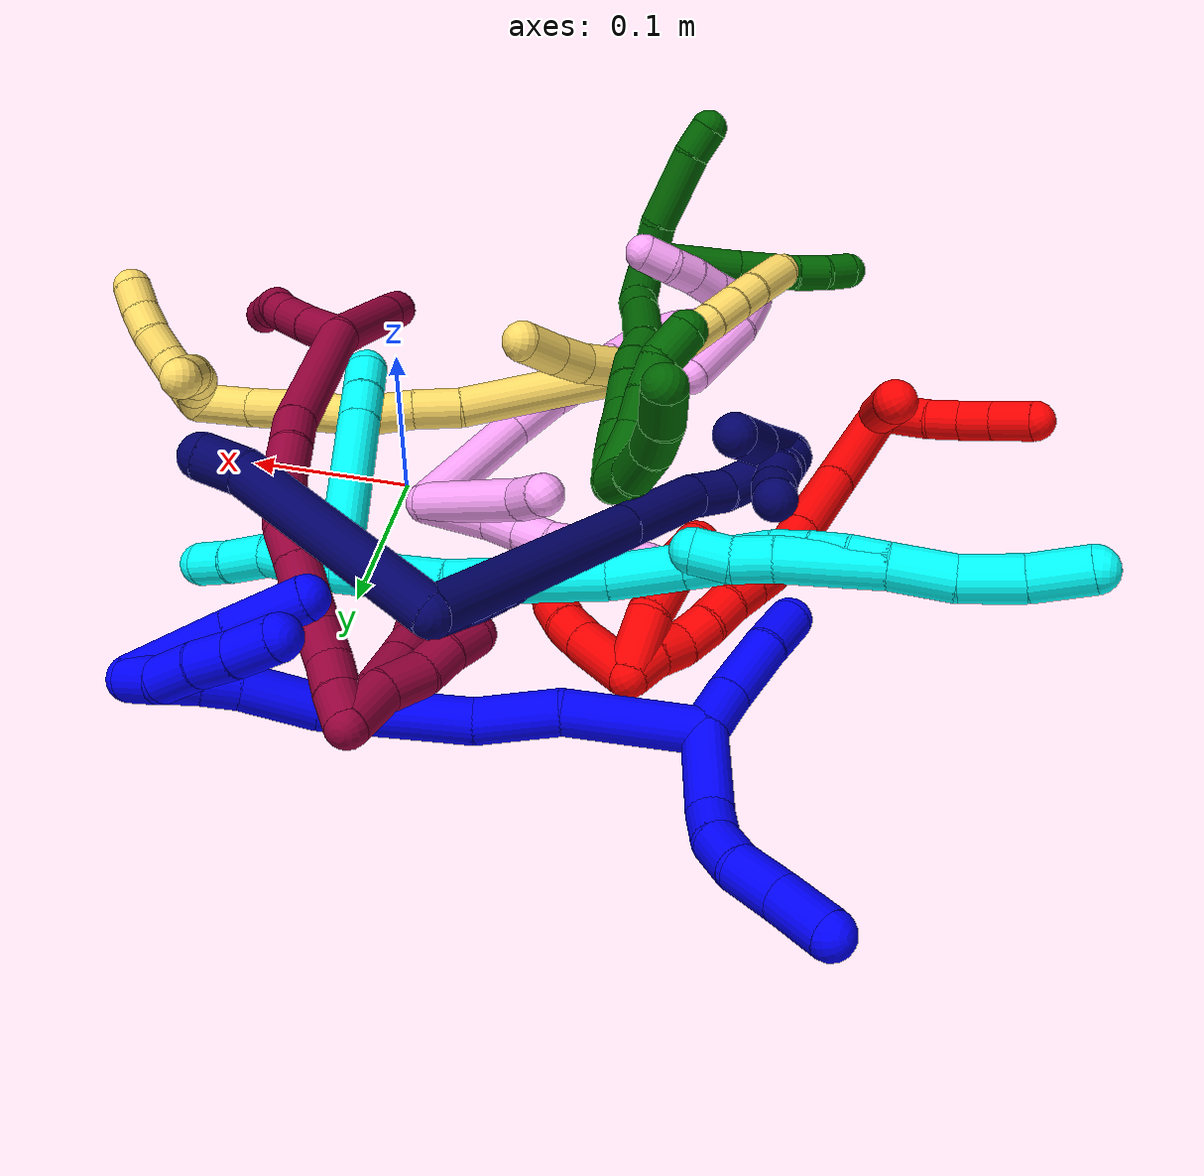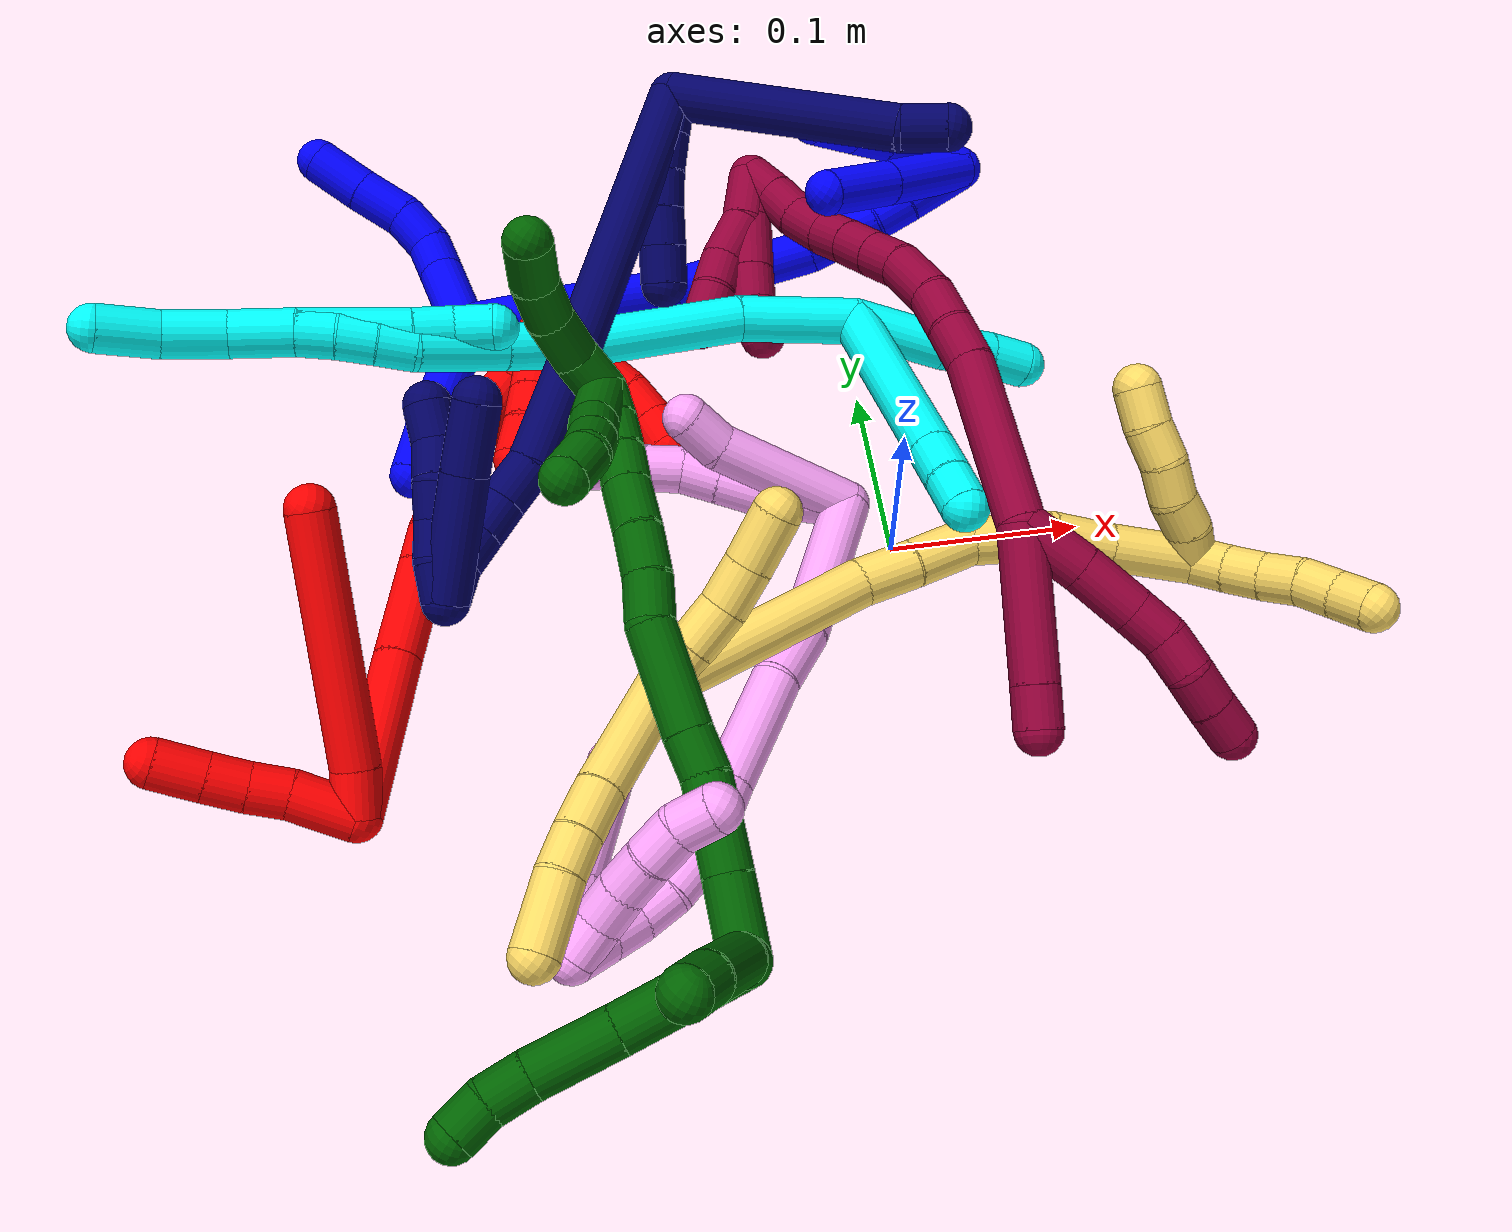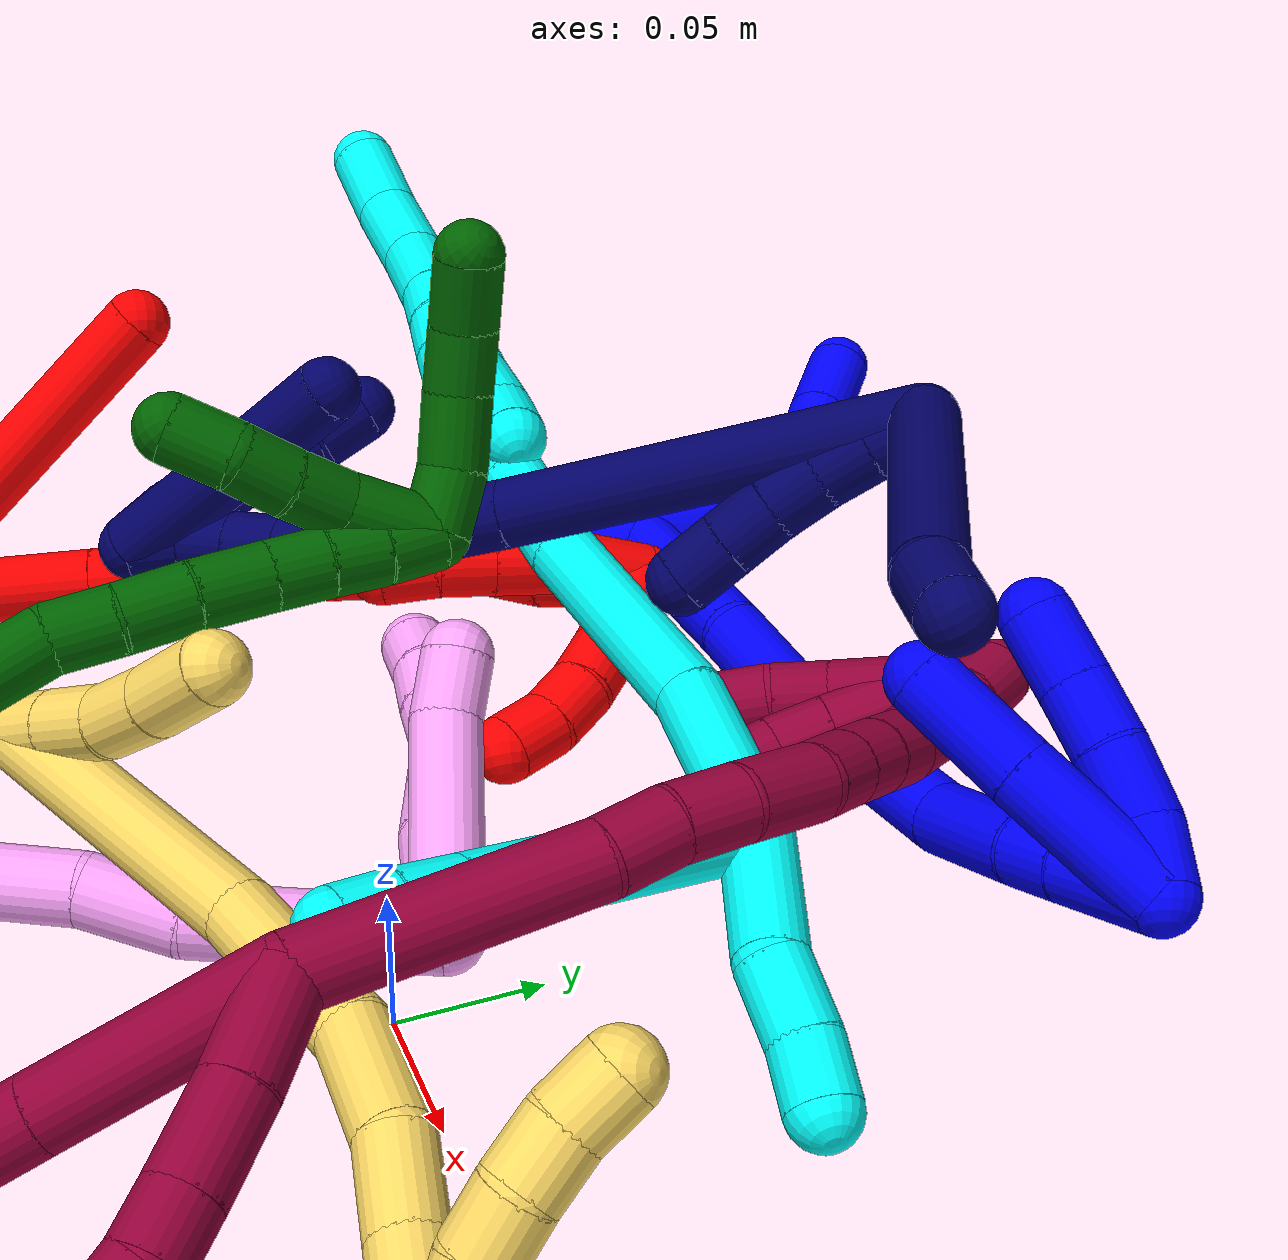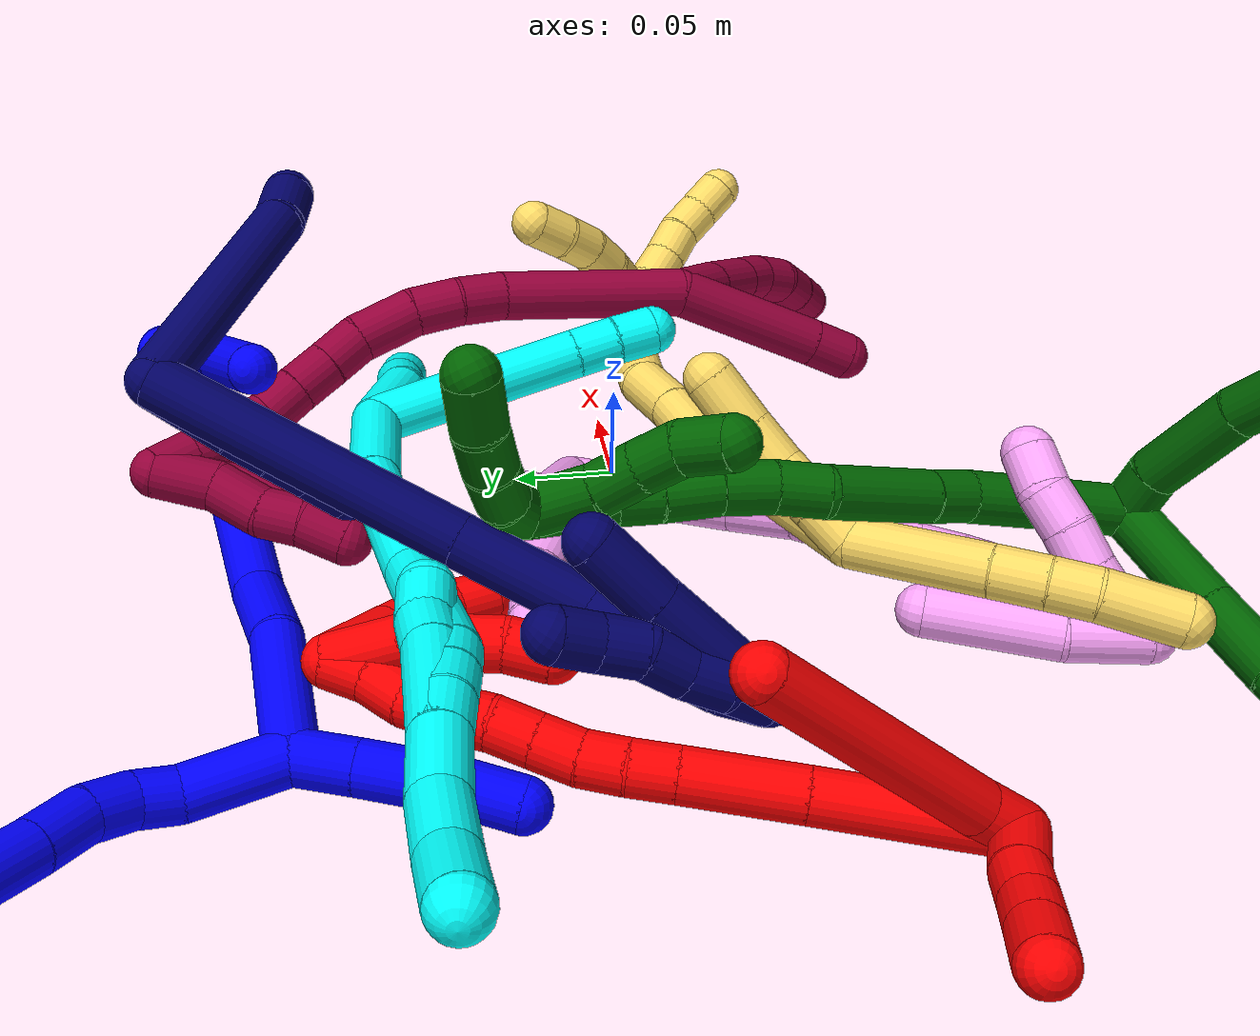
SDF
<sdf version="1.7">
 <world name="default">
  <plugin name="TubeGeneratorPlugin" filename="libtube_generator_plugin.so"/>
  <model name="photoneo_s_sensor">
   <static>1</static>
   <pose>0 0 2 1.57079 1.57079 3.14159</pose>
   <link name="link">
    <inertial><mass>0.1</mass></inertial>
    <sensor name="sensor" type="depth">
     <update_rate>30</update_rate>
     <camera>
      <horizontal_fov>1.22</horizontal_fov>
      <image><width>1920</width><height>1200</height><format>B8G8R8</format></image>
      <clip><near>0.1</near><far>4</far></clip>
      <depth_camera><output>points</output></depth_camera>
     </camera>
     <plugin name="camera_plugin" filename="libgazebo_ros_depth_camera.so">
      <baseline>0.2</baseline>
      <alwaysOn>1</alwaysOn>
      <updateRate>0.0</updateRate>
      <cameraName>camera_ir</cameraName>
      <imageTopicName>/camera/color/image_raw</imageTopicName>
      <cameraInfoTopicName>/camera/color/camera_info</cameraInfoTopicName>
      <depthImageTopicName>/camera/depth/image_raw</depthImageTopicName>
      <depthImageCameraInfoTopicName>/camera/depth/camera_info</depthImageCameraInfoTopicName>
      <pointCloudTopicName>/camera/depth/points</pointCloudTopicName>
      <frameName>fr_optical</frameName>
      <pointCloudCutoff>0.1</pointCloudCutoff>
      <pointCloudCutoffMax>2.0</pointCloudCutoffMax>
      <distortionK1>0</distortionK1>
      <distortionK2>0</distortionK2>
      <distortionK3>0</distortionK3>
      <distortionT1>0</distortionT1>
      <distortionT2>0</distortionT2>
      <CxPrime>0</CxPrime>
      <Cx>0</Cx>
      <Cy>0</Cy>
      <focalLength>0</focalLength>
      <hackBaseline>0</hackBaseline>
     </plugin>
    </sensor>
   </link>
  </model>
  <gravity>0 0 -9.8</gravity>
  <magnetic_field>6e-06 2.3e-05 -4.2e-05</magnetic_field>
  <atmosphere type="adiabatic"/>
  <physics name="default_physics" default="0" type="ode">
   <max_step_size>0.003</max_step_size>
   <real_time_factor>1</real_time_factor>
   <real_time_update_rate>1000</real_time_update_rate>
   <max_contacts>10000</max_contacts>
   <ode>
    <solver>
     <type>quick</type>
     <iters>100</iters>
     <sor>1.3</sor>
     <use_dynamic_moi_rescaling>0</use_dynamic_moi_rescaling>
    </solver>
    <constraints>
     <contact_max_correcting_vel>0</contact_max_correcting_vel>
     <contact_surface_layer>0.001</contact_surface_layer>
     <cfm>0</cfm>
     <erp>0.2</erp>
    </constraints>
   </ode>
  </physics>
  <scene><ambient>0.4 0.4 0.4 1</ambient><background>0.7 0.7 0.7 1</background><shadows>0</shadows></scene>
  <audio><device>default</device></audio>
  <spherical_coordinates>
   <surface_model>EARTH_WGS84</surface_model>
   <latitude_deg>0</latitude_deg>
   <longitude_deg>0</longitude_deg>
   <elevation>0</elevation>
   <heading_deg>0</heading_deg>
  </spherical_coordinates>
  <model name="bin">
   <static>1</static>
   <link name="bottom">
    <collision name="collision-bottom">
     <pose>0 0 -0.01 0 -0 0</pose>
     <geometry><box><size>0.8 0.6 0.02</size></box></geometry>
     <surface>
      <friction><ode><mu>100</mu><mu2>100</mu2></ode></friction>
      <contact><collide_bitmask>65535</collide_bitmask></contact>
     </surface>
    </collision>
   </link>
   <link name="west_wall">
    <collision name="collision-west_wall">
     <pose>-0.41 0 0.1 0 -0 0</pose>
     <geometry><box><size>0.02 0.6 0.2</size></box></geometry>
     <surface>
      <friction><ode><mu>100</mu><mu2>100</mu2></ode></friction>
      <contact><collide_bitmask>65535</collide_bitmask></contact>
     </surface>
    </collision>
   </link>
   <link name="east_wall">
    <collision name="collision-east_wall">
     <pose>0.41 0 0.1 0 -0 0</pose>
     <geometry><box><size>0.02 0.6 0.2</size></box></geometry>
     <surface>
      <friction><ode><mu>100</mu><mu2>100</mu2></ode></friction>
      <contact><collide_bitmask>65535</collide_bitmask></contact>
     </surface>
    </collision>
   </link>
   <link name="south_wall">
    <collision name="collision-south_wall">
     <pose>0 -0.31 0.1 0 -0 0</pose>
     <geometry><box><size>0.8 0.02 0.2</size></box></geometry>
     <surface>
      <friction><ode><mu>100</mu><mu2>100</mu2></ode></friction>
      <contact><collide_bitmask>65535</collide_bitmask></contact>
     </surface>
    </collision>
   </link>
   <link name="north_wall">
    <collision name="collision-north_wall">
     <pose>0 0.31 0.1 0 -0 0</pose>
     <geometry><box><size>0.8 0.02 0.2</size></box></geometry>
     <surface>
      <friction><ode><mu>100</mu><mu2>100</mu2></ode></friction>
      <contact><collide_bitmask>65535</collide_bitmask></contact>
     </surface>
    </collision>
   </link>
  </model>
  <model name="1">
   <static>0</static>
   <link name="1">
    <collision name="collision-cylinder-e_1_2_8">
     <pose>0.011489 0.018493 0.009743 -1.08589 0.502562 -0.307371</pose>
     <geometry><cylinder><radius>0.0125</radius><length>0.047705</length></cylinder></geometry>
     <surface>
      <friction><ode><mu>1.16</mu><mu2>1.16</mu2><slip1>0</slip1><slip2>0</slip2></ode></friction>
      <contact><ode><kp>1e+06</kp><kd>1</kd><max_vel>0</max_vel><min_depth>0.001</min_depth></ode></contact>
     </surface>
    </collision>
    <visual name="visual-cylinder-e_1_2_8">
     <pose>0.011489 0.018493 0.009743 -1.08589 0.502562 -0.307371</pose>
     <geometry><cylinder><radius>0.0125</radius><length>0.047705</length></cylinder></geometry>
     <material><ambient>0 0 1 1</ambient></material>
    </visual>
    <collision name="collision-cylinder-e_2_8_9">
     <pose>0.028894 0.042202 0.025669 -0.700778 0.631579 -0.237689</pose>
     <geometry><cylinder><radius>0.0125</radius><length>0.020041</length></cylinder></geometry>
     <surface>
      <friction><ode><mu>1.16</mu><mu2>1.16</mu2><slip1>0</slip1><slip2>0</slip2></ode></friction>
      <contact><ode><kp>1e+06</kp><kd>1</kd><max_vel>0</max_vel><min_depth>0.001</min_depth></ode></contact>
     </surface>
    </collision>
    <visual name="visual-cylinder-e_2_8_9">
     <pose>0.028894 0.042202 0.025669 -0.700778 0.631579 -0.237689</pose>
     <geometry><cylinder><radius>0.0125</radius><length>0.020041</length></cylinder></geometry>
     <material><ambient>0 0 1 1</ambient></material>
    </visual>
    <collision name="collision-cylinder-e_3_9_10">
     <pose>0.038753 0.05204 0.041283 -0.455741 0.359004 -0.084108</pose>
     <geometry><cylinder><radius>0.0125</radius><length>0.022442</length></cylinder></geometry>
     <surface>
      <friction><ode><mu>1.16</mu><mu2>1.16</mu2><slip1>0</slip1><slip2>0</slip2></ode></friction>
      <contact><ode><kp>1e+06</kp><kd>1</kd><max_vel>0</max_vel><min_depth>0.001</min_depth></ode></contact>
     </surface>
    </collision>
    <visual name="visual-cylinder-e_3_9_10">
     <pose>0.038753 0.05204 0.041283 -0.455741 0.359004 -0.084108</pose>
     <geometry><cylinder><radius>0.0125</radius><length>0.022442</length></cylinder></geometry>
     <material><ambient>0 0 1 1</ambient></material>
    </visual>
    <collision name="collision-cylinder-e_4_10_11">
     <pose>0.043777 0.062206 0.063885 -0.39836 0.075541 -0.015255</pose>
     <geometry><cylinder><radius>0.0125</radius><length>0.028656</length></cylinder></geometry>
     <surface>
      <friction><ode><mu>1.16</mu><mu2>1.16</mu2><slip1>0</slip1><slip2>0</slip2></ode></friction>
      <contact><ode><kp>1e+06</kp><kd>1</kd><max_vel>0</max_vel><min_depth>0.001</min_depth></ode></contact>
     </surface>
    </collision>
    <visual name="visual-cylinder-e_4_10_11">
     <pose>0.043777 0.062206 0.063885 -0.39836 0.075541 -0.015255</pose>
     <geometry><cylinder><radius>0.0125</radius><length>0.028656</length></cylinder></geometry>
     <material><ambient>0 0 1 1</ambient></material>
    </visual>
    <collision name="collision-cylinder-e_5_11_6">
     <pose>0.046782 0.073852 0.091256 -0.405917 0.123851 -0.025519</pose>
     <geometry><cylinder><radius>0.0125</radius><length>0.031157</length></cylinder></geometry>
     <surface>
      <friction><ode><mu>1.16</mu><mu2>1.16</mu2><slip1>0</slip1><slip2>0</slip2></ode></friction>
      <contact><ode><kp>1e+06</kp><kd>1</kd><max_vel>0</max_vel><min_depth>0.001</min_depth></ode></contact>
     </surface>
    </collision>
    <visual name="visual-cylinder-e_5_11_6">
     <pose>0.046782 0.073852 0.091256 -0.405917 0.123851 -0.025519</pose>
     <geometry><cylinder><radius>0.0125</radius><length>0.031157</length></cylinder></geometry>
     <material><ambient>0 0 1 1</ambient></material>
    </visual>
    <collision name="collision-cylinder-e_1_2_12">
     <pose>-0.012082 -0.00769 -0.001104 1.71337 -0.99935 -1.12414</pose>
     <geometry><cylinder><radius>0.0125</radius><length>0.028729</length></cylinder></geometry>
     <surface>
      <friction><ode><mu>1.16</mu><mu2>1.16</mu2><slip1>0</slip1><slip2>0</slip2></ode></friction>
      <contact><ode><kp>1e+06</kp><kd>1</kd><max_vel>0</max_vel><min_depth>0.001</min_depth></ode></contact>
     </surface>
    </collision>
    <visual name="visual-cylinder-e_1_2_12">
     <pose>-0.012082 -0.00769 -0.001104 1.71337 -0.99935 -1.12414</pose>
     <geometry><cylinder><radius>0.0125</radius><length>0.028729</length></cylinder></geometry>
     <material><ambient>0 0 1 1</ambient></material>
    </visual>
    <collision name="collision-cylinder-e_2_12_13">
     <pose>-0.041639 -0.026576 -0.002082 1.55955 -1.00097 -0.991533</pose>
     <geometry><cylinder><radius>0.0125</radius><length>0.041508</length></cylinder></geometry>
     <surface>
      <friction><ode><mu>1.16</mu><mu2>1.16</mu2><slip1>0</slip1><slip2>0</slip2></ode></friction>
      <contact><ode><kp>1e+06</kp><kd>1</kd><max_vel>0</max_vel><min_depth>0.001</min_depth></ode></contact>
     </surface>
    </collision>
    <visual name="visual-cylinder-e_2_12_13">
     <pose>-0.041639 -0.026576 -0.002082 1.55955 -1.00097 -0.991533</pose>
     <geometry><cylinder><radius>0.0125</radius><length>0.041508</length></cylinder></geometry>
     <material><ambient>0 0 1 1</ambient></material>
    </visual>
    <collision name="collision-cylinder-e_3_13_5">
     <pose>-0.072499 -0.044168 -0.003131 1.75241 -1.11854 -1.28872</pose>
     <geometry><cylinder><radius>0.0125</radius><length>0.029763</length></cylinder></geometry>
     <surface>
      <friction><ode><mu>1.16</mu><mu2>1.16</mu2><slip1>0</slip1><slip2>0</slip2></ode></friction>
      <contact><ode><kp>1e+06</kp><kd>1</kd><max_vel>0</max_vel><min_depth>0.001</min_depth></ode></contact>
     </surface>
    </collision>
    <visual name="visual-cylinder-e_3_13_5">
     <pose>-0.072499 -0.044168 -0.003131 1.75241 -1.11854 -1.28872</pose>
     <geometry><cylinder><radius>0.0125</radius><length>0.029763</length></cylinder></geometry>
     <material><ambient>0 0 1 1</ambient></material>
    </visual>
    <collision name="collision-cylinder-e_1_2_14">
     <pose>0.023293 -0.006802 -0.028027 2.90351 0.679373 2.48888</pose>
     <geometry><cylinder><radius>0.0125</radius><length>0.074144</length></cylinder></geometry>
     <surface>
      <friction><ode><mu>1.16</mu><mu2>1.16</mu2><slip1>0</slip1><slip2>0</slip2></ode></friction>
      <contact><ode><kp>1e+06</kp><kd>1</kd><max_vel>0</max_vel><min_depth>0.001</min_depth></ode></contact>
     </surface>
    </collision>
    <visual name="visual-cylinder-e_1_2_14">
     <pose>0.023293 -0.006802 -0.028027 2.90351 0.679373 2.48888</pose>
     <geometry><cylinder><radius>0.0125</radius><length>0.074144</length></cylinder></geometry>
     <material><ambient>0 0 1 1</ambient></material>
    </visual>
    <collision name="collision-cylinder-e_2_14_15">
     <pose>0.060418 -0.012271 -0.074772 -3.07054 0.63523 -2.92621</pose>
     <geometry><cylinder><radius>0.0125</radius><length>0.046624</length></cylinder></geometry>
     <surface>
      <friction><ode><mu>1.16</mu><mu2>1.16</mu2><slip1>0</slip1><slip2>0</slip2></ode></friction>
      <contact><ode><kp>1e+06</kp><kd>1</kd><max_vel>0</max_vel><min_depth>0.001</min_depth></ode></contact>
     </surface>
    </collision>
    <visual name="visual-cylinder-e_2_14_15">
     <pose>0.060418 -0.012271 -0.074772 -3.07054 0.63523 -2.92621</pose>
     <geometry><cylinder><radius>0.0125</radius><length>0.046624</length></cylinder></geometry>
     <material><ambient>0 0 1 1</ambient></material>
    </visual>
    <collision name="collision-cylinder-e_3_15_16">
     <pose>0.102815 -0.017243 -0.121868 2.92301 0.776624 2.61747</pose>
     <geometry><cylinder><radius>0.0125</radius><length>0.081511</length></cylinder></geometry>
     <surface>
      <friction><ode><mu>1.16</mu><mu2>1.16</mu2><slip1>0</slip1><slip2>0</slip2></ode></friction>
      <contact><ode><kp>1e+06</kp><kd>1</kd><max_vel>0</max_vel><min_depth>0.001</min_depth></ode></contact>
     </surface>
    </collision>
    <visual name="visual-cylinder-e_3_15_16">
     <pose>0.102815 -0.017243 -0.121868 2.92301 0.776624 2.61747</pose>
     <geometry><cylinder><radius>0.0125</radius><length>0.081511</length></cylinder></geometry>
     <material><ambient>0 0 1 1</ambient></material>
    </visual>
    <collision name="collision-cylinder-e_4_16_17">
     <pose>0.147984 -0.03052 -0.161184 2.57401 0.907647 2.06379</pose>
     <geometry><cylinder><radius>0.0125</radius><length>0.042141</length></cylinder></geometry>
     <surface>
      <friction><ode><mu>1.16</mu><mu2>1.16</mu2><slip1>0</slip1><slip2>0</slip2></ode></friction>
      <contact><ode><kp>1e+06</kp><kd>1</kd><max_vel>0</max_vel><min_depth>0.001</min_depth></ode></contact>
     </surface>
    </collision>
    <visual name="visual-cylinder-e_4_16_17">
     <pose>0.147984 -0.03052 -0.161184 2.57401 0.907647 2.06379</pose>
     <geometry><cylinder><radius>0.0125</radius><length>0.042141</length></cylinder></geometry>
     <material><ambient>0 0 1 1</ambient></material>
    </visual>
    <collision name="collision-cylinder-e_5_17_18">
     <pose>0.173132 -0.039573 -0.177175 2.75115 1.00165 2.44827</pose>
     <geometry><cylinder><radius>0.0125</radius><length>0.020285</length></cylinder></geometry>
     <surface>
      <friction><ode><mu>1.16</mu><mu2>1.16</mu2><slip1>0</slip1><slip2>0</slip2></ode></friction>
      <contact><ode><kp>1e+06</kp><kd>1</kd><max_vel>0</max_vel><min_depth>0.001</min_depth></ode></contact>
     </surface>
    </collision>
    <visual name="visual-cylinder-e_5_17_18">
     <pose>0.173132 -0.039573 -0.177175 2.75115 1.00165 2.44827</pose>
     <geometry><cylinder><radius>0.0125</radius><length>0.020285</length></cylinder></geometry>
     <material><ambient>0 0 1 1</ambient></material>
    </visual>
    <collision name="collision-cylinder-e_6_18_1">
     <pose>0.196867 -0.043983 -0.190904 2.8792 1.03686 2.68697</pose>
     <geometry><cylinder><radius>0.0125</radius><length>0.035295</length></cylinder></geometry>
     <surface>
      <friction><ode><mu>1.16</mu><mu2>1.16</mu2><slip1>0</slip1><slip2>0</slip2></ode></friction>
      <contact><ode><kp>1e+06</kp><kd>1</kd><max_vel>0</max_vel><min_depth>0.001</min_depth></ode></contact>
     </surface>
    </collision>
    <visual name="visual-cylinder-e_6_18_1">
     <pose>0.196867 -0.043983 -0.190904 2.8792 1.03686 2.68697</pose>
     <geometry><cylinder><radius>0.0125</radius><length>0.035295</length></cylinder></geometry>
     <material><ambient>0 0 1 1</ambient></material>
    </visual>
    <collision name="collision-cylinder-e_1_1_19">
     <pose>0.195289 -0.056532 -0.179126 0.46338 -0.632842 -0.154189</pose>
     <geometry><cylinder><radius>0.0125</radius><length>0.056706</length></cylinder></geometry>
     <surface>
      <friction><ode><mu>1.16</mu><mu2>1.16</mu2><slip1>0</slip1><slip2>0</slip2></ode></friction>
      <contact><ode><kp>1e+06</kp><kd>1</kd><max_vel>0</max_vel><min_depth>0.001</min_depth></ode></contact>
     </surface>
    </collision>
    <visual name="visual-cylinder-e_1_1_19">
     <pose>0.195289 -0.056532 -0.179126 0.46338 -0.632842 -0.154189</pose>
     <geometry><cylinder><radius>0.0125</radius><length>0.056706</length></cylinder></geometry>
     <material><ambient>0 0 1 1</ambient></material>
    </visual>
    <collision name="collision-cylinder-e_2_19_4">
     <pose>0.165985 -0.074137 -0.142646 0.431806 -0.617599 -0.139702</pose>
     <geometry><cylinder><radius>0.0125</radius><length>0.043294</length></cylinder></geometry>
     <surface>
      <friction><ode><mu>1.16</mu><mu2>1.16</mu2><slip1>0</slip1><slip2>0</slip2></ode></friction>
      <contact><ode><kp>1e+06</kp><kd>1</kd><max_vel>0</max_vel><min_depth>0.001</min_depth></ode></contact>
     </surface>
    </collision>
    <visual name="visual-cylinder-e_2_19_4">
     <pose>0.165985 -0.074137 -0.142646 0.431806 -0.617599 -0.139702</pose>
     <geometry><cylinder><radius>0.0125</radius><length>0.043294</length></cylinder></geometry>
     <material><ambient>0 0 1 1</ambient></material>
    </visual>
    <collision name="collision-cylinder-e_1_1_20">
     <pose>0.210608 -0.0459 -0.18768 -0.034686 -0.12123 0.002105</pose>
     <geometry><cylinder><radius>0.0125</radius><length>0.023985</length></cylinder></geometry>
     <surface>
      <friction><ode><mu>1.16</mu><mu2>1.16</mu2><slip1>0</slip1><slip2>0</slip2></ode></friction>
      <contact><ode><kp>1e+06</kp><kd>1</kd><max_vel>0</max_vel><min_depth>0.001</min_depth></ode></contact>
     </surface>
    </collision>
    <visual name="visual-cylinder-e_1_1_20">
     <pose>0.210608 -0.0459 -0.18768 -0.034686 -0.12123 0.002105</pose>
     <geometry><cylinder><radius>0.0125</radius><length>0.023985</length></cylinder></geometry>
     <material><ambient>0 0 1 1</ambient></material>
    </visual>
    <collision name="collision-cylinder-e_2_20_21">
     <pose>0.205982 -0.049098 -0.163543 0.286898 -0.243869 -0.035397</pose>
     <geometry><cylinder><radius>0.0125</radius><length>0.026301</length></cylinder></geometry>
     <surface>
      <friction><ode><mu>1.16</mu><mu2>1.16</mu2><slip1>0</slip1><slip2>0</slip2></ode></friction>
      <contact><ode><kp>1e+06</kp><kd>1</kd><max_vel>0</max_vel><min_depth>0.001</min_depth></ode></contact>
     </surface>
    </collision>
    <visual name="visual-cylinder-e_2_20_21">
     <pose>0.205982 -0.049098 -0.163543 0.286898 -0.243869 -0.035397</pose>
     <geometry><cylinder><radius>0.0125</radius><length>0.026301</length></cylinder></geometry>
     <material><ambient>0 0 1 1</ambient></material>
    </visual>
    <collision name="collision-cylinder-e_3_21_22">
     <pose>0.198945 -0.055 -0.14056 0.210056 -0.338104 -0.035981</pose>
     <geometry><cylinder><radius>0.0125</radius><length>0.023288</length></cylinder></geometry>
     <surface>
      <friction><ode><mu>1.16</mu><mu2>1.16</mu2><slip1>0</slip1><slip2>0</slip2></ode></friction>
      <contact><ode><kp>1e+06</kp><kd>1</kd><max_vel>0</max_vel><min_depth>0.001</min_depth></ode></contact>
     </surface>
    </collision>
    <visual name="visual-cylinder-e_3_21_22">
     <pose>0.198945 -0.055 -0.14056 0.210056 -0.338104 -0.035981</pose>
     <geometry><cylinder><radius>0.0125</radius><length>0.023288</length></cylinder></geometry>
     <material><ambient>0 0 1 1</ambient></material>
    </visual>
    <collision name="collision-cylinder-e_4_22_3">
     <pose>0.190751 -0.060871 -0.117858 0.290886 -0.33399 -0.049372</pose>
     <geometry><cylinder><radius>0.0125</radius><length>0.026426</length></cylinder></geometry>
     <surface>
      <friction><ode><mu>1.16</mu><mu2>1.16</mu2><slip1>0</slip1><slip2>0</slip2></ode></friction>
      <contact><ode><kp>1e+06</kp><kd>1</kd><max_vel>0</max_vel><min_depth>0.001</min_depth></ode></contact>
     </surface>
    </collision>
    <visual name="visual-cylinder-e_4_22_3">
     <pose>0.190751 -0.060871 -0.117858 0.290886 -0.33399 -0.049372</pose>
     <geometry><cylinder><radius>0.0125</radius><length>0.026426</length></cylinder></geometry>
     <material><ambient>0 0 1 1</ambient></material>
    </visual>
    <collision name="collision-sphere-3">
     <pose>0.186419 -0.064451 -0.1059 0 -0 0</pose>
     <geometry><sphere><radius>0.0125</radius></sphere></geometry>
     <surface>
      <friction><ode><mu>1.16</mu><mu2>1.16</mu2><slip1>0</slip1><slip2>0</slip2></ode></friction>
      <contact><ode><kp>1e+06</kp><kd>1</kd><max_vel>0</max_vel><min_depth>0.001</min_depth></ode></contact>
     </surface>
    </collision>
    <visual name="visual-sphere-3">
     <pose>0.186419 -0.064451 -0.1059 0 -0 0</pose>
     <geometry><sphere><radius>0.0125</radius></sphere></geometry>
     <material><ambient>0 0 1 1</ambient></material>
    </visual>
    <collision name="collision-sphere-22">
     <pose>0.195082 -0.057291 -0.129817 0 -0 0</pose>
     <geometry><sphere><radius>0.0125</radius></sphere></geometry>
     <surface>
      <friction><ode><mu>1.16</mu><mu2>1.16</mu2><slip1>0</slip1><slip2>0</slip2></ode></friction>
      <contact><ode><kp>1e+06</kp><kd>1</kd><max_vel>0</max_vel><min_depth>0.001</min_depth></ode></contact>
     </surface>
    </collision>
    <visual name="visual-sphere-22">
     <pose>0.195082 -0.057291 -0.129817 0 -0 0</pose>
     <geometry><sphere><radius>0.0125</radius></sphere></geometry>
     <material><ambient>0 0 1 1</ambient></material>
    </visual>
    <collision name="collision-sphere-21">
     <pose>0.202807 -0.05271 -0.151304 0 -0 0</pose>
     <geometry><sphere><radius>0.0125</radius></sphere></geometry>
     <surface>
      <friction><ode><mu>1.16</mu><mu2>1.16</mu2><slip1>0</slip1><slip2>0</slip2></ode></friction>
      <contact><ode><kp>1e+06</kp><kd>1</kd><max_vel>0</max_vel><min_depth>0.001</min_depth></ode></contact>
     </surface>
    </collision>
    <visual name="visual-sphere-21">
     <pose>0.202807 -0.05271 -0.151304 0 -0 0</pose>
     <geometry><sphere><radius>0.0125</radius></sphere></geometry>
     <material><ambient>0 0 1 1</ambient></material>
    </visual>
    <collision name="collision-sphere-20">
     <pose>0.209158 -0.045487 -0.175783 0 -0 0</pose>
     <geometry><sphere><radius>0.0125</radius></sphere></geometry>
     <surface>
      <friction><ode><mu>1.16</mu><mu2>1.16</mu2><slip1>0</slip1><slip2>0</slip2></ode></friction>
      <contact><ode><kp>1e+06</kp><kd>1</kd><max_vel>0</max_vel><min_depth>0.001</min_depth></ode></contact>
     </surface>
    </collision>
    <visual name="visual-sphere-20">
     <pose>0.209158 -0.045487 -0.175783 0 -0 0</pose>
     <geometry><sphere><radius>0.0125</radius></sphere></geometry>
     <material><ambient>0 0 1 1</ambient></material>
    </visual>
    <collision name="collision-sphere-4">
     <pose>0.153449 -0.081523 -0.126618 0 -0 0</pose>
     <geometry><sphere><radius>0.0125</radius></sphere></geometry>
     <surface>
      <friction><ode><mu>1.16</mu><mu2>1.16</mu2><slip1>0</slip1><slip2>0</slip2></ode></friction>
      <contact><ode><kp>1e+06</kp><kd>1</kd><max_vel>0</max_vel><min_depth>0.001</min_depth></ode></contact>
     </surface>
    </collision>
    <visual name="visual-sphere-4">
     <pose>0.153449 -0.081523 -0.126618 0 -0 0</pose>
     <geometry><sphere><radius>0.0125</radius></sphere></geometry>
     <material><ambient>0 0 1 1</ambient></material>
    </visual>
    <collision name="collision-sphere-6">
     <pose>0.048707 0.079956 0.105459 0 -0 0</pose>
     <geometry><sphere><radius>0.0125</radius></sphere></geometry>
     <surface>
      <friction><ode><mu>1.16</mu><mu2>1.16</mu2><slip1>0</slip1><slip2>0</slip2></ode></friction>
      <contact><ode><kp>1e+06</kp><kd>1</kd><max_vel>0</max_vel><min_depth>0.001</min_depth></ode></contact>
     </surface>
    </collision>
    <visual name="visual-sphere-6">
     <pose>0.048707 0.079956 0.105459 0 -0 0</pose>
     <geometry><sphere><radius>0.0125</radius></sphere></geometry>
     <material><ambient>0 0 1 1</ambient></material>
    </visual>
    <collision name="collision-sphere-11">
     <pose>0.044858 0.067748 0.077054 0 -0 0</pose>
     <geometry><sphere><radius>0.0125</radius></sphere></geometry>
     <surface>
      <friction><ode><mu>1.16</mu><mu2>1.16</mu2><slip1>0</slip1><slip2>0</slip2></ode></friction>
      <contact><ode><kp>1e+06</kp><kd>1</kd><max_vel>0</max_vel><min_depth>0.001</min_depth></ode></contact>
     </surface>
    </collision>
    <visual name="visual-sphere-11">
     <pose>0.044858 0.067748 0.077054 0 -0 0</pose>
     <geometry><sphere><radius>0.0125</radius></sphere></geometry>
     <material><ambient>0 0 1 1</ambient></material>
    </visual>
    <collision name="collision-sphere-10">
     <pose>0.042695 0.056664 0.050717 0 -0 0</pose>
     <geometry><sphere><radius>0.0125</radius></sphere></geometry>
     <surface>
      <friction><ode><mu>1.16</mu><mu2>1.16</mu2><slip1>0</slip1><slip2>0</slip2></ode></friction>
      <contact><ode><kp>1e+06</kp><kd>1</kd><max_vel>0</max_vel><min_depth>0.001</min_depth></ode></contact>
     </surface>
    </collision>
    <visual name="visual-sphere-10">
     <pose>0.042695 0.056664 0.050717 0 -0 0</pose>
     <geometry><sphere><radius>0.0125</radius></sphere></geometry>
     <material><ambient>0 0 1 1</ambient></material>
    </visual>
    <collision name="collision-sphere-9">
     <pose>0.034811 0.047416 0.03185 0 -0 0</pose>
     <geometry><sphere><radius>0.0125</radius></sphere></geometry>
     <surface>
      <friction><ode><mu>1.16</mu><mu2>1.16</mu2><slip1>0</slip1><slip2>0</slip2></ode></friction>
      <contact><ode><kp>1e+06</kp><kd>1</kd><max_vel>0</max_vel><min_depth>0.001</min_depth></ode></contact>
     </surface>
    </collision>
    <visual name="visual-sphere-9">
     <pose>0.034811 0.047416 0.03185 0 -0 0</pose>
     <geometry><sphere><radius>0.0125</radius></sphere></geometry>
     <material><ambient>0 0 1 1</ambient></material>
    </visual>
    <collision name="collision-sphere-2">
     <geometry><sphere><radius>0.0125</radius></sphere></geometry>
     <surface>
      <friction><ode><mu>1.16</mu><mu2>1.16</mu2><slip1>0</slip1><slip2>0</slip2></ode></friction>
      <contact><ode><kp>1e+06</kp><kd>1</kd><max_vel>0</max_vel><min_depth>0.001</min_depth></ode></contact>
     </surface>
    </collision>
    <visual name="visual-sphere-2">
     <geometry><sphere><radius>0.0125</radius></sphere></geometry>
     <material><ambient>0 0 1 1</ambient></material>
    </visual>
    <collision name="collision-sphere-19">
     <pose>0.17852 -0.066751 -0.158674 0 -0 0</pose>
     <geometry><sphere><radius>0.0125</radius></sphere></geometry>
     <surface>
      <friction><ode><mu>1.16</mu><mu2>1.16</mu2><slip1>0</slip1><slip2>0</slip2></ode></friction>
      <contact><ode><kp>1e+06</kp><kd>1</kd><max_vel>0</max_vel><min_depth>0.001</min_depth></ode></contact>
     </surface>
    </collision>
    <visual name="visual-sphere-19">
     <pose>0.17852 -0.066751 -0.158674 0 -0 0</pose>
     <geometry><sphere><radius>0.0125</radius></sphere></geometry>
     <material><ambient>0 0 1 1</ambient></material>
    </visual>
    <collision name="collision-sphere-8">
     <pose>0.022978 0.036987 0.019487 0 -0 0</pose>
     <geometry><sphere><radius>0.0125</radius></sphere></geometry>
     <surface>
      <friction><ode><mu>1.16</mu><mu2>1.16</mu2><slip1>0</slip1><slip2>0</slip2></ode></friction>
      <contact><ode><kp>1e+06</kp><kd>1</kd><max_vel>0</max_vel><min_depth>0.001</min_depth></ode></contact>
     </surface>
    </collision>
    <visual name="visual-sphere-8">
     <pose>0.022978 0.036987 0.019487 0 -0 0</pose>
     <geometry><sphere><radius>0.0125</radius></sphere></geometry>
     <material><ambient>0 0 1 1</ambient></material>
    </visual>
    <collision name="collision-sphere-12">
     <pose>-0.024164 -0.01538 -0.002208 0 -0 0</pose>
     <geometry><sphere><radius>0.0125</radius></sphere></geometry>
     <surface>
      <friction><ode><mu>1.16</mu><mu2>1.16</mu2><slip1>0</slip1><slip2>0</slip2></ode></friction>
      <contact><ode><kp>1e+06</kp><kd>1</kd><max_vel>0</max_vel><min_depth>0.001</min_depth></ode></contact>
     </surface>
    </collision>
    <visual name="visual-sphere-12">
     <pose>-0.024164 -0.01538 -0.002208 0 -0 0</pose>
     <geometry><sphere><radius>0.0125</radius></sphere></geometry>
     <material><ambient>0 0 1 1</ambient></material>
    </visual>
    <collision name="collision-sphere-13">
     <pose>-0.059114 -0.037772 -0.001956 0 -0 0</pose>
     <geometry><sphere><radius>0.0125</radius></sphere></geometry>
     <surface>
      <friction><ode><mu>1.16</mu><mu2>1.16</mu2><slip1>0</slip1><slip2>0</slip2></ode></friction>
      <contact><ode><kp>1e+06</kp><kd>1</kd><max_vel>0</max_vel><min_depth>0.001</min_depth></ode></contact>
     </surface>
    </collision>
    <visual name="visual-sphere-13">
     <pose>-0.059114 -0.037772 -0.001956 0 -0 0</pose>
     <geometry><sphere><radius>0.0125</radius></sphere></geometry>
     <material><ambient>0 0 1 1</ambient></material>
    </visual>
    <collision name="collision-sphere-5">
     <pose>-0.085885 -0.050564 -0.004305 0 -0 0</pose>
     <geometry><sphere><radius>0.0125</radius></sphere></geometry>
     <surface>
      <friction><ode><mu>1.16</mu><mu2>1.16</mu2><slip1>0</slip1><slip2>0</slip2></ode></friction>
      <contact><ode><kp>1e+06</kp><kd>1</kd><max_vel>0</max_vel><min_depth>0.001</min_depth></ode></contact>
     </surface>
    </collision>
    <visual name="visual-sphere-5">
     <pose>-0.085885 -0.050564 -0.004305 0 -0 0</pose>
     <geometry><sphere><radius>0.0125</radius></sphere></geometry>
     <material><ambient>0 0 1 1</ambient></material>
    </visual>
    <collision name="collision-sphere-14">
     <pose>0.046585 -0.013604 -0.056055 0 -0 0</pose>
     <geometry><sphere><radius>0.0125</radius></sphere></geometry>
     <surface>
      <friction><ode><mu>1.16</mu><mu2>1.16</mu2><slip1>0</slip1><slip2>0</slip2></ode></friction>
      <contact><ode><kp>1e+06</kp><kd>1</kd><max_vel>0</max_vel><min_depth>0.001</min_depth></ode></contact>
     </surface>
    </collision>
    <visual name="visual-sphere-14">
     <pose>0.046585 -0.013604 -0.056055 0 -0 0</pose>
     <geometry><sphere><radius>0.0125</radius></sphere></geometry>
     <material><ambient>0 0 1 1</ambient></material>
    </visual>
    <collision name="collision-sphere-15">
     <pose>0.07425 -0.010939 -0.09349 0 -0 0</pose>
     <geometry><sphere><radius>0.0125</radius></sphere></geometry>
     <surface>
      <friction><ode><mu>1.16</mu><mu2>1.16</mu2><slip1>0</slip1><slip2>0</slip2></ode></friction>
      <contact><ode><kp>1e+06</kp><kd>1</kd><max_vel>0</max_vel><min_depth>0.001</min_depth></ode></contact>
     </surface>
    </collision>
    <visual name="visual-sphere-15">
     <pose>0.07425 -0.010939 -0.09349 0 -0 0</pose>
     <geometry><sphere><radius>0.0125</radius></sphere></geometry>
     <material><ambient>0 0 1 1</ambient></material>
    </visual>
    <collision name="collision-sphere-16">
     <pose>0.131379 -0.023547 -0.150246 0 -0 0</pose>
     <geometry><sphere><radius>0.0125</radius></sphere></geometry>
     <surface>
      <friction><ode><mu>1.16</mu><mu2>1.16</mu2><slip1>0</slip1><slip2>0</slip2></ode></friction>
      <contact><ode><kp>1e+06</kp><kd>1</kd><max_vel>0</max_vel><min_depth>0.001</min_depth></ode></contact>
     </surface>
    </collision>
    <visual name="visual-sphere-16">
     <pose>0.131379 -0.023547 -0.150246 0 -0 0</pose>
     <geometry><sphere><radius>0.0125</radius></sphere></geometry>
     <material><ambient>0 0 1 1</ambient></material>
    </visual>
    <collision name="collision-sphere-17">
     <pose>0.164588 -0.037493 -0.172121 0 -0 0</pose>
     <geometry><sphere><radius>0.0125</radius></sphere></geometry>
     <surface>
      <friction><ode><mu>1.16</mu><mu2>1.16</mu2><slip1>0</slip1><slip2>0</slip2></ode></friction>
      <contact><ode><kp>1e+06</kp><kd>1</kd><max_vel>0</max_vel><min_depth>0.001</min_depth></ode></contact>
     </surface>
    </collision>
    <visual name="visual-sphere-17">
     <pose>0.164588 -0.037493 -0.172121 0 -0 0</pose>
     <geometry><sphere><radius>0.0125</radius></sphere></geometry>
     <material><ambient>0 0 1 1</ambient></material>
    </visual>
    <collision name="collision-sphere-18">
     <pose>0.181675 -0.041654 -0.18223 0 -0 0</pose>
     <geometry><sphere><radius>0.0125</radius></sphere></geometry>
     <surface>
      <friction><ode><mu>1.16</mu><mu2>1.16</mu2><slip1>0</slip1><slip2>0</slip2></ode></friction>
      <contact><ode><kp>1e+06</kp><kd>1</kd><max_vel>0</max_vel><min_depth>0.001</min_depth></ode></contact>
     </surface>
    </collision>
    <visual name="visual-sphere-18">
     <pose>0.181675 -0.041654 -0.18223 0 -0 0</pose>
     <geometry><sphere><radius>0.0125</radius></sphere></geometry>
     <material><ambient>0 0 1 1</ambient></material>
    </visual>
    <collision name="collision-sphere-1">
     <pose>0.212058 -0.046313 -0.199578 0 -0 0</pose>
     <geometry><sphere><radius>0.0125</radius></sphere></geometry>
     <surface>
      <friction><ode><mu>1.16</mu><mu2>1.16</mu2><slip1>0</slip1><slip2>0</slip2></ode></friction>
      <contact><ode><kp>1e+06</kp><kd>1</kd><max_vel>0</max_vel><min_depth>0.001</min_depth></ode></contact>
     </surface>
    </collision>
    <visual name="visual-sphere-1">
     <pose>0.212058 -0.046313 -0.199578 0 -0 0</pose>
     <geometry><sphere><radius>0.0125</radius></sphere></geometry>
     <material><ambient>0 0 1 1</ambient></material>
    </visual>
    <inertial>
     <pose>0.091333 -0.017973 -0.077037 0 -0 0</pose>
     <mass>0.75</mass>
     <inertia>
      <ixx>1.8e-05</ixx>
      <ixy>0</ixy>
      <ixz>0</ixz>
      <iyy>0.000177</iyy>
      <iyz>0</iyz>
      <izz>-2.5e-05</izz>
     </inertia>
    </inertial>
   </link>
   <pose>-0.210842 0.168921 0.017528 -0.950107 -0.480076 0.878272</pose>
  </model>
  <model name="2">
   <static>0</static>
   <link name="2">
    <collision name="collision-cylinder-e_1_2_8">
     <pose>0.007693 0.007724 0.004858 -1.0094 0.700484 -0.398253</pose>
     <geometry><cylinder><radius>0.0125</radius><length>0.023871</length></cylinder></geometry>
     <surface>
      <friction><ode><mu>1.16</mu><mu2>1.16</mu2><slip1>0</slip1><slip2>0</slip2></ode></friction>
      <contact><ode><kp>1e+06</kp><kd>1</kd><max_vel>0</max_vel><min_depth>0.001</min_depth></ode></contact>
     </surface>
    </collision>
    <visual name="visual-cylinder-e_1_2_8">
     <pose>0.007693 0.007724 0.004858 -1.0094 0.700484 -0.398253</pose>
     <geometry><cylinder><radius>0.0125</radius><length>0.023871</length></cylinder></geometry>
     <material><ambient>1 0 0 1</ambient></material>
    </visual>
    <collision name="collision-cylinder-e_2_8_6">
     <pose>0.054118 0.051794 0.043717 -0.818706 0.661317 -0.295682</pose>
     <geometry><cylinder><radius>0.0125</radius><length>0.126129</length></cylinder></geometry>
     <surface>
      <friction><ode><mu>1.16</mu><mu2>1.16</mu2><slip1>0</slip1><slip2>0</slip2></ode></friction>
      <contact><ode><kp>1e+06</kp><kd>1</kd><max_vel>0</max_vel><min_depth>0.001</min_depth></ode></contact>
     </surface>
    </collision>
    <visual name="visual-cylinder-e_2_8_6">
     <pose>0.054118 0.051794 0.043717 -0.818706 0.661317 -0.295682</pose>
     <geometry><cylinder><radius>0.0125</radius><length>0.126129</length></cylinder></geometry>
     <material><ambient>1 0 0 1</ambient></material>
    </visual>
    <collision name="collision-cylinder-e_1_2_9">
     <pose>-0.005471 0.005971 0.014707 -0.385656 -0.331909 0.065385</pose>
     <geometry><cylinder><radius>0.0125</radius><length>0.033579</length></cylinder></geometry>
     <surface>
      <friction><ode><mu>1.16</mu><mu2>1.16</mu2><slip1>0</slip1><slip2>0</slip2></ode></friction>
      <contact><ode><kp>1e+06</kp><kd>1</kd><max_vel>0</max_vel><min_depth>0.001</min_depth></ode></contact>
     </surface>
    </collision>
    <visual name="visual-cylinder-e_1_2_9">
     <pose>-0.005471 0.005971 0.014707 -0.385656 -0.331909 0.065385</pose>
     <geometry><cylinder><radius>0.0125</radius><length>0.033579</length></cylinder></geometry>
     <material><ambient>1 0 0 1</ambient></material>
    </visual>
    <collision name="collision-cylinder-e_2_9_10">
     <pose>-0.015013 0.013993 0.038461 -0.222955 -0.413541 0.046955</pose>
     <geometry><cylinder><radius>0.0125</radius><length>0.020261</length></cylinder></geometry>
     <surface>
      <friction><ode><mu>1.16</mu><mu2>1.16</mu2><slip1>0</slip1><slip2>0</slip2></ode></friction>
      <contact><ode><kp>1e+06</kp><kd>1</kd><max_vel>0</max_vel><min_depth>0.001</min_depth></ode></contact>
     </surface>
    </collision>
    <visual name="visual-cylinder-e_2_9_10">
     <pose>-0.015013 0.013993 0.038461 -0.222955 -0.413541 0.046955</pose>
     <geometry><cylinder><radius>0.0125</radius><length>0.020261</length></cylinder></geometry>
     <material><ambient>1 0 0 1</ambient></material>
    </visual>
    <collision name="collision-cylinder-e_3_10_11">
     <pose>-0.022436 0.018341 0.056859 -0.240844 -0.335056 0.040922</pose>
     <geometry><cylinder><radius>0.0125</radius><length>0.020391</length></cylinder></geometry>
     <surface>
      <friction><ode><mu>1.16</mu><mu2>1.16</mu2><slip1>0</slip1><slip2>0</slip2></ode></friction>
      <contact><ode><kp>1e+06</kp><kd>1</kd><max_vel>0</max_vel><min_depth>0.001</min_depth></ode></contact>
     </surface>
    </collision>
    <visual name="visual-cylinder-e_3_10_11">
     <pose>-0.022436 0.018341 0.056859 -0.240844 -0.335056 0.040922</pose>
     <geometry><cylinder><radius>0.0125</radius><length>0.020391</length></cylinder></geometry>
     <material><ambient>1 0 0 1</ambient></material>
    </visual>
    <collision name="collision-cylinder-e_4_11_5">
     <pose>-0.029737 0.023622 0.078105 -0.245803 -0.311465 0.038783</pose>
     <geometry><cylinder><radius>0.0125</radius><length>0.025769</length></cylinder></geometry>
     <surface>
      <friction><ode><mu>1.16</mu><mu2>1.16</mu2><slip1>0</slip1><slip2>0</slip2></ode></friction>
      <contact><ode><kp>1e+06</kp><kd>1</kd><max_vel>0</max_vel><min_depth>0.001</min_depth></ode></contact>
     </surface>
    </collision>
    <visual name="visual-cylinder-e_4_11_5">
     <pose>-0.029737 0.023622 0.078105 -0.245803 -0.311465 0.038783</pose>
     <geometry><cylinder><radius>0.0125</radius><length>0.025769</length></cylinder></geometry>
     <material><ambient>1 0 0 1</ambient></material>
    </visual>
    <collision name="collision-cylinder-e_1_2_12">
     <pose>0.019098 0.038007 -0.003406 -1.66016 0.464022 -0.505706</pose>
     <geometry><cylinder><radius>0.0125</radius><length>0.085343</length></cylinder></geometry>
     <surface>
      <friction><ode><mu>1.16</mu><mu2>1.16</mu2><slip1>0</slip1><slip2>0</slip2></ode></friction>
      <contact><ode><kp>1e+06</kp><kd>1</kd><max_vel>0</max_vel><min_depth>0.001</min_depth></ode></contact>
     </surface>
    </collision>
    <visual name="visual-cylinder-e_1_2_12">
     <pose>0.019098 0.038007 -0.003406 -1.66016 0.464022 -0.505706</pose>
     <geometry><cylinder><radius>0.0125</radius><length>0.085343</length></cylinder></geometry>
     <material><ambient>1 0 0 1</ambient></material>
    </visual>
    <collision name="collision-cylinder-e_2_12_13">
     <pose>0.04996 0.099763 -0.009443 -1.68114 0.457529 -0.508853</pose>
     <geometry><cylinder><radius>0.0125</radius><length>0.053267</length></cylinder></geometry>
     <surface>
      <friction><ode><mu>1.16</mu><mu2>1.16</mu2><slip1>0</slip1><slip2>0</slip2></ode></friction>
      <contact><ode><kp>1e+06</kp><kd>1</kd><max_vel>0</max_vel><min_depth>0.001</min_depth></ode></contact>
     </surface>
    </collision>
    <visual name="visual-cylinder-e_2_12_13">
     <pose>0.04996 0.099763 -0.009443 -1.68114 0.457529 -0.508853</pose>
     <geometry><cylinder><radius>0.0125</radius><length>0.053267</length></cylinder></geometry>
     <material><ambient>1 0 0 1</ambient></material>
    </visual>
    <collision name="collision-cylinder-e_3_13_14">
     <pose>0.066223 0.13283 -0.013132 -1.68392 0.447209 -0.498805</pose>
     <geometry><cylinder><radius>0.0125</radius><length>0.020803</length></cylinder></geometry>
     <surface>
      <friction><ode><mu>1.16</mu><mu2>1.16</mu2><slip1>0</slip1><slip2>0</slip2></ode></friction>
      <contact><ode><kp>1e+06</kp><kd>1</kd><max_vel>0</max_vel><min_depth>0.001</min_depth></ode></contact>
     </surface>
    </collision>
    <visual name="visual-cylinder-e_3_13_14">
     <pose>0.066223 0.13283 -0.013132 -1.68392 0.447209 -0.498805</pose>
     <geometry><cylinder><radius>0.0125</radius><length>0.020803</length></cylinder></geometry>
     <material><ambient>1 0 0 1</ambient></material>
    </visual>
    <collision name="collision-cylinder-e_4_14_15">
     <pose>0.075347 0.150799 -0.01627 -1.80665 0.479565 -0.601582</pose>
     <geometry><cylinder><radius>0.0125</radius><length>0.020055</length></cylinder></geometry>
     <surface>
      <friction><ode><mu>1.16</mu><mu2>1.16</mu2><slip1>0</slip1><slip2>0</slip2></ode></friction>
      <contact><ode><kp>1e+06</kp><kd>1</kd><max_vel>0</max_vel><min_depth>0.001</min_depth></ode></contact>
     </surface>
    </collision>
    <visual name="visual-cylinder-e_4_14_15">
     <pose>0.075347 0.150799 -0.01627 -1.80665 0.479565 -0.601582</pose>
     <geometry><cylinder><radius>0.0125</radius><length>0.020055</length></cylinder></geometry>
     <material><ambient>1 0 0 1</ambient></material>
    </visual>
    <collision name="collision-cylinder-e_5_15_16">
     <pose>0.086164 0.167279 -0.020162 -1.79841 0.656292 -0.809366</pose>
     <geometry><cylinder><radius>0.0125</radius><length>0.02029</length></cylinder></geometry>
     <surface>
      <friction><ode><mu>1.16</mu><mu2>1.16</mu2><slip1>0</slip1><slip2>0</slip2></ode></friction>
      <contact><ode><kp>1e+06</kp><kd>1</kd><max_vel>0</max_vel><min_depth>0.001</min_depth></ode></contact>
     </surface>
    </collision>
    <visual name="visual-cylinder-e_5_15_16">
     <pose>0.086164 0.167279 -0.020162 -1.79841 0.656292 -0.809366</pose>
     <geometry><cylinder><radius>0.0125</radius><length>0.02029</length></cylinder></geometry>
     <material><ambient>1 0 0 1</ambient></material>
    </visual>
    <collision name="collision-cylinder-e_6_16_17">
     <pose>0.098599 0.182812 -0.023355 -1.74797 0.673504 -0.792427</pose>
     <geometry><cylinder><radius>0.0125</radius><length>0.020024</length></cylinder></geometry>
     <surface>
      <friction><ode><mu>1.16</mu><mu2>1.16</mu2><slip1>0</slip1><slip2>0</slip2></ode></friction>
      <contact><ode><kp>1e+06</kp><kd>1</kd><max_vel>0</max_vel><min_depth>0.001</min_depth></ode></contact>
     </surface>
    </collision>
    <visual name="visual-cylinder-e_6_16_17">
     <pose>0.098599 0.182812 -0.023355 -1.74797 0.673504 -0.792427</pose>
     <geometry><cylinder><radius>0.0125</radius><length>0.020024</length></cylinder></geometry>
     <material><ambient>1 0 0 1</ambient></material>
    </visual>
    <collision name="collision-cylinder-e_7_17_18">
     <pose>0.109865 0.198947 -0.027134 -1.84803 0.520165 -0.677619</pose>
     <geometry><cylinder><radius>0.0125</radius><length>0.020204</length></cylinder></geometry>
     <surface>
      <friction><ode><mu>1.16</mu><mu2>1.16</mu2><slip1>0</slip1><slip2>0</slip2></ode></friction>
      <contact><ode><kp>1e+06</kp><kd>1</kd><max_vel>0</max_vel><min_depth>0.001</min_depth></ode></contact>
     </surface>
    </collision>
    <visual name="visual-cylinder-e_7_17_18">
     <pose>0.109865 0.198947 -0.027134 -1.84803 0.520165 -0.677619</pose>
     <geometry><cylinder><radius>0.0125</radius><length>0.020204</length></cylinder></geometry>
     <material><ambient>1 0 0 1</ambient></material>
    </visual>
    <collision name="collision-cylinder-e_8_18_19">
     <pose>0.12006 0.214921 -0.033594 -2.06472 0.54333 -0.872725</pose>
     <geometry><cylinder><radius>0.0125</radius><length>0.020014</length></cylinder></geometry>
     <surface>
      <friction><ode><mu>1.16</mu><mu2>1.16</mu2><slip1>0</slip1><slip2>0</slip2></ode></friction>
      <contact><ode><kp>1e+06</kp><kd>1</kd><max_vel>0</max_vel><min_depth>0.001</min_depth></ode></contact>
     </surface>
    </collision>
    <visual name="visual-cylinder-e_8_18_19">
     <pose>0.12006 0.214921 -0.033594 -2.06472 0.54333 -0.872725</pose>
     <geometry><cylinder><radius>0.0125</radius><length>0.020014</length></cylinder></geometry>
     <material><ambient>1 0 0 1</ambient></material>
    </visual>
    <collision name="collision-cylinder-e_9_19_20">
     <pose>0.132575 0.228716 -0.040301 -1.97107 0.82439 -1.16643</pose>
     <geometry><cylinder><radius>0.0125</radius><length>0.02</length></cylinder></geometry>
     <surface>
      <friction><ode><mu>1.16</mu><mu2>1.16</mu2><slip1>0</slip1><slip2>0</slip2></ode></friction>
      <contact><ode><kp>1e+06</kp><kd>1</kd><max_vel>0</max_vel><min_depth>0.001</min_depth></ode></contact>
     </surface>
    </collision>
    <visual name="visual-cylinder-e_9_19_20">
     <pose>0.132575 0.228716 -0.040301 -1.97107 0.82439 -1.16643</pose>
     <geometry><cylinder><radius>0.0125</radius><length>0.02</length></cylinder></geometry>
     <material><ambient>1 0 0 1</ambient></material>
    </visual>
    <collision name="collision-cylinder-e_10_20_1">
     <pose>0.145682 0.242725 -0.045516 -1.89069 0.614566 -0.828039</pose>
     <geometry><cylinder><radius>0.0125</radius><length>0.02</length></cylinder></geometry>
     <surface>
      <friction><ode><mu>1.16</mu><mu2>1.16</mu2><slip1>0</slip1><slip2>0</slip2></ode></friction>
      <contact><ode><kp>1e+06</kp><kd>1</kd><max_vel>0</max_vel><min_depth>0.001</min_depth></ode></contact>
     </surface>
    </collision>
    <visual name="visual-cylinder-e_10_20_1">
     <pose>0.145682 0.242725 -0.045516 -1.89069 0.614566 -0.828039</pose>
     <geometry><cylinder><radius>0.0125</radius><length>0.02</length></cylinder></geometry>
     <material><ambient>1 0 0 1</ambient></material>
    </visual>
    <collision name="collision-cylinder-e_1_1_21">
     <pose>0.154529 0.237549 -0.062939 2.42525 0.15515 0.409505</pose>
     <geometry><cylinder><radius>0.0125</radius><length>0.039868</length></cylinder></geometry>
     <surface>
      <friction><ode><mu>1.16</mu><mu2>1.16</mu2><slip1>0</slip1><slip2>0</slip2></ode></friction>
      <contact><ode><kp>1e+06</kp><kd>1</kd><max_vel>0</max_vel><min_depth>0.001</min_depth></ode></contact>
     </surface>
    </collision>
    <visual name="visual-cylinder-e_1_1_21">
     <pose>0.154529 0.237549 -0.062939 2.42525 0.15515 0.409505</pose>
     <geometry><cylinder><radius>0.0125</radius><length>0.039868</length></cylinder></geometry>
     <material><ambient>1 0 0 1</ambient></material>
    </visual>
    <collision name="collision-cylinder-e_2_21_22">
     <pose>0.159234 0.217564 -0.084718 2.34706 0.162894 0.384295</pose>
     <geometry><cylinder><radius>0.0125</radius><length>0.020034</length></cylinder></geometry>
     <surface>
      <friction><ode><mu>1.16</mu><mu2>1.16</mu2><slip1>0</slip1><slip2>0</slip2></ode></friction>
      <contact><ode><kp>1e+06</kp><kd>1</kd><max_vel>0</max_vel><min_depth>0.001</min_depth></ode></contact>
     </surface>
    </collision>
    <visual name="visual-cylinder-e_2_21_22">
     <pose>0.159234 0.217564 -0.084718 2.34706 0.162894 0.384295</pose>
     <geometry><cylinder><radius>0.0125</radius><length>0.020034</length></cylinder></geometry>
     <material><ambient>1 0 0 1</ambient></material>
    </visual>
    <collision name="collision-cylinder-e_3_22_23">
     <pose>0.160989 0.202486 -0.097655 2.21376 0.013059 0.026099</pose>
     <geometry><cylinder><radius>0.0125</radius><length>0.020056</length></cylinder></geometry>
     <surface>
      <friction><ode><mu>1.16</mu><mu2>1.16</mu2><slip1>0</slip1><slip2>0</slip2></ode></friction>
      <contact><ode><kp>1e+06</kp><kd>1</kd><max_vel>0</max_vel><min_depth>0.001</min_depth></ode></contact>
     </surface>
    </collision>
    <visual name="visual-cylinder-e_3_22_23">
     <pose>0.160989 0.202486 -0.097655 2.21376 0.013059 0.026099</pose>
     <geometry><cylinder><radius>0.0125</radius><length>0.020056</length></cylinder></geometry>
     <material><ambient>1 0 0 1</ambient></material>
    </visual>
    <collision name="collision-cylinder-e_4_23_4">
     <pose>0.161057 0.185274 -0.107668 1.98149 -0.00628 -0.009584</pose>
     <geometry><cylinder><radius>0.0125</radius><length>0.020042</length></cylinder></geometry>
     <surface>
      <friction><ode><mu>1.16</mu><mu2>1.16</mu2><slip1>0</slip1><slip2>0</slip2></ode></friction>
      <contact><ode><kp>1e+06</kp><kd>1</kd><max_vel>0</max_vel><min_depth>0.001</min_depth></ode></contact>
     </surface>
    </collision>
    <visual name="visual-cylinder-e_4_23_4">
     <pose>0.161057 0.185274 -0.107668 1.98149 -0.00628 -0.009584</pose>
     <geometry><cylinder><radius>0.0125</radius><length>0.020042</length></cylinder></geometry>
     <material><ambient>1 0 0 1</ambient></material>
    </visual>
    <collision name="collision-cylinder-e_1_1_24">
     <pose>0.150338 0.233009 -0.043852 1.3331 -0.061673 -0.048521</pose>
     <geometry><cylinder><radius>0.0125</radius><length>0.036023</length></cylinder></geometry>
     <surface>
      <friction><ode><mu>1.16</mu><mu2>1.16</mu2><slip1>0</slip1><slip2>0</slip2></ode></friction>
      <contact><ode><kp>1e+06</kp><kd>1</kd><max_vel>0</max_vel><min_depth>0.001</min_depth></ode></contact>
     </surface>
    </collision>
    <visual name="visual-cylinder-e_1_1_24">
     <pose>0.150338 0.233009 -0.043852 1.3331 -0.061673 -0.048521</pose>
     <geometry><cylinder><radius>0.0125</radius><length>0.036023</length></cylinder></geometry>
     <material><ambient>1 0 0 1</ambient></material>
    </visual>
    <collision name="collision-cylinder-e_2_24_25">
     <pose>0.145457 0.204968 -0.038348 1.45111 -0.34044 -0.302573</pose>
     <geometry><cylinder><radius>0.0125</radius><length>0.022587</length></cylinder></geometry>
     <surface>
      <friction><ode><mu>1.16</mu><mu2>1.16</mu2><slip1>0</slip1><slip2>0</slip2></ode></friction>
      <contact><ode><kp>1e+06</kp><kd>1</kd><max_vel>0</max_vel><min_depth>0.001</min_depth></ode></contact>
     </surface>
    </collision>
    <visual name="visual-cylinder-e_2_24_25">
     <pose>0.145457 0.204968 -0.038348 1.45111 -0.34044 -0.302573</pose>
     <geometry><cylinder><radius>0.0125</radius><length>0.022587</length></cylinder></geometry>
     <material><ambient>1 0 0 1</ambient></material>
    </visual>
    <collision name="collision-cylinder-e_3_25_26">
     <pose>0.138267 0.18481 -0.035945 1.45331 -0.340314 -0.30312</pose>
     <geometry><cylinder><radius>0.0125</radius><length>0.020487</length></cylinder></geometry>
     <surface>
      <friction><ode><mu>1.16</mu><mu2>1.16</mu2><slip1>0</slip1><slip2>0</slip2></ode></friction>
      <contact><ode><kp>1e+06</kp><kd>1</kd><max_vel>0</max_vel><min_depth>0.001</min_depth></ode></contact>
     </surface>
    </collision>
    <visual name="visual-cylinder-e_3_25_26">
     <pose>0.138267 0.18481 -0.035945 1.45331 -0.340314 -0.30312</pose>
     <geometry><cylinder><radius>0.0125</radius><length>0.020487</length></cylinder></geometry>
     <material><ambient>1 0 0 1</ambient></material>
    </visual>
    <collision name="collision-cylinder-e_4_26_3">
     <pose>0.129449 0.16629 -0.03424 1.50676 -0.542829 -0.510623</pose>
     <geometry><cylinder><radius>0.0125</radius><length>0.020903</length></cylinder></geometry>
     <surface>
      <friction><ode><mu>1.16</mu><mu2>1.16</mu2><slip1>0</slip1><slip2>0</slip2></ode></friction>
      <contact><ode><kp>1e+06</kp><kd>1</kd><max_vel>0</max_vel><min_depth>0.001</min_depth></ode></contact>
     </surface>
    </collision>
    <visual name="visual-cylinder-e_4_26_3">
     <pose>0.129449 0.16629 -0.03424 1.50676 -0.542829 -0.510623</pose>
     <geometry><cylinder><radius>0.0125</radius><length>0.020903</length></cylinder></geometry>
     <material><ambient>1 0 0 1</ambient></material>
    </visual>
    <collision name="collision-sphere-3">
     <pose>0.12405 0.157359 -0.033668 0 -0 0</pose>
     <geometry><sphere><radius>0.0125</radius></sphere></geometry>
     <surface>
      <friction><ode><mu>1.16</mu><mu2>1.16</mu2><slip1>0</slip1><slip2>0</slip2></ode></friction>
      <contact><ode><kp>1e+06</kp><kd>1</kd><max_vel>0</max_vel><min_depth>0.001</min_depth></ode></contact>
     </surface>
    </collision>
    <visual name="visual-sphere-3">
     <pose>0.12405 0.157359 -0.033668 0 -0 0</pose>
     <geometry><sphere><radius>0.0125</radius></sphere></geometry>
     <material><ambient>1 0 0 1</ambient></material>
    </visual>
    <collision name="collision-sphere-26">
     <pose>0.134848 0.17522 -0.034813 0 -0 0</pose>
     <geometry><sphere><radius>0.0125</radius></sphere></geometry>
     <surface>
      <friction><ode><mu>1.16</mu><mu2>1.16</mu2><slip1>0</slip1><slip2>0</slip2></ode></friction>
      <contact><ode><kp>1e+06</kp><kd>1</kd><max_vel>0</max_vel><min_depth>0.001</min_depth></ode></contact>
     </surface>
    </collision>
    <visual name="visual-sphere-26">
     <pose>0.134848 0.17522 -0.034813 0 -0 0</pose>
     <geometry><sphere><radius>0.0125</radius></sphere></geometry>
     <material><ambient>1 0 0 1</ambient></material>
    </visual>
    <collision name="collision-sphere-25">
     <pose>0.141686 0.194399 -0.037077 0 -0 0</pose>
     <geometry><sphere><radius>0.0125</radius></sphere></geometry>
     <surface>
      <friction><ode><mu>1.16</mu><mu2>1.16</mu2><slip1>0</slip1><slip2>0</slip2></ode></friction>
      <contact><ode><kp>1e+06</kp><kd>1</kd><max_vel>0</max_vel><min_depth>0.001</min_depth></ode></contact>
     </surface>
    </collision>
    <visual name="visual-sphere-25">
     <pose>0.141686 0.194399 -0.037077 0 -0 0</pose>
     <geometry><sphere><radius>0.0125</radius></sphere></geometry>
     <material><ambient>1 0 0 1</ambient></material>
    </visual>
    <collision name="collision-sphere-24">
     <pose>0.149228 0.215537 -0.039619 0 -0 0</pose>
     <geometry><sphere><radius>0.0125</radius></sphere></geometry>
     <surface>
      <friction><ode><mu>1.16</mu><mu2>1.16</mu2><slip1>0</slip1><slip2>0</slip2></ode></friction>
      <contact><ode><kp>1e+06</kp><kd>1</kd><max_vel>0</max_vel><min_depth>0.001</min_depth></ode></contact>
     </surface>
    </collision>
    <visual name="visual-sphere-24">
     <pose>0.149228 0.215537 -0.039619 0 -0 0</pose>
     <geometry><sphere><radius>0.0125</radius></sphere></geometry>
     <material><ambient>1 0 0 1</ambient></material>
    </visual>
    <collision name="collision-sphere-4">
     <pose>0.160994 0.176086 -0.111669 0 -0 0</pose>
     <geometry><sphere><radius>0.0125</radius></sphere></geometry>
     <surface>
      <friction><ode><mu>1.16</mu><mu2>1.16</mu2><slip1>0</slip1><slip2>0</slip2></ode></friction>
      <contact><ode><kp>1e+06</kp><kd>1</kd><max_vel>0</max_vel><min_depth>0.001</min_depth></ode></contact>
     </surface>
    </collision>
    <visual name="visual-sphere-4">
     <pose>0.160994 0.176086 -0.111669 0 -0 0</pose>
     <geometry><sphere><radius>0.0125</radius></sphere></geometry>
     <material><ambient>1 0 0 1</ambient></material>
    </visual>
    <collision name="collision-sphere-23">
     <pose>0.16112 0.194461 -0.103667 0 -0 0</pose>
     <geometry><sphere><radius>0.0125</radius></sphere></geometry>
     <surface>
      <friction><ode><mu>1.16</mu><mu2>1.16</mu2><slip1>0</slip1><slip2>0</slip2></ode></friction>
      <contact><ode><kp>1e+06</kp><kd>1</kd><max_vel>0</max_vel><min_depth>0.001</min_depth></ode></contact>
     </surface>
    </collision>
    <visual name="visual-sphere-23">
     <pose>0.16112 0.194461 -0.103667 0 -0 0</pose>
     <geometry><sphere><radius>0.0125</radius></sphere></geometry>
     <material><ambient>1 0 0 1</ambient></material>
    </visual>
    <collision name="collision-sphere-22">
     <pose>0.160858 0.210511 -0.091644 0 -0 0</pose>
     <geometry><sphere><radius>0.0125</radius></sphere></geometry>
     <surface>
      <friction><ode><mu>1.16</mu><mu2>1.16</mu2><slip1>0</slip1><slip2>0</slip2></ode></friction>
      <contact><ode><kp>1e+06</kp><kd>1</kd><max_vel>0</max_vel><min_depth>0.001</min_depth></ode></contact>
     </surface>
    </collision>
    <visual name="visual-sphere-22">
     <pose>0.160858 0.210511 -0.091644 0 -0 0</pose>
     <geometry><sphere><radius>0.0125</radius></sphere></geometry>
     <material><ambient>1 0 0 1</ambient></material>
    </visual>
    <collision name="collision-sphere-21">
     <pose>0.157609 0.224617 -0.077793 0 -0 0</pose>
     <geometry><sphere><radius>0.0125</radius></sphere></geometry>
     <surface>
      <friction><ode><mu>1.16</mu><mu2>1.16</mu2><slip1>0</slip1><slip2>0</slip2></ode></friction>
      <contact><ode><kp>1e+06</kp><kd>1</kd><max_vel>0</max_vel><min_depth>0.001</min_depth></ode></contact>
     </surface>
    </collision>
    <visual name="visual-sphere-21">
     <pose>0.157609 0.224617 -0.077793 0 -0 0</pose>
     <geometry><sphere><radius>0.0125</radius></sphere></geometry>
     <material><ambient>1 0 0 1</ambient></material>
    </visual>
    <collision name="collision-sphere-1">
     <pose>0.151448 0.250481 -0.048085 0 -0 0</pose>
     <geometry><sphere><radius>0.0125</radius></sphere></geometry>
     <surface>
      <friction><ode><mu>1.16</mu><mu2>1.16</mu2><slip1>0</slip1><slip2>0</slip2></ode></friction>
      <contact><ode><kp>1e+06</kp><kd>1</kd><max_vel>0</max_vel><min_depth>0.001</min_depth></ode></contact>
     </surface>
    </collision>
    <visual name="visual-sphere-1">
     <pose>0.151448 0.250481 -0.048085 0 -0 0</pose>
     <geometry><sphere><radius>0.0125</radius></sphere></geometry>
     <material><ambient>1 0 0 1</ambient></material>
    </visual>
    <collision name="collision-sphere-11">
     <pose>-0.025789 0.020637 0.066209 0 -0 0</pose>
     <geometry><sphere><radius>0.0125</radius></sphere></geometry>
     <surface>
      <friction><ode><mu>1.16</mu><mu2>1.16</mu2><slip1>0</slip1><slip2>0</slip2></ode></friction>
      <contact><ode><kp>1e+06</kp><kd>1</kd><max_vel>0</max_vel><min_depth>0.001</min_depth></ode></contact>
     </surface>
    </collision>
    <visual name="visual-sphere-11">
     <pose>-0.025789 0.020637 0.066209 0 -0 0</pose>
     <geometry><sphere><radius>0.0125</radius></sphere></geometry>
     <material><ambient>1 0 0 1</ambient></material>
    </visual>
    <collision name="collision-sphere-10">
     <pose>-0.019084 0.016044 0.047508 0 -0 0</pose>
     <geometry><sphere><radius>0.0125</radius></sphere></geometry>
     <surface>
      <friction><ode><mu>1.16</mu><mu2>1.16</mu2><slip1>0</slip1><slip2>0</slip2></ode></friction>
      <contact><ode><kp>1e+06</kp><kd>1</kd><max_vel>0</max_vel><min_depth>0.001</min_depth></ode></contact>
     </surface>
    </collision>
    <visual name="visual-sphere-10">
     <pose>-0.019084 0.016044 0.047508 0 -0 0</pose>
     <geometry><sphere><radius>0.0125</radius></sphere></geometry>
     <material><ambient>1 0 0 1</ambient></material>
    </visual>
    <collision name="collision-sphere-6">
     <pose>0.09285 0.088139 0.077718 0 -0 0</pose>
     <geometry><sphere><radius>0.0125</radius></sphere></geometry>
     <surface>
      <friction><ode><mu>1.16</mu><mu2>1.16</mu2><slip1>0</slip1><slip2>0</slip2></ode></friction>
      <contact><ode><kp>1e+06</kp><kd>1</kd><max_vel>0</max_vel><min_depth>0.001</min_depth></ode></contact>
     </surface>
    </collision>
    <visual name="visual-sphere-6">
     <pose>0.09285 0.088139 0.077718 0 -0 0</pose>
     <geometry><sphere><radius>0.0125</radius></sphere></geometry>
     <material><ambient>1 0 0 1</ambient></material>
    </visual>
    <collision name="collision-sphere-9">
     <pose>-0.010942 0.011942 0.029414 0 -0 0</pose>
     <geometry><sphere><radius>0.0125</radius></sphere></geometry>
     <surface>
      <friction><ode><mu>1.16</mu><mu2>1.16</mu2><slip1>0</slip1><slip2>0</slip2></ode></friction>
      <contact><ode><kp>1e+06</kp><kd>1</kd><max_vel>0</max_vel><min_depth>0.001</min_depth></ode></contact>
     </surface>
    </collision>
    <visual name="visual-sphere-9">
     <pose>-0.010942 0.011942 0.029414 0 -0 0</pose>
     <geometry><sphere><radius>0.0125</radius></sphere></geometry>
     <material><ambient>1 0 0 1</ambient></material>
    </visual>
    <collision name="collision-sphere-2">
     <geometry><sphere><radius>0.0125</radius></sphere></geometry>
     <surface>
      <friction><ode><mu>1.16</mu><mu2>1.16</mu2><slip1>0</slip1><slip2>0</slip2></ode></friction>
      <contact><ode><kp>1e+06</kp><kd>1</kd><max_vel>0</max_vel><min_depth>0.001</min_depth></ode></contact>
     </surface>
    </collision>
    <visual name="visual-sphere-2">
     <geometry><sphere><radius>0.0125</radius></sphere></geometry>
     <material><ambient>1 0 0 1</ambient></material>
    </visual>
    <collision name="collision-sphere-19">
     <pose>0.125233 0.222463 -0.037655 0 -0 0</pose>
     <geometry><sphere><radius>0.0125</radius></sphere></geometry>
     <surface>
      <friction><ode><mu>1.16</mu><mu2>1.16</mu2><slip1>0</slip1><slip2>0</slip2></ode></friction>
      <contact><ode><kp>1e+06</kp><kd>1</kd><max_vel>0</max_vel><min_depth>0.001</min_depth></ode></contact>
     </surface>
    </collision>
    <visual name="visual-sphere-19">
     <pose>0.125233 0.222463 -0.037655 0 -0 0</pose>
     <geometry><sphere><radius>0.0125</radius></sphere></geometry>
     <material><ambient>1 0 0 1</ambient></material>
    </visual>
    <collision name="collision-sphere-8">
     <pose>0.015387 0.015449 0.009716 0 -0 0</pose>
     <geometry><sphere><radius>0.0125</radius></sphere></geometry>
     <surface>
      <friction><ode><mu>1.16</mu><mu2>1.16</mu2><slip1>0</slip1><slip2>0</slip2></ode></friction>
      <contact><ode><kp>1e+06</kp><kd>1</kd><max_vel>0</max_vel><min_depth>0.001</min_depth></ode></contact>
     </surface>
    </collision>
    <visual name="visual-sphere-8">
     <pose>0.015387 0.015449 0.009716 0 -0 0</pose>
     <geometry><sphere><radius>0.0125</radius></sphere></geometry>
     <material><ambient>1 0 0 1</ambient></material>
    </visual>
    <collision name="collision-sphere-5">
     <pose>-0.033686 0.026606 0.090002 0 -0 0</pose>
     <geometry><sphere><radius>0.0125</radius></sphere></geometry>
     <surface>
      <friction><ode><mu>1.16</mu><mu2>1.16</mu2><slip1>0</slip1><slip2>0</slip2></ode></friction>
      <contact><ode><kp>1e+06</kp><kd>1</kd><max_vel>0</max_vel><min_depth>0.001</min_depth></ode></contact>
     </surface>
    </collision>
    <visual name="visual-sphere-5">
     <pose>-0.033686 0.026606 0.090002 0 -0 0</pose>
     <geometry><sphere><radius>0.0125</radius></sphere></geometry>
     <material><ambient>1 0 0 1</ambient></material>
    </visual>
    <collision name="collision-sphere-12">
     <pose>0.038195 0.076014 -0.006811 0 -0 0</pose>
     <geometry><sphere><radius>0.0125</radius></sphere></geometry>
     <surface>
      <friction><ode><mu>1.16</mu><mu2>1.16</mu2><slip1>0</slip1><slip2>0</slip2></ode></friction>
      <contact><ode><kp>1e+06</kp><kd>1</kd><max_vel>0</max_vel><min_depth>0.001</min_depth></ode></contact>
     </surface>
    </collision>
    <visual name="visual-sphere-12">
     <pose>0.038195 0.076014 -0.006811 0 -0 0</pose>
     <geometry><sphere><radius>0.0125</radius></sphere></geometry>
     <material><ambient>1 0 0 1</ambient></material>
    </visual>
    <collision name="collision-sphere-13">
     <pose>0.061725 0.123512 -0.012074 0 -0 0</pose>
     <geometry><sphere><radius>0.0125</radius></sphere></geometry>
     <surface>
      <friction><ode><mu>1.16</mu><mu2>1.16</mu2><slip1>0</slip1><slip2>0</slip2></ode></friction>
      <contact><ode><kp>1e+06</kp><kd>1</kd><max_vel>0</max_vel><min_depth>0.001</min_depth></ode></contact>
     </surface>
    </collision>
    <visual name="visual-sphere-13">
     <pose>0.061725 0.123512 -0.012074 0 -0 0</pose>
     <geometry><sphere><radius>0.0125</radius></sphere></geometry>
     <material><ambient>1 0 0 1</ambient></material>
    </visual>
    <collision name="collision-sphere-14">
     <pose>0.070721 0.142149 -0.014191 0 -0 0</pose>
     <geometry><sphere><radius>0.0125</radius></sphere></geometry>
     <surface>
      <friction><ode><mu>1.16</mu><mu2>1.16</mu2><slip1>0</slip1><slip2>0</slip2></ode></friction>
      <contact><ode><kp>1e+06</kp><kd>1</kd><max_vel>0</max_vel><min_depth>0.001</min_depth></ode></contact>
     </surface>
    </collision>
    <visual name="visual-sphere-14">
     <pose>0.070721 0.142149 -0.014191 0 -0 0</pose>
     <geometry><sphere><radius>0.0125</radius></sphere></geometry>
     <material><ambient>1 0 0 1</ambient></material>
    </visual>
    <collision name="collision-sphere-15">
     <pose>0.079974 0.159449 -0.018349 0 -0 0</pose>
     <geometry><sphere><radius>0.0125</radius></sphere></geometry>
     <surface>
      <friction><ode><mu>1.16</mu><mu2>1.16</mu2><slip1>0</slip1><slip2>0</slip2></ode></friction>
      <contact><ode><kp>1e+06</kp><kd>1</kd><max_vel>0</max_vel><min_depth>0.001</min_depth></ode></contact>
     </surface>
    </collision>
    <visual name="visual-sphere-15">
     <pose>0.079974 0.159449 -0.018349 0 -0 0</pose>
     <geometry><sphere><radius>0.0125</radius></sphere></geometry>
     <material><ambient>1 0 0 1</ambient></material>
    </visual>
    <collision name="collision-sphere-16">
     <pose>0.092355 0.175109 -0.021976 0 -0 0</pose>
     <geometry><sphere><radius>0.0125</radius></sphere></geometry>
     <surface>
      <friction><ode><mu>1.16</mu><mu2>1.16</mu2><slip1>0</slip1><slip2>0</slip2></ode></friction>
      <contact><ode><kp>1e+06</kp><kd>1</kd><max_vel>0</max_vel><min_depth>0.001</min_depth></ode></contact>
     </surface>
    </collision>
    <visual name="visual-sphere-16">
     <pose>0.092355 0.175109 -0.021976 0 -0 0</pose>
     <geometry><sphere><radius>0.0125</radius></sphere></geometry>
     <material><ambient>1 0 0 1</ambient></material>
    </visual>
    <collision name="collision-sphere-17">
     <pose>0.104844 0.190516 -0.024735 0 -0 0</pose>
     <geometry><sphere><radius>0.0125</radius></sphere></geometry>
     <surface>
      <friction><ode><mu>1.16</mu><mu2>1.16</mu2><slip1>0</slip1><slip2>0</slip2></ode></friction>
      <contact><ode><kp>1e+06</kp><kd>1</kd><max_vel>0</max_vel><min_depth>0.001</min_depth></ode></contact>
     </surface>
    </collision>
    <visual name="visual-sphere-17">
     <pose>0.104844 0.190516 -0.024735 0 -0 0</pose>
     <geometry><sphere><radius>0.0125</radius></sphere></geometry>
     <material><ambient>1 0 0 1</ambient></material>
    </visual>
    <collision name="collision-sphere-18">
     <pose>0.114887 0.207379 -0.029533 0 -0 0</pose>
     <geometry><sphere><radius>0.0125</radius></sphere></geometry>
     <surface>
      <friction><ode><mu>1.16</mu><mu2>1.16</mu2><slip1>0</slip1><slip2>0</slip2></ode></friction>
      <contact><ode><kp>1e+06</kp><kd>1</kd><max_vel>0</max_vel><min_depth>0.001</min_depth></ode></contact>
     </surface>
    </collision>
    <visual name="visual-sphere-18">
     <pose>0.114887 0.207379 -0.029533 0 -0 0</pose>
     <geometry><sphere><radius>0.0125</radius></sphere></geometry>
     <material><ambient>1 0 0 1</ambient></material>
    </visual>
    <collision name="collision-sphere-20">
     <pose>0.139916 0.234969 -0.042947 0 -0 0</pose>
     <geometry><sphere><radius>0.0125</radius></sphere></geometry>
     <surface>
      <friction><ode><mu>1.16</mu><mu2>1.16</mu2><slip1>0</slip1><slip2>0</slip2></ode></friction>
      <contact><ode><kp>1e+06</kp><kd>1</kd><max_vel>0</max_vel><min_depth>0.001</min_depth></ode></contact>
     </surface>
    </collision>
    <visual name="visual-sphere-20">
     <pose>0.139916 0.234969 -0.042947 0 -0 0</pose>
     <geometry><sphere><radius>0.0125</radius></sphere></geometry>
     <material><ambient>1 0 0 1</ambient></material>
    </visual>
    <inertial>
     <pose>0.075247 0.118964 -0.009803 0 -0 0</pose>
     <mass>0.75</mass>
     <inertia>
      <ixx>0.000162</ixx>
      <ixy>0</ixy>
      <ixz>0</ixz>
      <iyy>9.3e-05</iyy>
      <iyz>0</iyz>
      <izz>-0.000292</izz>
     </inertia>
    </inertial>
   </link>
   <pose>-0.283836 -0.121156 0.011535 -0.323317 -0.787816 0.317716</pose>
  </model>
  <model name="3">
   <static>0</static>
   <link name="3">
    <collision name="collision-cylinder-e_1_2_8">
     <pose>-0.031366 0.041158 -0.014623 -1.91217 -0.622782 0.855541</pose>
     <geometry><cylinder><radius>0.0125</radius><length>0.107548</length></cylinder></geometry>
     <surface>
      <friction><ode><mu>1.16</mu><mu2>1.16</mu2><slip1>0</slip1><slip2>0</slip2></ode></friction>
      <contact><ode><kp>1e+06</kp><kd>1</kd><max_vel>0</max_vel><min_depth>0.001</min_depth></ode></contact>
     </surface>
    </collision>
    <visual name="visual-cylinder-e_1_2_8">
     <pose>-0.031366 0.041158 -0.014623 -1.91217 -0.622782 0.855541</pose>
     <geometry><cylinder><radius>0.0125</radius><length>0.107548</length></cylinder></geometry>
     <material><ambient>0.003922 1 0.996078 1</ambient></material>
    </visual>
    <collision name="collision-cylinder-e_2_8_9">
     <pose>-0.069195 0.090853 -0.032199 -1.90388 -0.620991 0.84662</pose>
     <geometry><cylinder><radius>0.0125</radius><length>0.022215</length></cylinder></geometry>
     <surface>
      <friction><ode><mu>1.16</mu><mu2>1.16</mu2><slip1>0</slip1><slip2>0</slip2></ode></friction>
      <contact><ode><kp>1e+06</kp><kd>1</kd><max_vel>0</max_vel><min_depth>0.001</min_depth></ode></contact>
     </surface>
    </collision>
    <visual name="visual-cylinder-e_2_8_9">
     <pose>-0.069195 0.090853 -0.032199 -1.90388 -0.620991 0.84662</pose>
     <geometry><cylinder><radius>0.0125</radius><length>0.022215</length></cylinder></geometry>
     <material><ambient>0.003922 1 0.996078 1</ambient></material>
    </visual>
    <collision name="collision-cylinder-e_3_9_6">
     <pose>-0.081019 0.107438 -0.038132 -1.92532 -0.558392 0.781295</pose>
     <geometry><cylinder><radius>0.0125</radius><length>0.020237</length></cylinder></geometry>
     <surface>
      <friction><ode><mu>1.16</mu><mu2>1.16</mu2><slip1>0</slip1><slip2>0</slip2></ode></friction>
      <contact><ode><kp>1e+06</kp><kd>1</kd><max_vel>0</max_vel><min_depth>0.001</min_depth></ode></contact>
     </surface>
    </collision>
    <visual name="visual-cylinder-e_3_9_6">
     <pose>-0.081019 0.107438 -0.038132 -1.92532 -0.558392 0.781295</pose>
     <geometry><cylinder><radius>0.0125</radius><length>0.020237</length></cylinder></geometry>
     <material><ambient>0.003922 1 0.996078 1</ambient></material>
    </visual>
    <collision name="collision-cylinder-e_1_2_10">
     <pose>-0.000618 0.00457 -0.024822 -2.95953 -0.024468 0.266474</pose>
     <geometry><cylinder><radius>0.0125</radius><length>0.050493</length></cylinder></geometry>
     <surface>
      <friction><ode><mu>1.16</mu><mu2>1.16</mu2><slip1>0</slip1><slip2>0</slip2></ode></friction>
      <contact><ode><kp>1e+06</kp><kd>1</kd><max_vel>0</max_vel><min_depth>0.001</min_depth></ode></contact>
     </surface>
    </collision>
    <visual name="visual-cylinder-e_1_2_10">
     <pose>-0.000618 0.00457 -0.024822 -2.95953 -0.024468 0.266474</pose>
     <geometry><cylinder><radius>0.0125</radius><length>0.050493</length></cylinder></geometry>
     <material><ambient>0.003922 1 0.996078 1</ambient></material>
    </visual>
    <collision name="collision-cylinder-e_2_10_11">
     <pose>0.002094 0.00879 -0.062994 3.11544 0.244331 2.92935</pose>
     <geometry><cylinder><radius>0.0125</radius><length>0.027529</length></cylinder></geometry>
     <surface>
      <friction><ode><mu>1.16</mu><mu2>1.16</mu2><slip1>0</slip1><slip2>0</slip2></ode></friction>
      <contact><ode><kp>1e+06</kp><kd>1</kd><max_vel>0</max_vel><min_depth>0.001</min_depth></ode></contact>
     </surface>
    </collision>
    <visual name="visual-cylinder-e_2_10_11">
     <pose>0.002094 0.00879 -0.062994 3.11544 0.244331 2.92935</pose>
     <geometry><cylinder><radius>0.0125</radius><length>0.027529</length></cylinder></geometry>
     <material><ambient>0.003922 1 0.996078 1</ambient></material>
    </visual>
    <collision name="collision-cylinder-e_3_11_5">
     <pose>0.007532 0.009495 -0.087079 -3.04367 0.193018 -2.20452</pose>
     <geometry><cylinder><radius>0.0125</radius><length>0.021978</length></cylinder></geometry>
     <surface>
      <friction><ode><mu>1.16</mu><mu2>1.16</mu2><slip1>0</slip1><slip2>0</slip2></ode></friction>
      <contact><ode><kp>1e+06</kp><kd>1</kd><max_vel>0</max_vel><min_depth>0.001</min_depth></ode></contact>
     </surface>
    </collision>
    <visual name="visual-cylinder-e_3_11_5">
     <pose>0.007532 0.009495 -0.087079 -3.04367 0.193018 -2.20452</pose>
     <geometry><cylinder><radius>0.0125</radius><length>0.021978</length></cylinder></geometry>
     <material><ambient>0.003922 1 0.996078 1</ambient></material>
    </visual>
    <collision name="collision-cylinder-e_1_2_12">
     <pose>0.000811 0.002822 0.031806 -0.088485 0.025379 -0.001124</pose>
     <geometry><cylinder><radius>0.0125</radius><length>0.063881</length></cylinder></geometry>
     <surface>
      <friction><ode><mu>1.16</mu><mu2>1.16</mu2><slip1>0</slip1><slip2>0</slip2></ode></friction>
      <contact><ode><kp>1e+06</kp><kd>1</kd><max_vel>0</max_vel><min_depth>0.001</min_depth></ode></contact>
     </surface>
    </collision>
    <visual name="visual-cylinder-e_1_2_12">
     <pose>0.000811 0.002822 0.031806 -0.088485 0.025379 -0.001124</pose>
     <geometry><cylinder><radius>0.0125</radius><length>0.063881</length></cylinder></geometry>
     <material><ambient>0.003922 1 0.996078 1</ambient></material>
    </visual>
    <collision name="collision-cylinder-e_2_12_13">
     <pose>-4.6e-05 0.018076 0.105551 -0.288186 -0.038087 0.005527</pose>
     <geometry><cylinder><radius>0.0125</radius><length>0.087551</length></cylinder></geometry>
     <surface>
      <friction><ode><mu>1.16</mu><mu2>1.16</mu2><slip1>0</slip1><slip2>0</slip2></ode></friction>
      <contact><ode><kp>1e+06</kp><kd>1</kd><max_vel>0</max_vel><min_depth>0.001</min_depth></ode></contact>
     </surface>
    </collision>
    <visual name="visual-cylinder-e_2_12_13">
     <pose>-4.6e-05 0.018076 0.105551 -0.288186 -0.038087 0.005527</pose>
     <geometry><cylinder><radius>0.0125</radius><length>0.087551</length></cylinder></geometry>
     <material><ambient>0.003922 1 0.996078 1</ambient></material>
    </visual>
    <collision name="collision-cylinder-e_3_13_14">
     <pose>-0.005473 0.034687 0.167484 -0.206034 -0.182051 0.018873</pose>
     <geometry><cylinder><radius>0.0125</radius><length>0.041537</length></cylinder></geometry>
     <surface>
      <friction><ode><mu>1.16</mu><mu2>1.16</mu2><slip1>0</slip1><slip2>0</slip2></ode></friction>
      <contact><ode><kp>1e+06</kp><kd>1</kd><max_vel>0</max_vel><min_depth>0.001</min_depth></ode></contact>
     </surface>
    </collision>
    <visual name="visual-cylinder-e_3_13_14">
     <pose>-0.005473 0.034687 0.167484 -0.206034 -0.182051 0.018873</pose>
     <geometry><cylinder><radius>0.0125</radius><length>0.041537</length></cylinder></geometry>
     <material><ambient>0.003922 1 0.996078 1</ambient></material>
    </visual>
    <collision name="collision-cylinder-e_4_14_15">
     <pose>-0.013883 0.042927 0.2101 -0.177648 -0.199639 0.017838</pose>
     <geometry><cylinder><radius>0.0125</radius><length>0.046901</length></cylinder></geometry>
     <surface>
      <friction><ode><mu>1.16</mu><mu2>1.16</mu2><slip1>0</slip1><slip2>0</slip2></ode></friction>
      <contact><ode><kp>1e+06</kp><kd>1</kd><max_vel>0</max_vel><min_depth>0.001</min_depth></ode></contact>
     </surface>
    </collision>
    <visual name="visual-cylinder-e_4_14_15">
     <pose>-0.013883 0.042927 0.2101 -0.177648 -0.199639 0.017838</pose>
     <geometry><cylinder><radius>0.0125</radius><length>0.046901</length></cylinder></geometry>
     <material><ambient>0.003922 1 0.996078 1</ambient></material>
    </visual>
    <collision name="collision-cylinder-e_5_15_16">
     <pose>-0.019365 0.046651 0.24272 0.033839 -0.082938 -0.001404</pose>
     <geometry><cylinder><radius>0.0125</radius><length>0.020075</length></cylinder></geometry>
     <surface>
      <friction><ode><mu>1.16</mu><mu2>1.16</mu2><slip1>0</slip1><slip2>0</slip2></ode></friction>
      <contact><ode><kp>1e+06</kp><kd>1</kd><max_vel>0</max_vel><min_depth>0.001</min_depth></ode></contact>
     </surface>
    </collision>
    <visual name="visual-cylinder-e_5_15_16">
     <pose>-0.019365 0.046651 0.24272 0.033839 -0.082938 -0.001404</pose>
     <geometry><cylinder><radius>0.0125</radius><length>0.020075</length></cylinder></geometry>
     <material><ambient>0.003922 1 0.996078 1</ambient></material>
    </visual>
    <collision name="collision-cylinder-e_6_16_17">
     <pose>-0.020272 0.045908 0.262715 0.040365 -0.007481 -0.000151</pose>
     <geometry><cylinder><radius>0.0125</radius><length>0.020011</length></cylinder></geometry>
     <surface>
      <friction><ode><mu>1.16</mu><mu2>1.16</mu2><slip1>0</slip1><slip2>0</slip2></ode></friction>
      <contact><ode><kp>1e+06</kp><kd>1</kd><max_vel>0</max_vel><min_depth>0.001</min_depth></ode></contact>
     </surface>
    </collision>
    <visual name="visual-cylinder-e_6_16_17">
     <pose>-0.020272 0.045908 0.262715 0.040365 -0.007481 -0.000151</pose>
     <geometry><cylinder><radius>0.0125</radius><length>0.020011</length></cylinder></geometry>
     <material><ambient>0.003922 1 0.996078 1</ambient></material>
    </visual>
    <collision name="collision-cylinder-e_7_17_1">
     <pose>-0.019302 0.045578 0.282679 -0.007355 0.104409 -0.000384</pose>
     <geometry><cylinder><radius>0.0125</radius><length>0.020044</length></cylinder></geometry>
     <surface>
      <friction><ode><mu>1.16</mu><mu2>1.16</mu2><slip1>0</slip1><slip2>0</slip2></ode></friction>
      <contact><ode><kp>1e+06</kp><kd>1</kd><max_vel>0</max_vel><min_depth>0.001</min_depth></ode></contact>
     </surface>
    </collision>
    <visual name="visual-cylinder-e_7_17_1">
     <pose>-0.019302 0.045578 0.282679 -0.007355 0.104409 -0.000384</pose>
     <geometry><cylinder><radius>0.0125</radius><length>0.020044</length></cylinder></geometry>
     <material><ambient>0.003922 1 0.996078 1</ambient></material>
    </visual>
    <collision name="collision-cylinder-e_1_1_18">
     <pose>-0.016117 0.047457 0.309427 -0.107209 0.126171 -0.006779</pose>
     <geometry><cylinder><radius>0.0125</radius><length>0.034026</length></cylinder></geometry>
     <surface>
      <friction><ode><mu>1.16</mu><mu2>1.16</mu2><slip1>0</slip1><slip2>0</slip2></ode></friction>
      <contact><ode><kp>1e+06</kp><kd>1</kd><max_vel>0</max_vel><min_depth>0.001</min_depth></ode></contact>
     </surface>
    </collision>
    <visual name="visual-cylinder-e_1_1_18">
     <pose>-0.016117 0.047457 0.309427 -0.107209 0.126171 -0.006779</pose>
     <geometry><cylinder><radius>0.0125</radius><length>0.034026</length></cylinder></geometry>
     <material><ambient>0.003922 1 0.996078 1</ambient></material>
    </visual>
    <collision name="collision-cylinder-e_2_18_19">
     <pose>-0.014994 0.051595 0.342775 -0.139836 -0.06079 0.004259</pose>
     <geometry><cylinder><radius>0.0125</radius><length>0.033524</length></cylinder></geometry>
     <surface>
      <friction><ode><mu>1.16</mu><mu2>1.16</mu2><slip1>0</slip1><slip2>0</slip2></ode></friction>
      <contact><ode><kp>1e+06</kp><kd>1</kd><max_vel>0</max_vel><min_depth>0.001</min_depth></ode></contact>
     </surface>
    </collision>
    <visual name="visual-cylinder-e_2_18_19">
     <pose>-0.014994 0.051595 0.342775 -0.139836 -0.06079 0.004259</pose>
     <geometry><cylinder><radius>0.0125</radius><length>0.033524</length></cylinder></geometry>
     <material><ambient>0.003922 1 0.996078 1</ambient></material>
    </visual>
    <collision name="collision-cylinder-e_3_19_4">
     <pose>-0.019674 0.055179 0.3751 -0.079253 -0.227616 0.009063</pose>
     <geometry><cylinder><radius>0.0125</radius><length>0.03245</length></cylinder></geometry>
     <surface>
      <friction><ode><mu>1.16</mu><mu2>1.16</mu2><slip1>0</slip1><slip2>0</slip2></ode></friction>
      <contact><ode><kp>1e+06</kp><kd>1</kd><max_vel>0</max_vel><min_depth>0.001</min_depth></ode></contact>
     </surface>
    </collision>
    <visual name="visual-cylinder-e_3_19_4">
     <pose>-0.019674 0.055179 0.3751 -0.079253 -0.227616 0.009063</pose>
     <geometry><cylinder><radius>0.0125</radius><length>0.03245</length></cylinder></geometry>
     <material><ambient>0.003922 1 0.996078 1</ambient></material>
    </visual>
    <collision name="collision-cylinder-e_1_1_20">
     <pose>-0.01835 0.042223 0.264247 3.02147 -0.003233 -0.053741</pose>
     <geometry><cylinder><radius>0.0125</radius><length>0.05721</length></cylinder></geometry>
     <surface>
      <friction><ode><mu>1.16</mu><mu2>1.16</mu2><slip1>0</slip1><slip2>0</slip2></ode></friction>
      <contact><ode><kp>1e+06</kp><kd>1</kd><max_vel>0</max_vel><min_depth>0.001</min_depth></ode></contact>
     </surface>
    </collision>
    <visual name="visual-cylinder-e_1_1_20">
     <pose>-0.01835 0.042223 0.264247 3.02147 -0.003233 -0.053741</pose>
     <geometry><cylinder><radius>0.0125</radius><length>0.05721</length></cylinder></geometry>
     <material><ambient>0.003922 1 0.996078 1</ambient></material>
    </visual>
    <collision name="collision-cylinder-e_2_20_21">
     <pose>-0.017712 0.036762 0.224995 2.95635 0.06608 0.683702</pose>
     <geometry><cylinder><radius>0.0125</radius><length>0.022133</length></cylinder></geometry>
     <surface>
      <friction><ode><mu>1.16</mu><mu2>1.16</mu2><slip1>0</slip1><slip2>0</slip2></ode></friction>
      <contact><ode><kp>1e+06</kp><kd>1</kd><max_vel>0</max_vel><min_depth>0.001</min_depth></ode></contact>
     </surface>
    </collision>
    <visual name="visual-cylinder-e_2_20_21">
     <pose>-0.017712 0.036762 0.224995 2.95635 0.06608 0.683702</pose>
     <geometry><cylinder><radius>0.0125</radius><length>0.022133</length></cylinder></geometry>
     <material><ambient>0.003922 1 0.996078 1</ambient></material>
    </visual>
    <collision name="collision-cylinder-e_3_21_3">
     <pose>-0.018881 0.033584 0.204054 3.02865 -0.185005 -2.04699</pose>
     <geometry><cylinder><radius>0.0125</radius><length>0.020657</length></cylinder></geometry>
     <surface>
      <friction><ode><mu>1.16</mu><mu2>1.16</mu2><slip1>0</slip1><slip2>0</slip2></ode></friction>
      <contact><ode><kp>1e+06</kp><kd>1</kd><max_vel>0</max_vel><min_depth>0.001</min_depth></ode></contact>
     </surface>
    </collision>
    <visual name="visual-cylinder-e_3_21_3">
     <pose>-0.018881 0.033584 0.204054 3.02865 -0.185005 -2.04699</pose>
     <geometry><cylinder><radius>0.0125</radius><length>0.020657</length></cylinder></geometry>
     <material><ambient>0.003922 1 0.996078 1</ambient></material>
    </visual>
    <collision name="collision-sphere-3">
     <pose>-0.020781 0.032439 0.193966 0 -0 0</pose>
     <geometry><sphere><radius>0.0125</radius></sphere></geometry>
     <surface>
      <friction><ode><mu>1.16</mu><mu2>1.16</mu2><slip1>0</slip1><slip2>0</slip2></ode></friction>
      <contact><ode><kp>1e+06</kp><kd>1</kd><max_vel>0</max_vel><min_depth>0.001</min_depth></ode></contact>
     </surface>
    </collision>
    <visual name="visual-sphere-3">
     <pose>-0.020781 0.032439 0.193966 0 -0 0</pose>
     <geometry><sphere><radius>0.0125</radius></sphere></geometry>
     <material><ambient>0.003922 1 0.996078 1</ambient></material>
    </visual>
    <collision name="collision-sphere-21">
     <pose>-0.016981 0.034728 0.214141 0 -0 0</pose>
     <geometry><sphere><radius>0.0125</radius></sphere></geometry>
     <surface>
      <friction><ode><mu>1.16</mu><mu2>1.16</mu2><slip1>0</slip1><slip2>0</slip2></ode></friction>
      <contact><ode><kp>1e+06</kp><kd>1</kd><max_vel>0</max_vel><min_depth>0.001</min_depth></ode></contact>
     </surface>
    </collision>
    <visual name="visual-sphere-21">
     <pose>-0.016981 0.034728 0.214141 0 -0 0</pose>
     <geometry><sphere><radius>0.0125</radius></sphere></geometry>
     <material><ambient>0.003922 1 0.996078 1</ambient></material>
    </visual>
    <collision name="collision-sphere-20">
     <pose>-0.018443 0.038795 0.235848 0 -0 0</pose>
     <geometry><sphere><radius>0.0125</radius></sphere></geometry>
     <surface>
      <friction><ode><mu>1.16</mu><mu2>1.16</mu2><slip1>0</slip1><slip2>0</slip2></ode></friction>
      <contact><ode><kp>1e+06</kp><kd>1</kd><max_vel>0</max_vel><min_depth>0.001</min_depth></ode></contact>
     </surface>
    </collision>
    <visual name="visual-sphere-20">
     <pose>-0.018443 0.038795 0.235848 0 -0 0</pose>
     <geometry><sphere><radius>0.0125</radius></sphere></geometry>
     <material><ambient>0.003922 1 0.996078 1</ambient></material>
    </visual>
    <collision name="collision-sphere-4">
     <pose>-0.023335 0.05643 0.390857 0 -0 0</pose>
     <geometry><sphere><radius>0.0125</radius></sphere></geometry>
     <surface>
      <friction><ode><mu>1.16</mu><mu2>1.16</mu2><slip1>0</slip1><slip2>0</slip2></ode></friction>
      <contact><ode><kp>1e+06</kp><kd>1</kd><max_vel>0</max_vel><min_depth>0.001</min_depth></ode></contact>
     </surface>
    </collision>
    <visual name="visual-sphere-4">
     <pose>-0.023335 0.05643 0.390857 0 -0 0</pose>
     <geometry><sphere><radius>0.0125</radius></sphere></geometry>
     <material><ambient>0.003922 1 0.996078 1</ambient></material>
    </visual>
    <collision name="collision-sphere-11">
     <pose>0.005424 0.008441 -0.076345 0 -0 0</pose>
     <geometry><sphere><radius>0.0125</radius></sphere></geometry>
     <surface>
      <friction><ode><mu>1.16</mu><mu2>1.16</mu2><slip1>0</slip1><slip2>0</slip2></ode></friction>
      <contact><ode><kp>1e+06</kp><kd>1</kd><max_vel>0</max_vel><min_depth>0.001</min_depth></ode></contact>
     </surface>
    </collision>
    <visual name="visual-sphere-11">
     <pose>0.005424 0.008441 -0.076345 0 -0 0</pose>
     <geometry><sphere><radius>0.0125</radius></sphere></geometry>
     <material><ambient>0.003922 1 0.996078 1</ambient></material>
    </visual>
    <collision name="collision-sphere-10">
     <pose>-0.001235 0.009139 -0.049643 0 -0 0</pose>
     <geometry><sphere><radius>0.0125</radius></sphere></geometry>
     <surface>
      <friction><ode><mu>1.16</mu><mu2>1.16</mu2><slip1>0</slip1><slip2>0</slip2></ode></friction>
      <contact><ode><kp>1e+06</kp><kd>1</kd><max_vel>0</max_vel><min_depth>0.001</min_depth></ode></contact>
     </surface>
    </collision>
    <visual name="visual-sphere-10">
     <pose>-0.001235 0.009139 -0.049643 0 -0 0</pose>
     <geometry><sphere><radius>0.0125</radius></sphere></geometry>
     <material><ambient>0.003922 1 0.996078 1</ambient></material>
    </visual>
    <collision name="collision-sphere-6">
     <pose>-0.08638 0.115486 -0.041111 0 -0 0</pose>
     <geometry><sphere><radius>0.0125</radius></sphere></geometry>
     <surface>
      <friction><ode><mu>1.16</mu><mu2>1.16</mu2><slip1>0</slip1><slip2>0</slip2></ode></friction>
      <contact><ode><kp>1e+06</kp><kd>1</kd><max_vel>0</max_vel><min_depth>0.001</min_depth></ode></contact>
     </surface>
    </collision>
    <visual name="visual-sphere-6">
     <pose>-0.08638 0.115486 -0.041111 0 -0 0</pose>
     <geometry><sphere><radius>0.0125</radius></sphere></geometry>
     <material><ambient>0.003922 1 0.996078 1</ambient></material>
    </visual>
    <collision name="collision-sphere-9">
     <pose>-0.075658 0.099391 -0.035153 0 -0 0</pose>
     <geometry><sphere><radius>0.0125</radius></sphere></geometry>
     <surface>
      <friction><ode><mu>1.16</mu><mu2>1.16</mu2><slip1>0</slip1><slip2>0</slip2></ode></friction>
      <contact><ode><kp>1e+06</kp><kd>1</kd><max_vel>0</max_vel><min_depth>0.001</min_depth></ode></contact>
     </surface>
    </collision>
    <visual name="visual-sphere-9">
     <pose>-0.075658 0.099391 -0.035153 0 -0 0</pose>
     <geometry><sphere><radius>0.0125</radius></sphere></geometry>
     <material><ambient>0.003922 1 0.996078 1</ambient></material>
    </visual>
    <collision name="collision-sphere-2">
     <geometry><sphere><radius>0.0125</radius></sphere></geometry>
     <surface>
      <friction><ode><mu>1.16</mu><mu2>1.16</mu2><slip1>0</slip1><slip2>0</slip2></ode></friction>
      <contact><ode><kp>1e+06</kp><kd>1</kd><max_vel>0</max_vel><min_depth>0.001</min_depth></ode></contact>
     </surface>
    </collision>
    <visual name="visual-sphere-2">
     <geometry><sphere><radius>0.0125</radius></sphere></geometry>
     <material><ambient>0.003922 1 0.996078 1</ambient></material>
    </visual>
    <collision name="collision-sphere-19">
     <pose>-0.016013 0.053927 0.359343 0 -0 0</pose>
     <geometry><sphere><radius>0.0125</radius></sphere></geometry>
     <surface>
      <friction><ode><mu>1.16</mu><mu2>1.16</mu2><slip1>0</slip1><slip2>0</slip2></ode></friction>
      <contact><ode><kp>1e+06</kp><kd>1</kd><max_vel>0</max_vel><min_depth>0.001</min_depth></ode></contact>
     </surface>
    </collision>
    <visual name="visual-sphere-19">
     <pose>-0.016013 0.053927 0.359343 0 -0 0</pose>
     <geometry><sphere><radius>0.0125</radius></sphere></geometry>
     <material><ambient>0.003922 1 0.996078 1</ambient></material>
    </visual>
    <collision name="collision-sphere-8">
     <pose>-0.062733 0.082316 -0.029246 0 -0 0</pose>
     <geometry><sphere><radius>0.0125</radius></sphere></geometry>
     <surface>
      <friction><ode><mu>1.16</mu><mu2>1.16</mu2><slip1>0</slip1><slip2>0</slip2></ode></friction>
      <contact><ode><kp>1e+06</kp><kd>1</kd><max_vel>0</max_vel><min_depth>0.001</min_depth></ode></contact>
     </surface>
    </collision>
    <visual name="visual-sphere-8">
     <pose>-0.062733 0.082316 -0.029246 0 -0 0</pose>
     <geometry><sphere><radius>0.0125</radius></sphere></geometry>
     <material><ambient>0.003922 1 0.996078 1</ambient></material>
    </visual>
    <collision name="collision-sphere-5">
     <pose>0.00964 0.01055 -0.097812 0 -0 0</pose>
     <geometry><sphere><radius>0.0125</radius></sphere></geometry>
     <surface>
      <friction><ode><mu>1.16</mu><mu2>1.16</mu2><slip1>0</slip1><slip2>0</slip2></ode></friction>
      <contact><ode><kp>1e+06</kp><kd>1</kd><max_vel>0</max_vel><min_depth>0.001</min_depth></ode></contact>
     </surface>
    </collision>
    <visual name="visual-sphere-5">
     <pose>0.00964 0.01055 -0.097812 0 -0 0</pose>
     <geometry><sphere><radius>0.0125</radius></sphere></geometry>
     <material><ambient>0.003922 1 0.996078 1</ambient></material>
    </visual>
    <collision name="collision-sphere-12">
     <pose>0.001621 0.005643 0.063611 0 -0 0</pose>
     <geometry><sphere><radius>0.0125</radius></sphere></geometry>
     <surface>
      <friction><ode><mu>1.16</mu><mu2>1.16</mu2><slip1>0</slip1><slip2>0</slip2></ode></friction>
      <contact><ode><kp>1e+06</kp><kd>1</kd><max_vel>0</max_vel><min_depth>0.001</min_depth></ode></contact>
     </surface>
    </collision>
    <visual name="visual-sphere-12">
     <pose>0.001621 0.005643 0.063611 0 -0 0</pose>
     <geometry><sphere><radius>0.0125</radius></sphere></geometry>
     <material><ambient>0.003922 1 0.996078 1</ambient></material>
    </visual>
    <collision name="collision-sphere-13">
     <pose>-0.001713 0.030508 0.147491 0 -0 0</pose>
     <geometry><sphere><radius>0.0125</radius></sphere></geometry>
     <surface>
      <friction><ode><mu>1.16</mu><mu2>1.16</mu2><slip1>0</slip1><slip2>0</slip2></ode></friction>
      <contact><ode><kp>1e+06</kp><kd>1</kd><max_vel>0</max_vel><min_depth>0.001</min_depth></ode></contact>
     </surface>
    </collision>
    <visual name="visual-sphere-13">
     <pose>-0.001713 0.030508 0.147491 0 -0 0</pose>
     <geometry><sphere><radius>0.0125</radius></sphere></geometry>
     <material><ambient>0.003922 1 0.996078 1</ambient></material>
    </visual>
    <collision name="collision-sphere-14">
     <pose>-0.009233 0.038866 0.187477 0 -0 0</pose>
     <geometry><sphere><radius>0.0125</radius></sphere></geometry>
     <surface>
      <friction><ode><mu>1.16</mu><mu2>1.16</mu2><slip1>0</slip1><slip2>0</slip2></ode></friction>
      <contact><ode><kp>1e+06</kp><kd>1</kd><max_vel>0</max_vel><min_depth>0.001</min_depth></ode></contact>
     </surface>
    </collision>
    <visual name="visual-sphere-14">
     <pose>-0.009233 0.038866 0.187477 0 -0 0</pose>
     <geometry><sphere><radius>0.0125</radius></sphere></geometry>
     <material><ambient>0.003922 1 0.996078 1</ambient></material>
    </visual>
    <collision name="collision-sphere-15">
     <pose>-0.018534 0.046989 0.232723 0 -0 0</pose>
     <geometry><sphere><radius>0.0125</radius></sphere></geometry>
     <surface>
      <friction><ode><mu>1.16</mu><mu2>1.16</mu2><slip1>0</slip1><slip2>0</slip2></ode></friction>
      <contact><ode><kp>1e+06</kp><kd>1</kd><max_vel>0</max_vel><min_depth>0.001</min_depth></ode></contact>
     </surface>
    </collision>
    <visual name="visual-sphere-15">
     <pose>-0.018534 0.046989 0.232723 0 -0 0</pose>
     <geometry><sphere><radius>0.0125</radius></sphere></geometry>
     <material><ambient>0.003922 1 0.996078 1</ambient></material>
    </visual>
    <collision name="collision-sphere-16">
     <pose>-0.020197 0.046312 0.252717 0 -0 0</pose>
     <geometry><sphere><radius>0.0125</radius></sphere></geometry>
     <surface>
      <friction><ode><mu>1.16</mu><mu2>1.16</mu2><slip1>0</slip1><slip2>0</slip2></ode></friction>
      <contact><ode><kp>1e+06</kp><kd>1</kd><max_vel>0</max_vel><min_depth>0.001</min_depth></ode></contact>
     </surface>
    </collision>
    <visual name="visual-sphere-16">
     <pose>-0.020197 0.046312 0.252717 0 -0 0</pose>
     <geometry><sphere><radius>0.0125</radius></sphere></geometry>
     <material><ambient>0.003922 1 0.996078 1</ambient></material>
    </visual>
    <collision name="collision-sphere-17">
     <pose>-0.020347 0.045505 0.272712 0 -0 0</pose>
     <geometry><sphere><radius>0.0125</radius></sphere></geometry>
     <surface>
      <friction><ode><mu>1.16</mu><mu2>1.16</mu2><slip1>0</slip1><slip2>0</slip2></ode></friction>
      <contact><ode><kp>1e+06</kp><kd>1</kd><max_vel>0</max_vel><min_depth>0.001</min_depth></ode></contact>
     </surface>
    </collision>
    <visual name="visual-sphere-17">
     <pose>-0.020347 0.045505 0.272712 0 -0 0</pose>
     <geometry><sphere><radius>0.0125</radius></sphere></geometry>
     <material><ambient>0.003922 1 0.996078 1</ambient></material>
    </visual>
    <collision name="collision-sphere-1">
     <pose>-0.018258 0.045651 0.292646 0 -0 0</pose>
     <geometry><sphere><radius>0.0125</radius></sphere></geometry>
     <surface>
      <friction><ode><mu>1.16</mu><mu2>1.16</mu2><slip1>0</slip1><slip2>0</slip2></ode></friction>
      <contact><ode><kp>1e+06</kp><kd>1</kd><max_vel>0</max_vel><min_depth>0.001</min_depth></ode></contact>
     </surface>
    </collision>
    <visual name="visual-sphere-1">
     <pose>-0.018258 0.045651 0.292646 0 -0 0</pose>
     <geometry><sphere><radius>0.0125</radius></sphere></geometry>
     <material><ambient>0.003922 1 0.996078 1</ambient></material>
    </visual>
    <collision name="collision-sphere-18">
     <pose>-0.013976 0.049263 0.326208 0 -0 0</pose>
     <geometry><sphere><radius>0.0125</radius></sphere></geometry>
     <surface>
      <friction><ode><mu>1.16</mu><mu2>1.16</mu2><slip1>0</slip1><slip2>0</slip2></ode></friction>
      <contact><ode><kp>1e+06</kp><kd>1</kd><max_vel>0</max_vel><min_depth>0.001</min_depth></ode></contact>
     </surface>
    </collision>
    <visual name="visual-sphere-18">
     <pose>-0.013976 0.049263 0.326208 0 -0 0</pose>
     <geometry><sphere><radius>0.0125</radius></sphere></geometry>
     <material><ambient>0.003922 1 0.996078 1</ambient></material>
    </visual>
    <inertial>
     <pose>-0.015855 0.035125 0.125897 0 -0 0</pose>
     <mass>0.75</mass>
     <inertia>
      <ixx>0.000267</ixx>
      <ixy>0</ixy>
      <ixz>0</ixz>
      <iyy>0.000195</iyy>
      <iyz>0</iyz>
      <izz>-2.7e-05</izz>
     </inertia>
    </inertial>
   </link>
   <pose>0.000462 0.121249 0.042859 -1.11307 1.12623 1.85574</pose>
  </model>
  <model name="4">
   <static>0</static>
   <link name="4">
    <collision name="collision-cylinder-e_1_2_8">
     <pose>-0.021195 -0.001602 0.007622 0.207157 -1.21866 -0.144845</pose>
     <geometry><cylinder><radius>0.0125</radius><length>0.045162</length></cylinder></geometry>
     <surface>
      <friction><ode><mu>1.16</mu><mu2>1.16</mu2><slip1>0</slip1><slip2>0</slip2></ode></friction>
      <contact><ode><kp>1e+06</kp><kd>1</kd><max_vel>0</max_vel><min_depth>0.001</min_depth></ode></contact>
     </surface>
    </collision>
    <visual name="visual-cylinder-e_1_2_8">
     <pose>-0.021195 -0.001602 0.007622 0.207157 -1.21866 -0.144845</pose>
     <geometry><cylinder><radius>0.0125</radius><length>0.045162</length></cylinder></geometry>
     <material><ambient>1 0.65098 0.996078 1</ambient></material>
    </visual>
    <collision name="collision-cylinder-e_2_8_9">
     <pose>-0.053796 -0.003741 0.017195 0.268714 -1.39514 -0.225623</pose>
     <geometry><cylinder><radius>0.0125</radius><length>0.023169</length></cylinder></geometry>
     <surface>
      <friction><ode><mu>1.16</mu><mu2>1.16</mu2><slip1>0</slip1><slip2>0</slip2></ode></friction>
      <contact><ode><kp>1e+06</kp><kd>1</kd><max_vel>0</max_vel><min_depth>0.001</min_depth></ode></contact>
     </surface>
    </collision>
    <visual name="visual-cylinder-e_2_8_9">
     <pose>-0.053796 -0.003741 0.017195 0.268714 -1.39514 -0.225623</pose>
     <geometry><cylinder><radius>0.0125</radius><length>0.023169</length></cylinder></geometry>
     <material><ambient>1 0.65098 0.996078 1</ambient></material>
    </visual>
    <collision name="collision-cylinder-e_3_9_10">
     <pose>-0.075346 -0.00472 0.020949 0.240357 -1.38985 -0.200668</pose>
     <geometry><cylinder><radius>0.0125</radius><length>0.020624</length></cylinder></geometry>
     <surface>
      <friction><ode><mu>1.16</mu><mu2>1.16</mu2><slip1>0</slip1><slip2>0</slip2></ode></friction>
      <contact><ode><kp>1e+06</kp><kd>1</kd><max_vel>0</max_vel><min_depth>0.001</min_depth></ode></contact>
     </surface>
    </collision>
    <visual name="visual-cylinder-e_3_9_10">
     <pose>-0.075346 -0.00472 0.020949 0.240357 -1.38985 -0.200668</pose>
     <geometry><cylinder><radius>0.0125</radius><length>0.020624</length></cylinder></geometry>
     <material><ambient>1 0.65098 0.996078 1</ambient></material>
    </visual>
    <collision name="collision-cylinder-e_4_10_11">
     <pose>-0.094609 -0.005785 0.027319 0.135614 -1.10277 -0.083484</pose>
     <geometry><cylinder><radius>0.0125</radius><length>0.020435</length></cylinder></geometry>
     <surface>
      <friction><ode><mu>1.16</mu><mu2>1.16</mu2><slip1>0</slip1><slip2>0</slip2></ode></friction>
      <contact><ode><kp>1e+06</kp><kd>1</kd><max_vel>0</max_vel><min_depth>0.001</min_depth></ode></contact>
     </surface>
    </collision>
    <visual name="visual-cylinder-e_4_10_11">
     <pose>-0.094609 -0.005785 0.027319 0.135614 -1.10277 -0.083484</pose>
     <geometry><cylinder><radius>0.0125</radius><length>0.020435</length></cylinder></geometry>
     <material><ambient>1 0.65098 0.996078 1</ambient></material>
    </visual>
    <collision name="collision-cylinder-e_5_11_12">
     <pose>-0.113071 -0.007404 0.035898 0.243206 -1.15426 -0.158795</pose>
     <geometry><cylinder><radius>0.0125</radius><length>0.020434</length></cylinder></geometry>
     <surface>
      <friction><ode><mu>1.16</mu><mu2>1.16</mu2><slip1>0</slip1><slip2>0</slip2></ode></friction>
      <contact><ode><kp>1e+06</kp><kd>1</kd><max_vel>0</max_vel><min_depth>0.001</min_depth></ode></contact>
     </surface>
    </collision>
    <visual name="visual-cylinder-e_5_11_12">
     <pose>-0.113071 -0.007404 0.035898 0.243206 -1.15426 -0.158795</pose>
     <geometry><cylinder><radius>0.0125</radius><length>0.020434</length></cylinder></geometry>
     <material><ambient>1 0.65098 0.996078 1</ambient></material>
    </visual>
    <collision name="collision-cylinder-e_6_12_6">
     <pose>-0.131022 -0.010765 0.044609 0.46636 -1.02227 -0.264845</pose>
     <geometry><cylinder><radius>0.0125</radius><length>0.020177</length></cylinder></geometry>
     <surface>
      <friction><ode><mu>1.16</mu><mu2>1.16</mu2><slip1>0</slip1><slip2>0</slip2></ode></friction>
      <contact><ode><kp>1e+06</kp><kd>1</kd><max_vel>0</max_vel><min_depth>0.001</min_depth></ode></contact>
     </surface>
    </collision>
    <visual name="visual-cylinder-e_6_12_6">
     <pose>-0.131022 -0.010765 0.044609 0.46636 -1.02227 -0.264845</pose>
     <geometry><cylinder><radius>0.0125</radius><length>0.020177</length></cylinder></geometry>
     <material><ambient>1 0.65098 0.996078 1</ambient></material>
    </visual>
    <collision name="collision-cylinder-e_1_2_13">
     <pose>-0.035571 0.011431 0.009116 -0.897583 -1.18081 0.624332</pose>
     <geometry><cylinder><radius>0.0125</radius><length>0.076918</length></cylinder></geometry>
     <surface>
      <friction><ode><mu>1.16</mu><mu2>1.16</mu2><slip1>0</slip1><slip2>0</slip2></ode></friction>
      <contact><ode><kp>1e+06</kp><kd>1</kd><max_vel>0</max_vel><min_depth>0.001</min_depth></ode></contact>
     </surface>
    </collision>
    <visual name="visual-cylinder-e_1_2_13">
     <pose>-0.035571 0.011431 0.009116 -0.897583 -1.18081 0.624332</pose>
     <geometry><cylinder><radius>0.0125</radius><length>0.076918</length></cylinder></geometry>
     <material><ambient>1 0.65098 0.996078 1</ambient></material>
    </visual>
    <collision name="collision-cylinder-e_2_13_5">
     <pose>-0.081109 0.028669 0.018623 -1.50373 -1.04227 0.985308</pose>
     <geometry><cylinder><radius>0.0125</radius><length>0.023082</length></cylinder></geometry>
     <surface>
      <friction><ode><mu>1.16</mu><mu2>1.16</mu2><slip1>0</slip1><slip2>0</slip2></ode></friction>
      <contact><ode><kp>1e+06</kp><kd>1</kd><max_vel>0</max_vel><min_depth>0.001</min_depth></ode></contact>
     </surface>
    </collision>
    <visual name="visual-cylinder-e_2_13_5">
     <pose>-0.081109 0.028669 0.018623 -1.50373 -1.04227 0.985308</pose>
     <geometry><cylinder><radius>0.0125</radius><length>0.023082</length></cylinder></geometry>
     <material><ambient>1 0.65098 0.996078 1</ambient></material>
    </visual>
    <collision name="collision-cylinder-e_1_2_14">
     <pose>0.006183 0.000753 0.041588 -0.018101 0.147566 -0.001338</pose>
     <geometry><cylinder><radius>0.0125</radius><length>0.084103</length></cylinder></geometry>
     <surface>
      <friction><ode><mu>1.16</mu><mu2>1.16</mu2><slip1>0</slip1><slip2>0</slip2></ode></friction>
      <contact><ode><kp>1e+06</kp><kd>1</kd><max_vel>0</max_vel><min_depth>0.001</min_depth></ode></contact>
     </surface>
    </collision>
    <visual name="visual-cylinder-e_1_2_14">
     <pose>0.006183 0.000753 0.041588 -0.018101 0.147566 -0.001338</pose>
     <geometry><cylinder><radius>0.0125</radius><length>0.084103</length></cylinder></geometry>
     <material><ambient>1 0.65098 0.996078 1</ambient></material>
    </visual>
    <collision name="collision-cylinder-e_2_14_15">
     <pose>0.011658 0.003982 0.100081 -0.145457 -0.041376 0.003015</pose>
     <geometry><cylinder><radius>0.0125</radius><length>0.034201</length></cylinder></geometry>
     <surface>
      <friction><ode><mu>1.16</mu><mu2>1.16</mu2><slip1>0</slip1><slip2>0</slip2></ode></friction>
      <contact><ode><kp>1e+06</kp><kd>1</kd><max_vel>0</max_vel><min_depth>0.001</min_depth></ode></contact>
     </surface>
    </collision>
    <visual name="visual-cylinder-e_2_14_15">
     <pose>0.011658 0.003982 0.100081 -0.145457 -0.041376 0.003015</pose>
     <geometry><cylinder><radius>0.0125</radius><length>0.034201</length></cylinder></geometry>
     <material><ambient>1 0.65098 0.996078 1</ambient></material>
    </visual>
    <collision name="collision-cylinder-e_3_15_16">
     <pose>0.01232 0.004735 0.147248 0.056909 0.04512 0.001284</pose>
     <geometry><cylinder><radius>0.0125</radius><length>0.060683</length></cylinder></geometry>
     <surface>
      <friction><ode><mu>1.16</mu><mu2>1.16</mu2><slip1>0</slip1><slip2>0</slip2></ode></friction>
      <contact><ode><kp>1e+06</kp><kd>1</kd><max_vel>0</max_vel><min_depth>0.001</min_depth></ode></contact>
     </surface>
    </collision>
    <visual name="visual-cylinder-e_3_15_16">
     <pose>0.01232 0.004735 0.147248 0.056909 0.04512 0.001284</pose>
     <geometry><cylinder><radius>0.0125</radius><length>0.060683</length></cylinder></geometry>
     <material><ambient>1 0.65098 0.996078 1</ambient></material>
    </visual>
    <collision name="collision-cylinder-e_4_16_17">
     <pose>0.014651 0.002455 0.187892 0.053473 0.092324 0.002471</pose>
     <geometry><cylinder><radius>0.0125</radius><length>0.020884</length></cylinder></geometry>
     <surface>
      <friction><ode><mu>1.16</mu><mu2>1.16</mu2><slip1>0</slip1><slip2>0</slip2></ode></friction>
      <contact><ode><kp>1e+06</kp><kd>1</kd><max_vel>0</max_vel><min_depth>0.001</min_depth></ode></contact>
     </surface>
    </collision>
    <visual name="visual-cylinder-e_4_16_17">
     <pose>0.014651 0.002455 0.187892 0.053473 0.092324 0.002471</pose>
     <geometry><cylinder><radius>0.0125</radius><length>0.020884</length></cylinder></geometry>
     <material><ambient>1 0.65098 0.996078 1</ambient></material>
    </visual>
    <collision name="collision-cylinder-e_5_17_18">
     <pose>0.016495 0.000818 0.208207 0.108403 0.087965 0.004776</pose>
     <geometry><cylinder><radius>0.0125</radius><length>0.020061</length></cylinder></geometry>
     <surface>
      <friction><ode><mu>1.16</mu><mu2>1.16</mu2><slip1>0</slip1><slip2>0</slip2></ode></friction>
      <contact><ode><kp>1e+06</kp><kd>1</kd><max_vel>0</max_vel><min_depth>0.001</min_depth></ode></contact>
     </surface>
    </collision>
    <visual name="visual-cylinder-e_5_17_18">
     <pose>0.016495 0.000818 0.208207 0.108403 0.087965 0.004776</pose>
     <geometry><cylinder><radius>0.0125</radius><length>0.020061</length></cylinder></geometry>
     <material><ambient>1 0.65098 0.996078 1</ambient></material>
    </visual>
    <collision name="collision-cylinder-e_6_18_19">
     <pose>0.015307 -0.001605 0.227857 0.137292 -0.207901 -0.014345</pose>
     <geometry><cylinder><radius>0.0125</radius><length>0.02005</length></cylinder></geometry>
     <surface>
      <friction><ode><mu>1.16</mu><mu2>1.16</mu2><slip1>0</slip1><slip2>0</slip2></ode></friction>
      <contact><ode><kp>1e+06</kp><kd>1</kd><max_vel>0</max_vel><min_depth>0.001</min_depth></ode></contact>
     </surface>
    </collision>
    <visual name="visual-cylinder-e_6_18_19">
     <pose>0.015307 -0.001605 0.227857 0.137292 -0.207901 -0.014345</pose>
     <geometry><cylinder><radius>0.0125</radius><length>0.02005</length></cylinder></geometry>
     <material><ambient>1 0.65098 0.996078 1</ambient></material>
    </visual>
    <collision name="collision-cylinder-e_7_19_20">
     <pose>0.009111 -0.004903 0.246478 0.216148 -0.425008 -0.04681</pose>
     <geometry><cylinder><radius>0.0125</radius><length>0.020014</length></cylinder></geometry>
     <surface>
      <friction><ode><mu>1.16</mu><mu2>1.16</mu2><slip1>0</slip1><slip2>0</slip2></ode></friction>
      <contact><ode><kp>1e+06</kp><kd>1</kd><max_vel>0</max_vel><min_depth>0.001</min_depth></ode></contact>
     </surface>
    </collision>
    <visual name="visual-cylinder-e_7_19_20">
     <pose>0.009111 -0.004903 0.246478 0.216148 -0.425008 -0.04681</pose>
     <geometry><cylinder><radius>0.0125</radius><length>0.020014</length></cylinder></geometry>
     <material><ambient>1 0.65098 0.996078 1</ambient></material>
    </visual>
    <collision name="collision-cylinder-e_8_20_21">
     <pose>0.00054 -0.005403 0.264221 -0.163144 -0.460699 0.03834</pose>
     <geometry><cylinder><radius>0.0125</radius><length>0.02</length></cylinder></geometry>
     <surface>
      <friction><ode><mu>1.16</mu><mu2>1.16</mu2><slip1>0</slip1><slip2>0</slip2></ode></friction>
      <contact><ode><kp>1e+06</kp><kd>1</kd><max_vel>0</max_vel><min_depth>0.001</min_depth></ode></contact>
     </surface>
    </collision>
    <visual name="visual-cylinder-e_8_20_21">
     <pose>0.00054 -0.005403 0.264221 -0.163144 -0.460699 0.03834</pose>
     <geometry><cylinder><radius>0.0125</radius><length>0.02</length></cylinder></geometry>
     <material><ambient>1 0.65098 0.996078 1</ambient></material>
    </visual>
    <collision name="collision-cylinder-e_9_21_1">
     <pose>-0.007977 -0.001174 0.281765 -0.308475 -0.419141 0.066112</pose>
     <geometry><cylinder><radius>0.0125</radius><length>0.020005</length></cylinder></geometry>
     <surface>
      <friction><ode><mu>1.16</mu><mu2>1.16</mu2><slip1>0</slip1><slip2>0</slip2></ode></friction>
      <contact><ode><kp>1e+06</kp><kd>1</kd><max_vel>0</max_vel><min_depth>0.001</min_depth></ode></contact>
     </surface>
    </collision>
    <visual name="visual-cylinder-e_9_21_1">
     <pose>-0.007977 -0.001174 0.281765 -0.308475 -0.419141 0.066112</pose>
     <geometry><cylinder><radius>0.0125</radius><length>0.020005</length></cylinder></geometry>
     <material><ambient>1 0.65098 0.996078 1</ambient></material>
    </visual>
    <collision name="collision-cylinder-e_1_1_22">
     <pose>-0.010415 0.005998 0.281639 -2.67947 0.164036 -0.672297</pose>
     <geometry><cylinder><radius>0.0125</radius><length>0.02</length></cylinder></geometry>
     <surface>
      <friction><ode><mu>1.16</mu><mu2>1.16</mu2><slip1>0</slip1><slip2>0</slip2></ode></friction>
      <contact><ode><kp>1e+06</kp><kd>1</kd><max_vel>0</max_vel><min_depth>0.001</min_depth></ode></contact>
     </surface>
    </collision>
    <visual name="visual-cylinder-e_1_1_22">
     <pose>-0.010415 0.005998 0.281639 -2.67947 0.164036 -0.672297</pose>
     <geometry><cylinder><radius>0.0125</radius><length>0.02</length></cylinder></geometry>
     <material><ambient>1 0.65098 0.996078 1</ambient></material>
    </visual>
    <collision name="collision-cylinder-e_2_22_23">
     <pose>-0.006932 0.017277 0.265792 -2.36601 0.186014 -0.449008</pose>
     <geometry><cylinder><radius>0.0125</radius><length>0.02</length></cylinder></geometry>
     <surface>
      <friction><ode><mu>1.16</mu><mu2>1.16</mu2><slip1>0</slip1><slip2>0</slip2></ode></friction>
      <contact><ode><kp>1e+06</kp><kd>1</kd><max_vel>0</max_vel><min_depth>0.001</min_depth></ode></contact>
     </surface>
    </collision>
    <visual name="visual-cylinder-e_2_22_23">
     <pose>-0.006932 0.017277 0.265792 -2.36601 0.186014 -0.449008</pose>
     <geometry><cylinder><radius>0.0125</radius><length>0.02</length></cylinder></geometry>
     <material><ambient>1 0.65098 0.996078 1</ambient></material>
    </visual>
    <collision name="collision-cylinder-e_3_23_24">
     <pose>-0.002493 0.031429 0.252416 -2.28934 0.261935 -0.564832</pose>
     <geometry><cylinder><radius>0.0125</radius><length>0.02</length></cylinder></geometry>
     <surface>
      <friction><ode><mu>1.16</mu><mu2>1.16</mu2><slip1>0</slip1><slip2>0</slip2></ode></friction>
      <contact><ode><kp>1e+06</kp><kd>1</kd><max_vel>0</max_vel><min_depth>0.001</min_depth></ode></contact>
     </surface>
    </collision>
    <visual name="visual-cylinder-e_3_23_24">
     <pose>-0.002493 0.031429 0.252416 -2.28934 0.261935 -0.564832</pose>
     <geometry><cylinder><radius>0.0125</radius><length>0.02</length></cylinder></geometry>
     <material><ambient>1 0.65098 0.996078 1</ambient></material>
    </visual>
    <collision name="collision-cylinder-e_4_24_25">
     <pose>0.003036 0.045086 0.238946 -2.40989 0.298432 -0.747898</pose>
     <geometry><cylinder><radius>0.0125</radius><length>0.02</length></cylinder></geometry>
     <surface>
      <friction><ode><mu>1.16</mu><mu2>1.16</mu2><slip1>0</slip1><slip2>0</slip2></ode></friction>
      <contact><ode><kp>1e+06</kp><kd>1</kd><max_vel>0</max_vel><min_depth>0.001</min_depth></ode></contact>
     </surface>
    </collision>
    <visual name="visual-cylinder-e_4_24_25">
     <pose>0.003036 0.045086 0.238946 -2.40989 0.298432 -0.747898</pose>
     <geometry><cylinder><radius>0.0125</radius><length>0.02</length></cylinder></geometry>
     <material><ambient>1 0.65098 0.996078 1</ambient></material>
    </visual>
    <collision name="collision-cylinder-e_5_25_4">
     <pose>0.011782 0.057237 0.226084 -2.35493 0.619341 -1.31372</pose>
     <geometry><cylinder><radius>0.0125</radius><length>0.02</length></cylinder></geometry>
     <surface>
      <friction><ode><mu>1.16</mu><mu2>1.16</mu2><slip1>0</slip1><slip2>0</slip2></ode></friction>
      <contact><ode><kp>1e+06</kp><kd>1</kd><max_vel>0</max_vel><min_depth>0.001</min_depth></ode></contact>
     </surface>
    </collision>
    <visual name="visual-cylinder-e_5_25_4">
     <pose>0.011782 0.057237 0.226084 -2.35493 0.619341 -1.31372</pose>
     <geometry><cylinder><radius>0.0125</radius><length>0.02</length></cylinder></geometry>
     <material><ambient>1 0.65098 0.996078 1</ambient></material>
    </visual>
    <collision name="collision-cylinder-e_1_1_26">
     <pose>-0.019757 0.000913 0.273268 3.10171 -0.420992 -2.95543</pose>
     <geometry><cylinder><radius>0.0125</radius><length>0.037727</length></cylinder></geometry>
     <surface>
      <friction><ode><mu>1.16</mu><mu2>1.16</mu2><slip1>0</slip1><slip2>0</slip2></ode></friction>
      <contact><ode><kp>1e+06</kp><kd>1</kd><max_vel>0</max_vel><min_depth>0.001</min_depth></ode></contact>
     </surface>
    </collision>
    <visual name="visual-cylinder-e_1_1_26">
     <pose>-0.019757 0.000913 0.273268 3.10171 -0.420992 -2.95543</pose>
     <geometry><cylinder><radius>0.0125</radius><length>0.037727</length></cylinder></geometry>
     <material><ambient>1 0.65098 0.996078 1</ambient></material>
    </visual>
    <collision name="collision-cylinder-e_2_26_3">
     <pose>-0.033661 0.000633 0.225554 -3.12828 -0.200308 3.00928</pose>
     <geometry><cylinder><radius>0.0125</radius><length>0.062273</length></cylinder></geometry>
     <surface>
      <friction><ode><mu>1.16</mu><mu2>1.16</mu2><slip1>0</slip1><slip2>0</slip2></ode></friction>
      <contact><ode><kp>1e+06</kp><kd>1</kd><max_vel>0</max_vel><min_depth>0.001</min_depth></ode></contact>
     </surface>
    </collision>
    <visual name="visual-cylinder-e_2_26_3">
     <pose>-0.033661 0.000633 0.225554 -3.12828 -0.200308 3.00928</pose>
     <geometry><cylinder><radius>0.0125</radius><length>0.062273</length></cylinder></geometry>
     <material><ambient>1 0.65098 0.996078 1</ambient></material>
    </visual>
    <collision name="collision-sphere-3">
     <pose>-0.039856 0.001039 0.195042 0 -0 0</pose>
     <geometry><sphere><radius>0.0125</radius></sphere></geometry>
     <surface>
      <friction><ode><mu>1.16</mu><mu2>1.16</mu2><slip1>0</slip1><slip2>0</slip2></ode></friction>
      <contact><ode><kp>1e+06</kp><kd>1</kd><max_vel>0</max_vel><min_depth>0.001</min_depth></ode></contact>
     </surface>
    </collision>
    <visual name="visual-sphere-3">
     <pose>-0.039856 0.001039 0.195042 0 -0 0</pose>
     <geometry><sphere><radius>0.0125</radius></sphere></geometry>
     <material><ambient>1 0.65098 0.996078 1</ambient></material>
    </visual>
    <collision name="collision-sphere-26">
     <pose>-0.027465 0.000227 0.256065 0 -0 0</pose>
     <geometry><sphere><radius>0.0125</radius></sphere></geometry>
     <surface>
      <friction><ode><mu>1.16</mu><mu2>1.16</mu2><slip1>0</slip1><slip2>0</slip2></ode></friction>
      <contact><ode><kp>1e+06</kp><kd>1</kd><max_vel>0</max_vel><min_depth>0.001</min_depth></ode></contact>
     </surface>
    </collision>
    <visual name="visual-sphere-26">
     <pose>-0.027465 0.000227 0.256065 0 -0 0</pose>
     <geometry><sphere><radius>0.0125</radius></sphere></geometry>
     <material><ambient>1 0.65098 0.996078 1</ambient></material>
    </visual>
    <collision name="collision-sphere-4">
     <pose>0.017587 0.063002 0.220334 0 -0 0</pose>
     <geometry><sphere><radius>0.0125</radius></sphere></geometry>
     <surface>
      <friction><ode><mu>1.16</mu><mu2>1.16</mu2><slip1>0</slip1><slip2>0</slip2></ode></friction>
      <contact><ode><kp>1e+06</kp><kd>1</kd><max_vel>0</max_vel><min_depth>0.001</min_depth></ode></contact>
     </surface>
    </collision>
    <visual name="visual-sphere-4">
     <pose>0.017587 0.063002 0.220334 0 -0 0</pose>
     <geometry><sphere><radius>0.0125</radius></sphere></geometry>
     <material><ambient>1 0.65098 0.996078 1</ambient></material>
    </visual>
    <collision name="collision-sphere-25">
     <pose>0.005977 0.051472 0.231835 0 -0 0</pose>
     <geometry><sphere><radius>0.0125</radius></sphere></geometry>
     <surface>
      <friction><ode><mu>1.16</mu><mu2>1.16</mu2><slip1>0</slip1><slip2>0</slip2></ode></friction>
      <contact><ode><kp>1e+06</kp><kd>1</kd><max_vel>0</max_vel><min_depth>0.001</min_depth></ode></contact>
     </surface>
    </collision>
    <visual name="visual-sphere-25">
     <pose>0.005977 0.051472 0.231835 0 -0 0</pose>
     <geometry><sphere><radius>0.0125</radius></sphere></geometry>
     <material><ambient>1 0.65098 0.996078 1</ambient></material>
    </visual>
    <collision name="collision-sphere-24">
     <pose>9.6e-05 0.0387 0.246058 0 -0 0</pose>
     <geometry><sphere><radius>0.0125</radius></sphere></geometry>
     <surface>
      <friction><ode><mu>1.16</mu><mu2>1.16</mu2><slip1>0</slip1><slip2>0</slip2></ode></friction>
      <contact><ode><kp>1e+06</kp><kd>1</kd><max_vel>0</max_vel><min_depth>0.001</min_depth></ode></contact>
     </surface>
    </collision>
    <visual name="visual-sphere-24">
     <pose>9.6e-05 0.0387 0.246058 0 -0 0</pose>
     <geometry><sphere><radius>0.0125</radius></sphere></geometry>
     <material><ambient>1 0.65098 0.996078 1</ambient></material>
    </visual>
    <collision name="collision-sphere-23">
     <pose>-0.005083 0.024158 0.258775 0 -0 0</pose>
     <geometry><sphere><radius>0.0125</radius></sphere></geometry>
     <surface>
      <friction><ode><mu>1.16</mu><mu2>1.16</mu2><slip1>0</slip1><slip2>0</slip2></ode></friction>
      <contact><ode><kp>1e+06</kp><kd>1</kd><max_vel>0</max_vel><min_depth>0.001</min_depth></ode></contact>
     </surface>
    </collision>
    <visual name="visual-sphere-23">
     <pose>-0.005083 0.024158 0.258775 0 -0 0</pose>
     <geometry><sphere><radius>0.0125</radius></sphere></geometry>
     <material><ambient>1 0.65098 0.996078 1</ambient></material>
    </visual>
    <collision name="collision-sphere-22">
     <pose>-0.008782 0.010397 0.272809 0 -0 0</pose>
     <geometry><sphere><radius>0.0125</radius></sphere></geometry>
     <surface>
      <friction><ode><mu>1.16</mu><mu2>1.16</mu2><slip1>0</slip1><slip2>0</slip2></ode></friction>
      <contact><ode><kp>1e+06</kp><kd>1</kd><max_vel>0</max_vel><min_depth>0.001</min_depth></ode></contact>
     </surface>
    </collision>
    <visual name="visual-sphere-22">
     <pose>-0.008782 0.010397 0.272809 0 -0 0</pose>
     <geometry><sphere><radius>0.0125</radius></sphere></geometry>
     <material><ambient>1 0.65098 0.996078 1</ambient></material>
    </visual>
    <collision name="collision-sphere-1">
     <pose>-0.012048 0.0016 0.29047 0 -0 0</pose>
     <geometry><sphere><radius>0.0125</radius></sphere></geometry>
     <surface>
      <friction><ode><mu>1.16</mu><mu2>1.16</mu2><slip1>0</slip1><slip2>0</slip2></ode></friction>
      <contact><ode><kp>1e+06</kp><kd>1</kd><max_vel>0</max_vel><min_depth>0.001</min_depth></ode></contact>
     </surface>
    </collision>
    <visual name="visual-sphere-1">
     <pose>-0.012048 0.0016 0.29047 0 -0 0</pose>
     <geometry><sphere><radius>0.0125</radius></sphere></geometry>
     <material><ambient>1 0.65098 0.996078 1</ambient></material>
    </visual>
    <collision name="collision-sphere-21">
     <pose>-0.003906 -0.003948 0.27306 0 -0 0</pose>
     <geometry><sphere><radius>0.0125</radius></sphere></geometry>
     <surface>
      <friction><ode><mu>1.16</mu><mu2>1.16</mu2><slip1>0</slip1><slip2>0</slip2></ode></friction>
      <contact><ode><kp>1e+06</kp><kd>1</kd><max_vel>0</max_vel><min_depth>0.001</min_depth></ode></contact>
     </surface>
    </collision>
    <visual name="visual-sphere-21">
     <pose>-0.003906 -0.003948 0.27306 0 -0 0</pose>
     <geometry><sphere><radius>0.0125</radius></sphere></geometry>
     <material><ambient>1 0.65098 0.996078 1</ambient></material>
    </visual>
    <collision name="collision-sphere-12">
     <pose>-0.122414 -0.0084 0.03991 0 -0 0</pose>
     <geometry><sphere><radius>0.0125</radius></sphere></geometry>
     <surface>
      <friction><ode><mu>1.16</mu><mu2>1.16</mu2><slip1>0</slip1><slip2>0</slip2></ode></friction>
      <contact><ode><kp>1e+06</kp><kd>1</kd><max_vel>0</max_vel><min_depth>0.001</min_depth></ode></contact>
     </surface>
    </collision>
    <visual name="visual-sphere-12">
     <pose>-0.122414 -0.0084 0.03991 0 -0 0</pose>
     <geometry><sphere><radius>0.0125</radius></sphere></geometry>
     <material><ambient>1 0.65098 0.996078 1</ambient></material>
    </visual>
    <collision name="collision-sphere-11">
     <pose>-0.103727 -0.006409 0.031886 0 -0 0</pose>
     <geometry><sphere><radius>0.0125</radius></sphere></geometry>
     <surface>
      <friction><ode><mu>1.16</mu><mu2>1.16</mu2><slip1>0</slip1><slip2>0</slip2></ode></friction>
      <contact><ode><kp>1e+06</kp><kd>1</kd><max_vel>0</max_vel><min_depth>0.001</min_depth></ode></contact>
     </surface>
    </collision>
    <visual name="visual-sphere-11">
     <pose>-0.103727 -0.006409 0.031886 0 -0 0</pose>
     <geometry><sphere><radius>0.0125</radius></sphere></geometry>
     <material><ambient>1 0.65098 0.996078 1</ambient></material>
    </visual>
    <collision name="collision-sphere-10">
     <pose>-0.08549 -0.005162 0.022752 0 -0 0</pose>
     <geometry><sphere><radius>0.0125</radius></sphere></geometry>
     <surface>
      <friction><ode><mu>1.16</mu><mu2>1.16</mu2><slip1>0</slip1><slip2>0</slip2></ode></friction>
      <contact><ode><kp>1e+06</kp><kd>1</kd><max_vel>0</max_vel><min_depth>0.001</min_depth></ode></contact>
     </surface>
    </collision>
    <visual name="visual-sphere-10">
     <pose>-0.08549 -0.005162 0.022752 0 -0 0</pose>
     <geometry><sphere><radius>0.0125</radius></sphere></geometry>
     <material><ambient>1 0.65098 0.996078 1</ambient></material>
    </visual>
    <collision name="collision-sphere-9">
     <pose>-0.065202 -0.004279 0.019147 0 -0 0</pose>
     <geometry><sphere><radius>0.0125</radius></sphere></geometry>
     <surface>
      <friction><ode><mu>1.16</mu><mu2>1.16</mu2><slip1>0</slip1><slip2>0</slip2></ode></friction>
      <contact><ode><kp>1e+06</kp><kd>1</kd><max_vel>0</max_vel><min_depth>0.001</min_depth></ode></contact>
     </surface>
    </collision>
    <visual name="visual-sphere-9">
     <pose>-0.065202 -0.004279 0.019147 0 -0 0</pose>
     <geometry><sphere><radius>0.0125</radius></sphere></geometry>
     <material><ambient>1 0.65098 0.996078 1</ambient></material>
    </visual>
    <collision name="collision-sphere-2">
     <geometry><sphere><radius>0.0125</radius></sphere></geometry>
     <surface>
      <friction><ode><mu>1.16</mu><mu2>1.16</mu2><slip1>0</slip1><slip2>0</slip2></ode></friction>
      <contact><ode><kp>1e+06</kp><kd>1</kd><max_vel>0</max_vel><min_depth>0.001</min_depth></ode></contact>
     </surface>
    </collision>
    <visual name="visual-sphere-2">
     <geometry><sphere><radius>0.0125</radius></sphere></geometry>
     <material><ambient>1 0.65098 0.996078 1</ambient></material>
    </visual>
    <collision name="collision-sphere-19">
     <pose>0.013238 -0.002948 0.237574 0 -0 0</pose>
     <geometry><sphere><radius>0.0125</radius></sphere></geometry>
     <surface>
      <friction><ode><mu>1.16</mu><mu2>1.16</mu2><slip1>0</slip1><slip2>0</slip2></ode></friction>
      <contact><ode><kp>1e+06</kp><kd>1</kd><max_vel>0</max_vel><min_depth>0.001</min_depth></ode></contact>
     </surface>
    </collision>
    <visual name="visual-sphere-19">
     <pose>0.013238 -0.002948 0.237574 0 -0 0</pose>
     <geometry><sphere><radius>0.0125</radius></sphere></geometry>
     <material><ambient>1 0.65098 0.996078 1</ambient></material>
    </visual>
    <collision name="collision-sphere-8">
     <pose>-0.04239 -0.003204 0.015243 0 -0 0</pose>
     <geometry><sphere><radius>0.0125</radius></sphere></geometry>
     <surface>
      <friction><ode><mu>1.16</mu><mu2>1.16</mu2><slip1>0</slip1><slip2>0</slip2></ode></friction>
      <contact><ode><kp>1e+06</kp><kd>1</kd><max_vel>0</max_vel><min_depth>0.001</min_depth></ode></contact>
     </surface>
    </collision>
    <visual name="visual-sphere-8">
     <pose>-0.04239 -0.003204 0.015243 0 -0 0</pose>
     <geometry><sphere><radius>0.0125</radius></sphere></geometry>
     <material><ambient>1 0.65098 0.996078 1</ambient></material>
    </visual>
    <collision name="collision-sphere-6">
     <pose>-0.139631 -0.01313 0.049307 0 -0 0</pose>
     <geometry><sphere><radius>0.0125</radius></sphere></geometry>
     <surface>
      <friction><ode><mu>1.16</mu><mu2>1.16</mu2><slip1>0</slip1><slip2>0</slip2></ode></friction>
      <contact><ode><kp>1e+06</kp><kd>1</kd><max_vel>0</max_vel><min_depth>0.001</min_depth></ode></contact>
     </surface>
    </collision>
    <visual name="visual-sphere-6">
     <pose>-0.139631 -0.01313 0.049307 0 -0 0</pose>
     <geometry><sphere><radius>0.0125</radius></sphere></geometry>
     <material><ambient>1 0.65098 0.996078 1</ambient></material>
    </visual>
    <collision name="collision-sphere-13">
     <pose>-0.071143 0.022862 0.018233 0 -0 0</pose>
     <geometry><sphere><radius>0.0125</radius></sphere></geometry>
     <surface>
      <friction><ode><mu>1.16</mu><mu2>1.16</mu2><slip1>0</slip1><slip2>0</slip2></ode></friction>
      <contact><ode><kp>1e+06</kp><kd>1</kd><max_vel>0</max_vel><min_depth>0.001</min_depth></ode></contact>
     </surface>
    </collision>
    <visual name="visual-sphere-13">
     <pose>-0.071143 0.022862 0.018233 0 -0 0</pose>
     <geometry><sphere><radius>0.0125</radius></sphere></geometry>
     <material><ambient>1 0.65098 0.996078 1</ambient></material>
    </visual>
    <collision name="collision-sphere-5">
     <pose>-0.091075 0.034476 0.019013 0 -0 0</pose>
     <geometry><sphere><radius>0.0125</radius></sphere></geometry>
     <surface>
      <friction><ode><mu>1.16</mu><mu2>1.16</mu2><slip1>0</slip1><slip2>0</slip2></ode></friction>
      <contact><ode><kp>1e+06</kp><kd>1</kd><max_vel>0</max_vel><min_depth>0.001</min_depth></ode></contact>
     </surface>
    </collision>
    <visual name="visual-sphere-5">
     <pose>-0.091075 0.034476 0.019013 0 -0 0</pose>
     <geometry><sphere><radius>0.0125</radius></sphere></geometry>
     <material><ambient>1 0.65098 0.996078 1</ambient></material>
    </visual>
    <collision name="collision-sphere-14">
     <pose>0.012366 0.001506 0.083176 0 -0 0</pose>
     <geometry><sphere><radius>0.0125</radius></sphere></geometry>
     <surface>
      <friction><ode><mu>1.16</mu><mu2>1.16</mu2><slip1>0</slip1><slip2>0</slip2></ode></friction>
      <contact><ode><kp>1e+06</kp><kd>1</kd><max_vel>0</max_vel><min_depth>0.001</min_depth></ode></contact>
     </surface>
    </collision>
    <visual name="visual-sphere-14">
     <pose>0.012366 0.001506 0.083176 0 -0 0</pose>
     <geometry><sphere><radius>0.0125</radius></sphere></geometry>
     <material><ambient>1 0.65098 0.996078 1</ambient></material>
    </visual>
    <collision name="collision-sphere-15">
     <pose>0.010951 0.006459 0.116987 0 -0 0</pose>
     <geometry><sphere><radius>0.0125</radius></sphere></geometry>
     <surface>
      <friction><ode><mu>1.16</mu><mu2>1.16</mu2><slip1>0</slip1><slip2>0</slip2></ode></friction>
      <contact><ode><kp>1e+06</kp><kd>1</kd><max_vel>0</max_vel><min_depth>0.001</min_depth></ode></contact>
     </surface>
    </collision>
    <visual name="visual-sphere-15">
     <pose>0.010951 0.006459 0.116987 0 -0 0</pose>
     <geometry><sphere><radius>0.0125</radius></sphere></geometry>
     <material><ambient>1 0.65098 0.996078 1</ambient></material>
    </visual>
    <collision name="collision-sphere-16">
     <pose>0.013688 0.003011 0.177509 0 -0 0</pose>
     <geometry><sphere><radius>0.0125</radius></sphere></geometry>
     <surface>
      <friction><ode><mu>1.16</mu><mu2>1.16</mu2><slip1>0</slip1><slip2>0</slip2></ode></friction>
      <contact><ode><kp>1e+06</kp><kd>1</kd><max_vel>0</max_vel><min_depth>0.001</min_depth></ode></contact>
     </surface>
    </collision>
    <visual name="visual-sphere-16">
     <pose>0.013688 0.003011 0.177509 0 -0 0</pose>
     <geometry><sphere><radius>0.0125</radius></sphere></geometry>
     <material><ambient>1 0.65098 0.996078 1</ambient></material>
    </visual>
    <collision name="collision-sphere-17">
     <pose>0.015614 0.001899 0.198274 0 -0 0</pose>
     <geometry><sphere><radius>0.0125</radius></sphere></geometry>
     <surface>
      <friction><ode><mu>1.16</mu><mu2>1.16</mu2><slip1>0</slip1><slip2>0</slip2></ode></friction>
      <contact><ode><kp>1e+06</kp><kd>1</kd><max_vel>0</max_vel><min_depth>0.001</min_depth></ode></contact>
     </surface>
    </collision>
    <visual name="visual-sphere-17">
     <pose>0.015614 0.001899 0.198274 0 -0 0</pose>
     <geometry><sphere><radius>0.0125</radius></sphere></geometry>
     <material><ambient>1 0.65098 0.996078 1</ambient></material>
    </visual>
    <collision name="collision-sphere-18">
     <pose>0.017376 -0.000263 0.21814 0 -0 0</pose>
     <geometry><sphere><radius>0.0125</radius></sphere></geometry>
     <surface>
      <friction><ode><mu>1.16</mu><mu2>1.16</mu2><slip1>0</slip1><slip2>0</slip2></ode></friction>
      <contact><ode><kp>1e+06</kp><kd>1</kd><max_vel>0</max_vel><min_depth>0.001</min_depth></ode></contact>
     </surface>
    </collision>
    <visual name="visual-sphere-18">
     <pose>0.017376 -0.000263 0.21814 0 -0 0</pose>
     <geometry><sphere><radius>0.0125</radius></sphere></geometry>
     <material><ambient>1 0.65098 0.996078 1</ambient></material>
    </visual>
    <collision name="collision-sphere-20">
     <pose>0.004985 -0.006858 0.255382 0 -0 0</pose>
     <geometry><sphere><radius>0.0125</radius></sphere></geometry>
     <surface>
      <friction><ode><mu>1.16</mu><mu2>1.16</mu2><slip1>0</slip1><slip2>0</slip2></ode></friction>
      <contact><ode><kp>1e+06</kp><kd>1</kd><max_vel>0</max_vel><min_depth>0.001</min_depth></ode></contact>
     </surface>
    </collision>
    <visual name="visual-sphere-20">
     <pose>0.004985 -0.006858 0.255382 0 -0 0</pose>
     <geometry><sphere><radius>0.0125</radius></sphere></geometry>
     <material><ambient>1 0.65098 0.996078 1</ambient></material>
    </visual>
    <inertial>
     <pose>-0.020735 0.00574 0.131373 0 -0 0</pose>
     <mass>0.75</mass>
     <inertia><ixx>7.1e-05</ixx><ixy>0</ixy><ixz>0</ixz><iyy>0.000182</iyy><iyz>0</iyz><izz>5.2e-05</izz></inertia>
    </inertial>
   </link>
   <pose>-0.020214 0.02451 0.011478 1.5399 0.163975 -0.585009</pose>
  </model>
  <model name="5">
   <static>0</static>
   <link name="5">
    <collision name="collision-cylinder-e_1_2_8">
     <pose>-0.002314 -0.017945 -0.027391 2.5616 -0.070558 -0.235449</pose>
     <geometry><cylinder><radius>0.0125</radius><length>0.065655</length></cylinder></geometry>
     <surface>
      <friction><ode><mu>1.16</mu><mu2>1.16</mu2><slip1>0</slip1><slip2>0</slip2></ode></friction>
      <contact><ode><kp>1e+06</kp><kd>1</kd><max_vel>0</max_vel><min_depth>0.001</min_depth></ode></contact>
     </surface>
    </collision>
    <visual name="visual-cylinder-e_1_2_8">
     <pose>-0.002314 -0.017945 -0.027391 2.5616 -0.070558 -0.235449</pose>
     <geometry><cylinder><radius>0.0125</radius><length>0.065655</length></cylinder></geometry>
     <material><ambient>1 0.858824 0.4 1</ambient></material>
    </visual>
    <collision name="collision-cylinder-e_2_8_9">
     <pose>-0.004668 -0.042634 -0.065287 2.57101 -0.003121 -0.01064</pose>
     <geometry><cylinder><radius>0.0125</radius><length>0.024967</length></cylinder></geometry>
     <surface>
      <friction><ode><mu>1.16</mu><mu2>1.16</mu2><slip1>0</slip1><slip2>0</slip2></ode></friction>
      <contact><ode><kp>1e+06</kp><kd>1</kd><max_vel>0</max_vel><min_depth>0.001</min_depth></ode></contact>
     </surface>
    </collision>
    <visual name="visual-cylinder-e_2_8_9">
     <pose>-0.004668 -0.042634 -0.065287 2.57101 -0.003121 -0.01064</pose>
     <geometry><cylinder><radius>0.0125</radius><length>0.024967</length></cylinder></geometry>
     <material><ambient>1 0.858824 0.4 1</ambient></material>
    </visual>
    <collision name="collision-cylinder-e_3_9_10">
     <pose>-0.003941 -0.054955 -0.084885 2.59122 0.071627 0.252439</pose>
     <geometry><cylinder><radius>0.0125</radius><length>0.02139</length></cylinder></geometry>
     <surface>
      <friction><ode><mu>1.16</mu><mu2>1.16</mu2><slip1>0</slip1><slip2>0</slip2></ode></friction>
      <contact><ode><kp>1e+06</kp><kd>1</kd><max_vel>0</max_vel><min_depth>0.001</min_depth></ode></contact>
     </surface>
    </collision>
    <visual name="visual-cylinder-e_3_9_10">
     <pose>-0.003941 -0.054955 -0.084885 2.59122 0.071627 0.252439</pose>
     <geometry><cylinder><radius>0.0125</radius><length>0.02139</length></cylinder></geometry>
     <material><ambient>1 0.858824 0.4 1</ambient></material>
    </visual>
    <collision name="collision-cylinder-e_4_10_6">
     <pose>0.000612 -0.069194 -0.110453 2.65765 0.200787 0.775015</pose>
     <geometry><cylinder><radius>0.0125</radius><length>0.037988</length></cylinder></geometry>
     <surface>
      <friction><ode><mu>1.16</mu><mu2>1.16</mu2><slip1>0</slip1><slip2>0</slip2></ode></friction>
      <contact><ode><kp>1e+06</kp><kd>1</kd><max_vel>0</max_vel><min_depth>0.001</min_depth></ode></contact>
     </surface>
    </collision>
    <visual name="visual-cylinder-e_4_10_6">
     <pose>0.000612 -0.069194 -0.110453 2.65765 0.200787 0.775015</pose>
     <geometry><cylinder><radius>0.0125</radius><length>0.037988</length></cylinder></geometry>
     <material><ambient>1 0.858824 0.4 1</ambient></material>
    </visual>
    <collision name="collision-cylinder-e_1_2_11">
     <pose>3e-06 -0.000403 0.010879 0.037035 0.000266 5e-06</pose>
     <geometry><cylinder><radius>0.0125</radius><length>0.021773</length></cylinder></geometry>
     <surface>
      <friction><ode><mu>1.16</mu><mu2>1.16</mu2><slip1>0</slip1><slip2>0</slip2></ode></friction>
      <contact><ode><kp>1e+06</kp><kd>1</kd><max_vel>0</max_vel><min_depth>0.001</min_depth></ode></contact>
     </surface>
    </collision>
    <visual name="visual-cylinder-e_1_2_11">
     <pose>3e-06 -0.000403 0.010879 0.037035 0.000266 5e-06</pose>
     <geometry><cylinder><radius>0.0125</radius><length>0.021773</length></cylinder></geometry>
     <material><ambient>1 0.858824 0.4 1</ambient></material>
    </visual>
    <collision name="collision-cylinder-e_2_11_12">
     <pose>0.000207 -0.001114 0.034324 0.024467 0.016008 0.000196</pose>
     <geometry><cylinder><radius>0.0125</radius><length>0.025143</length></cylinder></geometry>
     <surface>
      <friction><ode><mu>1.16</mu><mu2>1.16</mu2><slip1>0</slip1><slip2>0</slip2></ode></friction>
      <contact><ode><kp>1e+06</kp><kd>1</kd><max_vel>0</max_vel><min_depth>0.001</min_depth></ode></contact>
     </surface>
    </collision>
    <visual name="visual-cylinder-e_2_11_12">
     <pose>0.000207 -0.001114 0.034324 0.024467 0.016008 0.000196</pose>
     <geometry><cylinder><radius>0.0125</radius><length>0.025143</length></cylinder></geometry>
     <material><ambient>1 0.858824 0.4 1</ambient></material>
    </visual>
    <collision name="collision-cylinder-e_3_12_13">
     <pose>-0.001593 -0.002943 0.058699 0.128195 -0.166533 -0.010714</pose>
     <geometry><cylinder><radius>0.0125</radius><length>0.024148</length></cylinder></geometry>
     <surface>
      <friction><ode><mu>1.16</mu><mu2>1.16</mu2><slip1>0</slip1><slip2>0</slip2></ode></friction>
      <contact><ode><kp>1e+06</kp><kd>1</kd><max_vel>0</max_vel><min_depth>0.001</min_depth></ode></contact>
     </surface>
    </collision>
    <visual name="visual-cylinder-e_3_12_13">
     <pose>-0.001593 -0.002943 0.058699 0.128195 -0.166533 -0.010714</pose>
     <geometry><cylinder><radius>0.0125</radius><length>0.024148</length></cylinder></geometry>
     <material><ambient>1 0.858824 0.4 1</ambient></material>
    </visual>
    <collision name="collision-cylinder-e_4_13_5">
     <pose>-0.006768 -0.006888 0.084415 0.172432 -0.221145 -0.019191</pose>
     <geometry><cylinder><radius>0.0125</radius><length>0.028936</length></cylinder></geometry>
     <surface>
      <friction><ode><mu>1.16</mu><mu2>1.16</mu2><slip1>0</slip1><slip2>0</slip2></ode></friction>
      <contact><ode><kp>1e+06</kp><kd>1</kd><max_vel>0</max_vel><min_depth>0.001</min_depth></ode></contact>
     </surface>
    </collision>
    <visual name="visual-cylinder-e_4_13_5">
     <pose>-0.006768 -0.006888 0.084415 0.172432 -0.221145 -0.019191</pose>
     <geometry><cylinder><radius>0.0125</radius><length>0.028936</length></cylinder></geometry>
     <material><ambient>1 0.858824 0.4 1</ambient></material>
    </visual>
    <collision name="collision-cylinder-e_1_2_14">
     <pose>0.0291 0.011871 0.049168 -0.236911 0.522069 -0.063562</pose>
     <geometry><cylinder><radius>0.0125</radius><length>0.116709</length></cylinder></geometry>
     <surface>
      <friction><ode><mu>1.16</mu><mu2>1.16</mu2><slip1>0</slip1><slip2>0</slip2></ode></friction>
      <contact><ode><kp>1e+06</kp><kd>1</kd><max_vel>0</max_vel><min_depth>0.001</min_depth></ode></contact>
     </surface>
    </collision>
    <visual name="visual-cylinder-e_1_2_14">
     <pose>0.0291 0.011871 0.049168 -0.236911 0.522069 -0.063562</pose>
     <geometry><cylinder><radius>0.0125</radius><length>0.116709</length></cylinder></geometry>
     <material><ambient>1 0.858824 0.4 1</ambient></material>
    </visual>
    <collision name="collision-cylinder-e_2_14_15">
     <pose>0.066597 0.024239 0.110482 -0.040799 0.604534 -0.012724</pose>
     <geometry><cylinder><radius>0.0125</radius><length>0.029549</length></cylinder></geometry>
     <surface>
      <friction><ode><mu>1.16</mu><mu2>1.16</mu2><slip1>0</slip1><slip2>0</slip2></ode></friction>
      <contact><ode><kp>1e+06</kp><kd>1</kd><max_vel>0</max_vel><min_depth>0.001</min_depth></ode></contact>
     </surface>
    </collision>
    <visual name="visual-cylinder-e_2_14_15">
     <pose>0.066597 0.024239 0.110482 -0.040799 0.604534 -0.012724</pose>
     <geometry><cylinder><radius>0.0125</radius><length>0.029549</length></cylinder></geometry>
     <material><ambient>1 0.858824 0.4 1</ambient></material>
    </visual>
    <collision name="collision-cylinder-e_3_15_16">
     <pose>0.084269 0.02681 0.136208 -0.151666 0.593814 -0.046483</pose>
     <geometry><cylinder><radius>0.0125</radius><length>0.033151</length></cylinder></geometry>
     <surface>
      <friction><ode><mu>1.16</mu><mu2>1.16</mu2><slip1>0</slip1><slip2>0</slip2></ode></friction>
      <contact><ode><kp>1e+06</kp><kd>1</kd><max_vel>0</max_vel><min_depth>0.001</min_depth></ode></contact>
     </surface>
    </collision>
    <visual name="visual-cylinder-e_3_15_16">
     <pose>0.084269 0.02681 0.136208 -0.151666 0.593814 -0.046483</pose>
     <geometry><cylinder><radius>0.0125</radius><length>0.033151</length></cylinder></geometry>
     <material><ambient>1 0.858824 0.4 1</ambient></material>
    </visual>
    <collision name="collision-cylinder-e_4_16_17">
     <pose>0.109273 0.026088 0.164073 0.193384 0.824138 0.08474</pose>
     <geometry><cylinder><radius>0.0125</radius><length>0.042864</length></cylinder></geometry>
     <surface>
      <friction><ode><mu>1.16</mu><mu2>1.16</mu2><slip1>0</slip1><slip2>0</slip2></ode></friction>
      <contact><ode><kp>1e+06</kp><kd>1</kd><max_vel>0</max_vel><min_depth>0.001</min_depth></ode></contact>
     </surface>
    </collision>
    <visual name="visual-cylinder-e_4_16_17">
     <pose>0.109273 0.026088 0.164073 0.193384 0.824138 0.08474</pose>
     <geometry><cylinder><radius>0.0125</radius><length>0.042864</length></cylinder></geometry>
     <material><ambient>1 0.858824 0.4 1</ambient></material>
    </visual>
    <collision name="collision-cylinder-e_5_17_18">
     <pose>0.139264 0.021909 0.185382 0.194216 1.10556 0.120053</pose>
     <geometry><cylinder><radius>0.0125</radius><length>0.031913</length></cylinder></geometry>
     <surface>
      <friction><ode><mu>1.16</mu><mu2>1.16</mu2><slip1>0</slip1><slip2>0</slip2></ode></friction>
      <contact><ode><kp>1e+06</kp><kd>1</kd><max_vel>0</max_vel><min_depth>0.001</min_depth></ode></contact>
     </surface>
    </collision>
    <visual name="visual-cylinder-e_5_17_18">
     <pose>0.139264 0.021909 0.185382 0.194216 1.10556 0.120053</pose>
     <geometry><cylinder><radius>0.0125</radius><length>0.031913</length></cylinder></geometry>
     <material><ambient>1 0.858824 0.4 1</ambient></material>
    </visual>
    <collision name="collision-cylinder-e_6_18_1">
     <pose>0.173359 0.017607 0.203489 0.257638 1.04683 0.149235</pose>
     <geometry><cylinder><radius>0.0125</radius><length>0.045815</length></cylinder></geometry>
     <surface>
      <friction><ode><mu>1.16</mu><mu2>1.16</mu2><slip1>0</slip1><slip2>0</slip2></ode></friction>
      <contact><ode><kp>1e+06</kp><kd>1</kd><max_vel>0</max_vel><min_depth>0.001</min_depth></ode></contact>
     </surface>
    </collision>
    <visual name="visual-cylinder-e_6_18_1">
     <pose>0.173359 0.017607 0.203489 0.257638 1.04683 0.149235</pose>
     <geometry><cylinder><radius>0.0125</radius><length>0.045815</length></cylinder></geometry>
     <material><ambient>1 0.858824 0.4 1</ambient></material>
    </visual>
    <collision name="collision-cylinder-e_1_1_19">
     <pose>0.199152 0.007276 0.217666 1.17529 0.638367 0.433389</pose>
     <geometry><cylinder><radius>0.0125</radius><length>0.02</length></cylinder></geometry>
     <surface>
      <friction><ode><mu>1.16</mu><mu2>1.16</mu2><slip1>0</slip1><slip2>0</slip2></ode></friction>
      <contact><ode><kp>1e+06</kp><kd>1</kd><max_vel>0</max_vel><min_depth>0.001</min_depth></ode></contact>
     </surface>
    </collision>
    <visual name="visual-cylinder-e_1_1_19">
     <pose>0.199152 0.007276 0.217666 1.17529 0.638367 0.433389</pose>
     <geometry><cylinder><radius>0.0125</radius><length>0.02</length></cylinder></geometry>
     <material><ambient>1 0.858824 0.4 1</ambient></material>
    </visual>
    <collision name="collision-cylinder-e_2_19_20">
     <pose>0.210413 -0.007996 0.223934 1.18703 0.558838 0.382424</pose>
     <geometry><cylinder><radius>0.0125</radius><length>0.02</length></cylinder></geometry>
     <surface>
      <friction><ode><mu>1.16</mu><mu2>1.16</mu2><slip1>0</slip1><slip2>0</slip2></ode></friction>
      <contact><ode><kp>1e+06</kp><kd>1</kd><max_vel>0</max_vel><min_depth>0.001</min_depth></ode></contact>
     </surface>
    </collision>
    <visual name="visual-cylinder-e_2_19_20">
     <pose>0.210413 -0.007996 0.223934 1.18703 0.558838 0.382424</pose>
     <geometry><cylinder><radius>0.0125</radius><length>0.02</length></cylinder></geometry>
     <material><ambient>1 0.858824 0.4 1</ambient></material>
    </visual>
    <collision name="collision-cylinder-e_3_20_21">
     <pose>0.220387 -0.023946 0.230681 1.15484 0.486119 0.320319</pose>
     <geometry><cylinder><radius>0.0125</radius><length>0.02</length></cylinder></geometry>
     <surface>
      <friction><ode><mu>1.16</mu><mu2>1.16</mu2><slip1>0</slip1><slip2>0</slip2></ode></friction>
      <contact><ode><kp>1e+06</kp><kd>1</kd><max_vel>0</max_vel><min_depth>0.001</min_depth></ode></contact>
     </surface>
    </collision>
    <visual name="visual-cylinder-e_3_20_21">
     <pose>0.220387 -0.023946 0.230681 1.15484 0.486119 0.320319</pose>
     <geometry><cylinder><radius>0.0125</radius><length>0.02</length></cylinder></geometry>
     <material><ambient>1 0.858824 0.4 1</ambient></material>
    </visual>
    <collision name="collision-cylinder-e_4_21_22">
     <pose>0.230424 -0.040289 0.236003 1.36204 0.566312 0.463122</pose>
     <geometry><cylinder><radius>0.0125</radius><length>0.02</length></cylinder></geometry>
     <surface>
      <friction><ode><mu>1.16</mu><mu2>1.16</mu2><slip1>0</slip1><slip2>0</slip2></ode></friction>
      <contact><ode><kp>1e+06</kp><kd>1</kd><max_vel>0</max_vel><min_depth>0.001</min_depth></ode></contact>
     </surface>
    </collision>
    <visual name="visual-cylinder-e_4_21_22">
     <pose>0.230424 -0.040289 0.236003 1.36204 0.566312 0.463122</pose>
     <geometry><cylinder><radius>0.0125</radius><length>0.02</length></cylinder></geometry>
     <material><ambient>1 0.858824 0.4 1</ambient></material>
    </visual>
    <collision name="collision-cylinder-e_5_22_4">
     <pose>0.24015 -0.05743 0.239179 1.41148 0.451273 0.386337</pose>
     <geometry><cylinder><radius>0.0125</radius><length>0.02</length></cylinder></geometry>
     <surface>
      <friction><ode><mu>1.16</mu><mu2>1.16</mu2><slip1>0</slip1><slip2>0</slip2></ode></friction>
      <contact><ode><kp>1e+06</kp><kd>1</kd><max_vel>0</max_vel><min_depth>0.001</min_depth></ode></contact>
     </surface>
    </collision>
    <visual name="visual-cylinder-e_5_22_4">
     <pose>0.24015 -0.05743 0.239179 1.41148 0.451273 0.386337</pose>
     <geometry><cylinder><radius>0.0125</radius><length>0.02</length></cylinder></geometry>
     <material><ambient>1 0.858824 0.4 1</ambient></material>
    </visual>
    <collision name="collision-cylinder-e_1_1_23">
     <pose>0.185088 0.011589 0.219543 0.557295 -0.945036 -0.290405</pose>
     <geometry><cylinder><radius>0.0125</radius><length>0.02</length></cylinder></geometry>
     <surface>
      <friction><ode><mu>1.16</mu><mu2>1.16</mu2><slip1>0</slip1><slip2>0</slip2></ode></friction>
      <contact><ode><kp>1e+06</kp><kd>1</kd><max_vel>0</max_vel><min_depth>0.001</min_depth></ode></contact>
     </surface>
    </collision>
    <visual name="visual-cylinder-e_1_1_23">
     <pose>0.185088 0.011589 0.219543 0.557295 -0.945036 -0.290405</pose>
     <geometry><cylinder><radius>0.0125</radius><length>0.02</length></cylinder></geometry>
     <material><ambient>1 0.858824 0.4 1</ambient></material>
    </visual>
    <collision name="collision-cylinder-e_2_23_24">
     <pose>0.167595 0.00682 0.227527 0.506276 -1.21896 -0.35735</pose>
     <geometry><cylinder><radius>0.0125</radius><length>0.02</length></cylinder></geometry>
     <surface>
      <friction><ode><mu>1.16</mu><mu2>1.16</mu2><slip1>0</slip1><slip2>0</slip2></ode></friction>
      <contact><ode><kp>1e+06</kp><kd>1</kd><max_vel>0</max_vel><min_depth>0.001</min_depth></ode></contact>
     </surface>
    </collision>
    <visual name="visual-cylinder-e_2_23_24">
     <pose>0.167595 0.00682 0.227527 0.506276 -1.21896 -0.35735</pose>
     <geometry><cylinder><radius>0.0125</radius><length>0.02</length></cylinder></geometry>
     <material><ambient>1 0.858824 0.4 1</ambient></material>
    </visual>
    <collision name="collision-cylinder-e_3_24_25">
     <pose>0.14972 0.00445 0.235783 0.132665 -1.01364 -0.07373</pose>
     <geometry><cylinder><radius>0.0125</radius><length>0.02</length></cylinder></geometry>
     <surface>
      <friction><ode><mu>1.16</mu><mu2>1.16</mu2><slip1>0</slip1><slip2>0</slip2></ode></friction>
      <contact><ode><kp>1e+06</kp><kd>1</kd><max_vel>0</max_vel><min_depth>0.001</min_depth></ode></contact>
     </surface>
    </collision>
    <visual name="visual-cylinder-e_3_24_25">
     <pose>0.14972 0.00445 0.235783 0.132665 -1.01364 -0.07373</pose>
     <geometry><cylinder><radius>0.0125</radius><length>0.02</length></cylinder></geometry>
     <material><ambient>1 0.858824 0.4 1</ambient></material>
    </visual>
    <collision name="collision-cylinder-e_4_25_26">
     <pose>0.132449 0.005235 0.245568 -0.315694 -1.07239 0.18862</pose>
     <geometry><cylinder><radius>0.0125</radius><length>0.02</length></cylinder></geometry>
     <surface>
      <friction><ode><mu>1.16</mu><mu2>1.16</mu2><slip1>0</slip1><slip2>0</slip2></ode></friction>
      <contact><ode><kp>1e+06</kp><kd>1</kd><max_vel>0</max_vel><min_depth>0.001</min_depth></ode></contact>
     </surface>
    </collision>
    <visual name="visual-cylinder-e_4_25_26">
     <pose>0.132449 0.005235 0.245568 -0.315694 -1.07239 0.18862</pose>
     <geometry><cylinder><radius>0.0125</radius><length>0.02</length></cylinder></geometry>
     <material><ambient>1 0.858824 0.4 1</ambient></material>
    </visual>
    <collision name="collision-cylinder-e_5_26_3">
     <pose>0.11596 0.008925 0.256092 -0.353386 -0.879691 0.167659</pose>
     <geometry><cylinder><radius>0.0125</radius><length>0.02</length></cylinder></geometry>
     <surface>
      <friction><ode><mu>1.16</mu><mu2>1.16</mu2><slip1>0</slip1><slip2>0</slip2></ode></friction>
      <contact><ode><kp>1e+06</kp><kd>1</kd><max_vel>0</max_vel><min_depth>0.001</min_depth></ode></contact>
     </surface>
    </collision>
    <visual name="visual-cylinder-e_5_26_3">
     <pose>0.11596 0.008925 0.256092 -0.353386 -0.879691 0.167659</pose>
     <geometry><cylinder><radius>0.0125</radius><length>0.02</length></cylinder></geometry>
     <material><ambient>1 0.858824 0.4 1</ambient></material>
    </visual>
    <collision name="collision-sphere-3">
     <pose>0.108255 0.01113 0.262072 0 -0 0</pose>
     <geometry><sphere><radius>0.0125</radius></sphere></geometry>
     <surface>
      <friction><ode><mu>1.16</mu><mu2>1.16</mu2><slip1>0</slip1><slip2>0</slip2></ode></friction>
      <contact><ode><kp>1e+06</kp><kd>1</kd><max_vel>0</max_vel><min_depth>0.001</min_depth></ode></contact>
     </surface>
    </collision>
    <visual name="visual-sphere-3">
     <pose>0.108255 0.01113 0.262072 0 -0 0</pose>
     <geometry><sphere><radius>0.0125</radius></sphere></geometry>
     <material><ambient>1 0.858824 0.4 1</ambient></material>
    </visual>
    <collision name="collision-sphere-26">
     <pose>0.123666 0.006719 0.250112 0 -0 0</pose>
     <geometry><sphere><radius>0.0125</radius></sphere></geometry>
     <surface>
      <friction><ode><mu>1.16</mu><mu2>1.16</mu2><slip1>0</slip1><slip2>0</slip2></ode></friction>
      <contact><ode><kp>1e+06</kp><kd>1</kd><max_vel>0</max_vel><min_depth>0.001</min_depth></ode></contact>
     </surface>
    </collision>
    <visual name="visual-sphere-26">
     <pose>0.123666 0.006719 0.250112 0 -0 0</pose>
     <geometry><sphere><radius>0.0125</radius></sphere></geometry>
     <material><ambient>1 0.858824 0.4 1</ambient></material>
    </visual>
    <collision name="collision-sphere-25">
     <pose>0.141233 0.00375 0.241024 0 -0 0</pose>
     <geometry><sphere><radius>0.0125</radius></sphere></geometry>
     <surface>
      <friction><ode><mu>1.16</mu><mu2>1.16</mu2><slip1>0</slip1><slip2>0</slip2></ode></friction>
      <contact><ode><kp>1e+06</kp><kd>1</kd><max_vel>0</max_vel><min_depth>0.001</min_depth></ode></contact>
     </surface>
    </collision>
    <visual name="visual-sphere-25">
     <pose>0.141233 0.00375 0.241024 0 -0 0</pose>
     <geometry><sphere><radius>0.0125</radius></sphere></geometry>
     <material><ambient>1 0.858824 0.4 1</ambient></material>
    </visual>
    <collision name="collision-sphere-24">
     <pose>0.158208 0.005149 0.230541 0 -0 0</pose>
     <geometry><sphere><radius>0.0125</radius></sphere></geometry>
     <surface>
      <friction><ode><mu>1.16</mu><mu2>1.16</mu2><slip1>0</slip1><slip2>0</slip2></ode></friction>
      <contact><ode><kp>1e+06</kp><kd>1</kd><max_vel>0</max_vel><min_depth>0.001</min_depth></ode></contact>
     </surface>
    </collision>
    <visual name="visual-sphere-24">
     <pose>0.158208 0.005149 0.230541 0 -0 0</pose>
     <geometry><sphere><radius>0.0125</radius></sphere></geometry>
     <material><ambient>1 0.858824 0.4 1</ambient></material>
    </visual>
    <collision name="collision-sphere-23">
     <pose>0.176983 0.008492 0.224513 0 -0 0</pose>
     <geometry><sphere><radius>0.0125</radius></sphere></geometry>
     <surface>
      <friction><ode><mu>1.16</mu><mu2>1.16</mu2><slip1>0</slip1><slip2>0</slip2></ode></friction>
      <contact><ode><kp>1e+06</kp><kd>1</kd><max_vel>0</max_vel><min_depth>0.001</min_depth></ode></contact>
     </surface>
    </collision>
    <visual name="visual-sphere-23">
     <pose>0.176983 0.008492 0.224513 0 -0 0</pose>
     <geometry><sphere><radius>0.0125</radius></sphere></geometry>
     <material><ambient>1 0.858824 0.4 1</ambient></material>
    </visual>
    <collision name="collision-sphere-4">
     <pose>0.244512 -0.066315 0.240607 0 -0 0</pose>
     <geometry><sphere><radius>0.0125</radius></sphere></geometry>
     <surface>
      <friction><ode><mu>1.16</mu><mu2>1.16</mu2><slip1>0</slip1><slip2>0</slip2></ode></friction>
      <contact><ode><kp>1e+06</kp><kd>1</kd><max_vel>0</max_vel><min_depth>0.001</min_depth></ode></contact>
     </surface>
    </collision>
    <visual name="visual-sphere-4">
     <pose>0.244512 -0.066315 0.240607 0 -0 0</pose>
     <geometry><sphere><radius>0.0125</radius></sphere></geometry>
     <material><ambient>1 0.858824 0.4 1</ambient></material>
    </visual>
    <collision name="collision-sphere-22">
     <pose>0.235789 -0.048545 0.237752 0 -0 0</pose>
     <geometry><sphere><radius>0.0125</radius></sphere></geometry>
     <surface>
      <friction><ode><mu>1.16</mu><mu2>1.16</mu2><slip1>0</slip1><slip2>0</slip2></ode></friction>
      <contact><ode><kp>1e+06</kp><kd>1</kd><max_vel>0</max_vel><min_depth>0.001</min_depth></ode></contact>
     </surface>
    </collision>
    <visual name="visual-sphere-22">
     <pose>0.235789 -0.048545 0.237752 0 -0 0</pose>
     <geometry><sphere><radius>0.0125</radius></sphere></geometry>
     <material><ambient>1 0.858824 0.4 1</ambient></material>
    </visual>
    <collision name="collision-sphere-21">
     <pose>0.225059 -0.032033 0.234254 0 -0 0</pose>
     <geometry><sphere><radius>0.0125</radius></sphere></geometry>
     <surface>
      <friction><ode><mu>1.16</mu><mu2>1.16</mu2><slip1>0</slip1><slip2>0</slip2></ode></friction>
      <contact><ode><kp>1e+06</kp><kd>1</kd><max_vel>0</max_vel><min_depth>0.001</min_depth></ode></contact>
     </surface>
    </collision>
    <visual name="visual-sphere-21">
     <pose>0.225059 -0.032033 0.234254 0 -0 0</pose>
     <geometry><sphere><radius>0.0125</radius></sphere></geometry>
     <material><ambient>1 0.858824 0.4 1</ambient></material>
    </visual>
    <collision name="collision-sphere-20">
     <pose>0.215715 -0.015858 0.227109 0 -0 0</pose>
     <geometry><sphere><radius>0.0125</radius></sphere></geometry>
     <surface>
      <friction><ode><mu>1.16</mu><mu2>1.16</mu2><slip1>0</slip1><slip2>0</slip2></ode></friction>
      <contact><ode><kp>1e+06</kp><kd>1</kd><max_vel>0</max_vel><min_depth>0.001</min_depth></ode></contact>
     </surface>
    </collision>
    <visual name="visual-sphere-20">
     <pose>0.215715 -0.015858 0.227109 0 -0 0</pose>
     <geometry><sphere><radius>0.0125</radius></sphere></geometry>
     <material><ambient>1 0.858824 0.4 1</ambient></material>
    </visual>
    <collision name="collision-sphere-11">
     <pose>6e-06 -0.000806 0.021758 0 -0 0</pose>
     <geometry><sphere><radius>0.0125</radius></sphere></geometry>
     <surface>
      <friction><ode><mu>1.16</mu><mu2>1.16</mu2><slip1>0</slip1><slip2>0</slip2></ode></friction>
      <contact><ode><kp>1e+06</kp><kd>1</kd><max_vel>0</max_vel><min_depth>0.001</min_depth></ode></contact>
     </surface>
    </collision>
    <visual name="visual-sphere-11">
     <pose>6e-06 -0.000806 0.021758 0 -0 0</pose>
     <geometry><sphere><radius>0.0125</radius></sphere></geometry>
     <material><ambient>1 0.858824 0.4 1</ambient></material>
    </visual>
    <collision name="collision-sphere-6">
     <pose>0.004401 -0.077854 -0.126928 0 -0 0</pose>
     <geometry><sphere><radius>0.0125</radius></sphere></geometry>
     <surface>
      <friction><ode><mu>1.16</mu><mu2>1.16</mu2><slip1>0</slip1><slip2>0</slip2></ode></friction>
      <contact><ode><kp>1e+06</kp><kd>1</kd><max_vel>0</max_vel><min_depth>0.001</min_depth></ode></contact>
     </surface>
    </collision>
    <visual name="visual-sphere-6">
     <pose>0.004401 -0.077854 -0.126928 0 -0 0</pose>
     <geometry><sphere><radius>0.0125</radius></sphere></geometry>
     <material><ambient>1 0.858824 0.4 1</ambient></material>
    </visual>
    <collision name="collision-sphere-10">
     <pose>-0.003176 -0.060534 -0.093978 0 -0 0</pose>
     <geometry><sphere><radius>0.0125</radius></sphere></geometry>
     <surface>
      <friction><ode><mu>1.16</mu><mu2>1.16</mu2><slip1>0</slip1><slip2>0</slip2></ode></friction>
      <contact><ode><kp>1e+06</kp><kd>1</kd><max_vel>0</max_vel><min_depth>0.001</min_depth></ode></contact>
     </surface>
    </collision>
    <visual name="visual-sphere-10">
     <pose>-0.003176 -0.060534 -0.093978 0 -0 0</pose>
     <geometry><sphere><radius>0.0125</radius></sphere></geometry>
     <material><ambient>1 0.858824 0.4 1</ambient></material>
    </visual>
    <collision name="collision-sphere-9">
     <pose>-0.004707 -0.049376 -0.075793 0 -0 0</pose>
     <geometry><sphere><radius>0.0125</radius></sphere></geometry>
     <surface>
      <friction><ode><mu>1.16</mu><mu2>1.16</mu2><slip1>0</slip1><slip2>0</slip2></ode></friction>
      <contact><ode><kp>1e+06</kp><kd>1</kd><max_vel>0</max_vel><min_depth>0.001</min_depth></ode></contact>
     </surface>
    </collision>
    <visual name="visual-sphere-9">
     <pose>-0.004707 -0.049376 -0.075793 0 -0 0</pose>
     <geometry><sphere><radius>0.0125</radius></sphere></geometry>
     <material><ambient>1 0.858824 0.4 1</ambient></material>
    </visual>
    <collision name="collision-sphere-2">
     <geometry><sphere><radius>0.0125</radius></sphere></geometry>
     <surface>
      <friction><ode><mu>1.16</mu><mu2>1.16</mu2><slip1>0</slip1><slip2>0</slip2></ode></friction>
      <contact><ode><kp>1e+06</kp><kd>1</kd><max_vel>0</max_vel><min_depth>0.001</min_depth></ode></contact>
     </surface>
    </collision>
    <visual name="visual-sphere-2">
     <geometry><sphere><radius>0.0125</radius></sphere></geometry>
     <material><ambient>1 0.858824 0.4 1</ambient></material>
    </visual>
    <collision name="collision-sphere-19">
     <pose>0.205111 -0.000134 0.22076 0 -0 0</pose>
     <geometry><sphere><radius>0.0125</radius></sphere></geometry>
     <surface>
      <friction><ode><mu>1.16</mu><mu2>1.16</mu2><slip1>0</slip1><slip2>0</slip2></ode></friction>
      <contact><ode><kp>1e+06</kp><kd>1</kd><max_vel>0</max_vel><min_depth>0.001</min_depth></ode></contact>
     </surface>
    </collision>
    <visual name="visual-sphere-19">
     <pose>0.205111 -0.000134 0.22076 0 -0 0</pose>
     <geometry><sphere><radius>0.0125</radius></sphere></geometry>
     <material><ambient>1 0.858824 0.4 1</ambient></material>
    </visual>
    <collision name="collision-sphere-8">
     <pose>-0.004629 -0.035891 -0.054782 0 -0 0</pose>
     <geometry><sphere><radius>0.0125</radius></sphere></geometry>
     <surface>
      <friction><ode><mu>1.16</mu><mu2>1.16</mu2><slip1>0</slip1><slip2>0</slip2></ode></friction>
      <contact><ode><kp>1e+06</kp><kd>1</kd><max_vel>0</max_vel><min_depth>0.001</min_depth></ode></contact>
     </surface>
    </collision>
    <visual name="visual-sphere-8">
     <pose>-0.004629 -0.035891 -0.054782 0 -0 0</pose>
     <geometry><sphere><radius>0.0125</radius></sphere></geometry>
     <material><ambient>1 0.858824 0.4 1</ambient></material>
    </visual>
    <collision name="collision-sphere-12">
     <pose>0.000408 -0.001421 0.046889 0 -0 0</pose>
     <geometry><sphere><radius>0.0125</radius></sphere></geometry>
     <surface>
      <friction><ode><mu>1.16</mu><mu2>1.16</mu2><slip1>0</slip1><slip2>0</slip2></ode></friction>
      <contact><ode><kp>1e+06</kp><kd>1</kd><max_vel>0</max_vel><min_depth>0.001</min_depth></ode></contact>
     </surface>
    </collision>
    <visual name="visual-sphere-12">
     <pose>0.000408 -0.001421 0.046889 0 -0 0</pose>
     <geometry><sphere><radius>0.0125</radius></sphere></geometry>
     <material><ambient>1 0.858824 0.4 1</ambient></material>
    </visual>
    <collision name="collision-sphere-13">
     <pose>-0.003595 -0.004466 0.070508 0 -0 0</pose>
     <geometry><sphere><radius>0.0125</radius></sphere></geometry>
     <surface>
      <friction><ode><mu>1.16</mu><mu2>1.16</mu2><slip1>0</slip1><slip2>0</slip2></ode></friction>
      <contact><ode><kp>1e+06</kp><kd>1</kd><max_vel>0</max_vel><min_depth>0.001</min_depth></ode></contact>
     </surface>
    </collision>
    <visual name="visual-sphere-13">
     <pose>-0.003595 -0.004466 0.070508 0 -0 0</pose>
     <geometry><sphere><radius>0.0125</radius></sphere></geometry>
     <material><ambient>1 0.858824 0.4 1</ambient></material>
    </visual>
    <collision name="collision-sphere-5">
     <pose>-0.009942 -0.00931 0.098321 0 -0 0</pose>
     <geometry><sphere><radius>0.0125</radius></sphere></geometry>
     <surface>
      <friction><ode><mu>1.16</mu><mu2>1.16</mu2><slip1>0</slip1><slip2>0</slip2></ode></friction>
      <contact><ode><kp>1e+06</kp><kd>1</kd><max_vel>0</max_vel><min_depth>0.001</min_depth></ode></contact>
     </surface>
    </collision>
    <visual name="visual-sphere-5">
     <pose>-0.009942 -0.00931 0.098321 0 -0 0</pose>
     <geometry><sphere><radius>0.0125</radius></sphere></geometry>
     <material><ambient>1 0.858824 0.4 1</ambient></material>
    </visual>
    <collision name="collision-sphere-14">
     <pose>0.0582 0.023743 0.098337 0 -0 0</pose>
     <geometry><sphere><radius>0.0125</radius></sphere></geometry>
     <surface>
      <friction><ode><mu>1.16</mu><mu2>1.16</mu2><slip1>0</slip1><slip2>0</slip2></ode></friction>
      <contact><ode><kp>1e+06</kp><kd>1</kd><max_vel>0</max_vel><min_depth>0.001</min_depth></ode></contact>
     </surface>
    </collision>
    <visual name="visual-sphere-14">
     <pose>0.0582 0.023743 0.098337 0 -0 0</pose>
     <geometry><sphere><radius>0.0125</radius></sphere></geometry>
     <material><ambient>1 0.858824 0.4 1</ambient></material>
    </visual>
    <collision name="collision-sphere-15">
     <pose>0.074995 0.024735 0.122628 0 -0 0</pose>
     <geometry><sphere><radius>0.0125</radius></sphere></geometry>
     <surface>
      <friction><ode><mu>1.16</mu><mu2>1.16</mu2><slip1>0</slip1><slip2>0</slip2></ode></friction>
      <contact><ode><kp>1e+06</kp><kd>1</kd><max_vel>0</max_vel><min_depth>0.001</min_depth></ode></contact>
     </surface>
    </collision>
    <visual name="visual-sphere-15">
     <pose>0.074995 0.024735 0.122628 0 -0 0</pose>
     <geometry><sphere><radius>0.0125</radius></sphere></geometry>
     <material><ambient>1 0.858824 0.4 1</ambient></material>
    </visual>
    <collision name="collision-sphere-16">
     <pose>0.093543 0.028886 0.149788 0 -0 0</pose>
     <geometry><sphere><radius>0.0125</radius></sphere></geometry>
     <surface>
      <friction><ode><mu>1.16</mu><mu2>1.16</mu2><slip1>0</slip1><slip2>0</slip2></ode></friction>
      <contact><ode><kp>1e+06</kp><kd>1</kd><max_vel>0</max_vel><min_depth>0.001</min_depth></ode></contact>
     </surface>
    </collision>
    <visual name="visual-sphere-16">
     <pose>0.093543 0.028886 0.149788 0 -0 0</pose>
     <geometry><sphere><radius>0.0125</radius></sphere></geometry>
     <material><ambient>1 0.858824 0.4 1</ambient></material>
    </visual>
    <collision name="collision-sphere-17">
     <pose>0.125004 0.023291 0.178358 0 -0 0</pose>
     <geometry><sphere><radius>0.0125</radius></sphere></geometry>
     <surface>
      <friction><ode><mu>1.16</mu><mu2>1.16</mu2><slip1>0</slip1><slip2>0</slip2></ode></friction>
      <contact><ode><kp>1e+06</kp><kd>1</kd><max_vel>0</max_vel><min_depth>0.001</min_depth></ode></contact>
     </surface>
    </collision>
    <visual name="visual-sphere-17">
     <pose>0.125004 0.023291 0.178358 0 -0 0</pose>
     <geometry><sphere><radius>0.0125</radius></sphere></geometry>
     <material><ambient>1 0.858824 0.4 1</ambient></material>
    </visual>
    <collision name="collision-sphere-18">
     <pose>0.153524 0.020528 0.192406 0 -0 0</pose>
     <geometry><sphere><radius>0.0125</radius></sphere></geometry>
     <surface>
      <friction><ode><mu>1.16</mu><mu2>1.16</mu2><slip1>0</slip1><slip2>0</slip2></ode></friction>
      <contact><ode><kp>1e+06</kp><kd>1</kd><max_vel>0</max_vel><min_depth>0.001</min_depth></ode></contact>
     </surface>
    </collision>
    <visual name="visual-sphere-18">
     <pose>0.153524 0.020528 0.192406 0 -0 0</pose>
     <geometry><sphere><radius>0.0125</radius></sphere></geometry>
     <material><ambient>1 0.858824 0.4 1</ambient></material>
    </visual>
    <collision name="collision-sphere-1">
     <pose>0.193193 0.014687 0.214572 0 -0 0</pose>
     <geometry><sphere><radius>0.0125</radius></sphere></geometry>
     <surface>
      <friction><ode><mu>1.16</mu><mu2>1.16</mu2><slip1>0</slip1><slip2>0</slip2></ode></friction>
      <contact><ode><kp>1e+06</kp><kd>1</kd><max_vel>0</max_vel><min_depth>0.001</min_depth></ode></contact>
     </surface>
    </collision>
    <visual name="visual-sphere-1">
     <pose>0.193193 0.014687 0.214572 0 -0 0</pose>
     <geometry><sphere><radius>0.0125</radius></sphere></geometry>
     <material><ambient>1 0.858824 0.4 1</ambient></material>
    </visual>
    <inertial>
     <pose>0.082262 -0.003262 0.103933 0 -0 0</pose>
     <mass>0.75</mass>
     <inertia>
      <ixx>0.000195</ixx>
      <ixy>0</ixy>
      <ixz>0</ixz>
      <iyy>0.000137</iyy>
      <iyz>0</iyz>
      <izz>-6.6e-05</izz>
     </inertia>
    </inertial>
   </link>
   <pose>-0.131335 -0.088429 0.04542 -1.043 0.612485 -0.553667</pose>
  </model>
  <model name="6">
   <static>0</static>
   <link name="6">
    <collision name="collision-cylinder-e_1_2_8">
     <pose>-0.019618 -0.007527 -0.024318 2.84141 -0.656575 -2.3059</pose>
     <geometry><cylinder><radius>0.0125</radius><length>0.064277</length></cylinder></geometry>
     <surface>
      <friction><ode><mu>1.16</mu><mu2>1.16</mu2><slip1>0</slip1><slip2>0</slip2></ode></friction>
      <contact><ode><kp>1e+06</kp><kd>1</kd><max_vel>0</max_vel><min_depth>0.001</min_depth></ode></contact>
     </surface>
    </collision>
    <visual name="visual-cylinder-e_1_2_8">
     <pose>-0.019618 -0.007527 -0.024318 2.84141 -0.656575 -2.3059</pose>
     <geometry><cylinder><radius>0.0125</radius><length>0.064277</length></cylinder></geometry>
     <material><ambient>0 0.392157 0.003922 1</ambient></material>
    </visual>
    <collision name="collision-cylinder-e_2_8_9">
     <pose>-0.052986 -0.020421 -0.064644 2.81816 -0.683497 -2.28155</pose>
     <geometry><cylinder><radius>0.0125</radius><length>0.043548</length></cylinder></geometry>
     <surface>
      <friction><ode><mu>1.16</mu><mu2>1.16</mu2><slip1>0</slip1><slip2>0</slip2></ode></friction>
      <contact><ode><kp>1e+06</kp><kd>1</kd><max_vel>0</max_vel><min_depth>0.001</min_depth></ode></contact>
     </surface>
    </collision>
    <visual name="visual-cylinder-e_2_8_9">
     <pose>-0.052986 -0.020421 -0.064644 2.81816 -0.683497 -2.28155</pose>
     <geometry><cylinder><radius>0.0125</radius><length>0.043548</length></cylinder></geometry>
     <material><ambient>0 0.392157 0.003922 1</ambient></material>
    </visual>
    <collision name="collision-cylinder-e_3_9_10">
     <pose>-0.073238 -0.029517 -0.088809 2.71272 -0.627163 -1.95879</pose>
     <geometry><cylinder><radius>0.0125</radius><length>0.022157</length></cylinder></geometry>
     <surface>
      <friction><ode><mu>1.16</mu><mu2>1.16</mu2><slip1>0</slip1><slip2>0</slip2></ode></friction>
      <contact><ode><kp>1e+06</kp><kd>1</kd><max_vel>0</max_vel><min_depth>0.001</min_depth></ode></contact>
     </surface>
    </collision>
    <visual name="visual-cylinder-e_3_9_10">
     <pose>-0.073238 -0.029517 -0.088809 2.71272 -0.627163 -1.95879</pose>
     <geometry><cylinder><radius>0.0125</radius><length>0.022157</length></cylinder></geometry>
     <material><ambient>0 0.392157 0.003922 1</ambient></material>
    </visual>
    <collision name="collision-cylinder-e_4_10_6">
     <pose>-0.083707 -0.037979 -0.104844 2.60065 -0.407678 -1.28126</pose>
     <geometry><cylinder><radius>0.0125</radius><length>0.020018</length></cylinder></geometry>
     <surface>
      <friction><ode><mu>1.16</mu><mu2>1.16</mu2><slip1>0</slip1><slip2>0</slip2></ode></friction>
      <contact><ode><kp>1e+06</kp><kd>1</kd><max_vel>0</max_vel><min_depth>0.001</min_depth></ode></contact>
     </surface>
    </collision>
    <visual name="visual-cylinder-e_4_10_6">
     <pose>-0.083707 -0.037979 -0.104844 2.60065 -0.407678 -1.28126</pose>
     <geometry><cylinder><radius>0.0125</radius><length>0.020018</length></cylinder></geometry>
     <material><ambient>0 0.392157 0.003922 1</ambient></material>
    </visual>
    <collision name="collision-cylinder-e_1_2_11">
     <pose>-0.005423 -0.009951 0.006325 1.00461 -0.431074 -0.239374</pose>
     <geometry><cylinder><radius>0.0125</radius><length>0.025955</length></cylinder></geometry>
     <surface>
      <friction><ode><mu>1.16</mu><mu2>1.16</mu2><slip1>0</slip1><slip2>0</slip2></ode></friction>
      <contact><ode><kp>1e+06</kp><kd>1</kd><max_vel>0</max_vel><min_depth>0.001</min_depth></ode></contact>
     </surface>
    </collision>
    <visual name="visual-cylinder-e_1_2_11">
     <pose>-0.005423 -0.009951 0.006325 1.00461 -0.431074 -0.239374</pose>
     <geometry><cylinder><radius>0.0125</radius><length>0.025955</length></cylinder></geometry>
     <material><ambient>0 0.392157 0.003922 1</ambient></material>
    </visual>
    <collision name="collision-cylinder-e_2_11_12">
     <pose>-0.023533 -0.041696 0.019502 1.26615 -0.506925 -0.375692</pose>
     <geometry><cylinder><radius>0.0125</radius><length>0.052265</length></cylinder></geometry>
     <surface>
      <friction><ode><mu>1.16</mu><mu2>1.16</mu2><slip1>0</slip1><slip2>0</slip2></ode></friction>
      <contact><ode><kp>1e+06</kp><kd>1</kd><max_vel>0</max_vel><min_depth>0.001</min_depth></ode></contact>
     </surface>
    </collision>
    <visual name="visual-cylinder-e_2_11_12">
     <pose>-0.023533 -0.041696 0.019502 1.26615 -0.506925 -0.375692</pose>
     <geometry><cylinder><radius>0.0125</radius><length>0.052265</length></cylinder></geometry>
     <material><ambient>0 0.392157 0.003922 1</ambient></material>
    </visual>
    <collision name="collision-cylinder-e_3_12_5">
     <pose>-0.041922 -0.072693 0.027526 1.44424 -0.551127 -0.488186</pose>
     <geometry><cylinder><radius>0.0125</radius><length>0.021779</length></cylinder></geometry>
     <surface>
      <friction><ode><mu>1.16</mu><mu2>1.16</mu2><slip1>0</slip1><slip2>0</slip2></ode></friction>
      <contact><ode><kp>1e+06</kp><kd>1</kd><max_vel>0</max_vel><min_depth>0.001</min_depth></ode></contact>
     </surface>
    </collision>
    <visual name="visual-cylinder-e_3_12_5">
     <pose>-0.041922 -0.072693 0.027526 1.44424 -0.551127 -0.488186</pose>
     <geometry><cylinder><radius>0.0125</radius><length>0.021779</length></cylinder></geometry>
     <material><ambient>0 0.392157 0.003922 1</ambient></material>
    </visual>
    <collision name="collision-cylinder-e_1_2_13">
     <pose>-0.009267 0.013625 0.010348 -0.921246 -0.496371 0.250184</pose>
     <geometry><cylinder><radius>0.0125</radius><length>0.038916</length></cylinder></geometry>
     <surface>
      <friction><ode><mu>1.16</mu><mu2>1.16</mu2><slip1>0</slip1><slip2>0</slip2></ode></friction>
      <contact><ode><kp>1e+06</kp><kd>1</kd><max_vel>0</max_vel><min_depth>0.001</min_depth></ode></contact>
     </surface>
    </collision>
    <visual name="visual-cylinder-e_1_2_13">
     <pose>-0.009267 0.013625 0.010348 -0.921246 -0.496371 0.250184</pose>
     <geometry><cylinder><radius>0.0125</radius><length>0.038916</length></cylinder></geometry>
     <material><ambient>0 0.392157 0.003922 1</ambient></material>
    </visual>
    <collision name="collision-cylinder-e_2_13_14">
     <pose>-0.030088 0.043676 0.033004 -0.927755 -0.512763 0.260813</pose>
     <geometry><cylinder><radius>0.0125</radius><length>0.047106</length></cylinder></geometry>
     <surface>
      <friction><ode><mu>1.16</mu><mu2>1.16</mu2><slip1>0</slip1><slip2>0</slip2></ode></friction>
      <contact><ode><kp>1e+06</kp><kd>1</kd><max_vel>0</max_vel><min_depth>0.001</min_depth></ode></contact>
     </surface>
    </collision>
    <visual name="visual-cylinder-e_2_13_14">
     <pose>-0.030088 0.043676 0.033004 -0.927755 -0.512763 0.260813</pose>
     <geometry><cylinder><radius>0.0125</radius><length>0.047106</length></cylinder></geometry>
     <material><ambient>0 0.392157 0.003922 1</ambient></material>
    </visual>
    <collision name="collision-cylinder-e_3_14_15">
     <pose>-0.048655 0.067076 0.050006 -0.978312 -0.695043 0.380951</pose>
     <geometry><cylinder><radius>0.0125</radius><length>0.021898</length></cylinder></geometry>
     <surface>
      <friction><ode><mu>1.16</mu><mu2>1.16</mu2><slip1>0</slip1><slip2>0</slip2></ode></friction>
      <contact><ode><kp>1e+06</kp><kd>1</kd><max_vel>0</max_vel><min_depth>0.001</min_depth></ode></contact>
     </surface>
    </collision>
    <visual name="visual-cylinder-e_3_14_15">
     <pose>-0.048655 0.067076 0.050006 -0.978312 -0.695043 0.380951</pose>
     <geometry><cylinder><radius>0.0125</radius><length>0.021898</length></cylinder></geometry>
     <material><ambient>0 0.392157 0.003922 1</ambient></material>
    </visual>
    <collision name="collision-cylinder-e_4_15_16">
     <pose>-0.072107 0.091901 0.067717 -0.940769 -0.639813 0.333751</pose>
     <geometry><cylinder><radius>0.0125</radius><length>0.055073</length></cylinder></geometry>
     <surface>
      <friction><ode><mu>1.16</mu><mu2>1.16</mu2><slip1>0</slip1><slip2>0</slip2></ode></friction>
      <contact><ode><kp>1e+06</kp><kd>1</kd><max_vel>0</max_vel><min_depth>0.001</min_depth></ode></contact>
     </surface>
    </collision>
    <visual name="visual-cylinder-e_4_15_16">
     <pose>-0.072107 0.091901 0.067717 -0.940769 -0.639813 0.333751</pose>
     <geometry><cylinder><radius>0.0125</radius><length>0.055073</length></cylinder></geometry>
     <material><ambient>0 0.392157 0.003922 1</ambient></material>
    </visual>
    <collision name="collision-cylinder-e_5_16_17">
     <pose>-0.09256 0.11914 0.087312 -0.95956 -0.336636 0.176376</pose>
     <geometry><cylinder><radius>0.0125</radius><length>0.024295</length></cylinder></geometry>
     <surface>
      <friction><ode><mu>1.16</mu><mu2>1.16</mu2><slip1>0</slip1><slip2>0</slip2></ode></friction>
      <contact><ode><kp>1e+06</kp><kd>1</kd><max_vel>0</max_vel><min_depth>0.001</min_depth></ode></contact>
     </surface>
    </collision>
    <visual name="visual-cylinder-e_5_16_17">
     <pose>-0.09256 0.11914 0.087312 -0.95956 -0.336636 0.176376</pose>
     <geometry><cylinder><radius>0.0125</radius><length>0.024295</length></cylinder></geometry>
     <material><ambient>0 0.392157 0.003922 1</ambient></material>
    </visual>
    <collision name="collision-cylinder-e_6_17_18">
     <pose>-0.101888 0.138597 0.099443 -1.06688 -0.433038 0.258354</pose>
     <geometry><cylinder><radius>0.0125</radius><length>0.025332</length></cylinder></geometry>
     <surface>
      <friction><ode><mu>1.16</mu><mu2>1.16</mu2><slip1>0</slip1><slip2>0</slip2></ode></friction>
      <contact><ode><kp>1e+06</kp><kd>1</kd><max_vel>0</max_vel><min_depth>0.001</min_depth></ode></contact>
     </surface>
    </collision>
    <visual name="visual-cylinder-e_6_17_18">
     <pose>-0.101888 0.138597 0.099443 -1.06688 -0.433038 0.258354</pose>
     <geometry><cylinder><radius>0.0125</radius><length>0.025332</length></cylinder></geometry>
     <material><ambient>0 0.392157 0.003922 1</ambient></material>
    </visual>
    <collision name="collision-cylinder-e_7_18_19">
     <pose>-0.112796 0.159941 0.109785 -1.16901 -0.428293 0.28582</pose>
     <geometry><cylinder><radius>0.0125</radius><length>0.026937</length></cylinder></geometry>
     <surface>
      <friction><ode><mu>1.16</mu><mu2>1.16</mu2><slip1>0</slip1><slip2>0</slip2></ode></friction>
      <contact><ode><kp>1e+06</kp><kd>1</kd><max_vel>0</max_vel><min_depth>0.001</min_depth></ode></contact>
     </surface>
    </collision>
    <visual name="visual-cylinder-e_7_18_19">
     <pose>-0.112796 0.159941 0.109785 -1.16901 -0.428293 0.28582</pose>
     <geometry><cylinder><radius>0.0125</radius><length>0.026937</length></cylinder></geometry>
     <material><ambient>0 0.392157 0.003922 1</ambient></material>
    </visual>
    <collision name="collision-cylinder-e_8_19_20">
     <pose>-0.122239 0.179689 0.118636 -1.12402 -0.388857 0.246758</pose>
     <geometry><cylinder><radius>0.0125</radius><length>0.020306</length></cylinder></geometry>
     <surface>
      <friction><ode><mu>1.16</mu><mu2>1.16</mu2><slip1>0</slip1><slip2>0</slip2></ode></friction>
      <contact><ode><kp>1e+06</kp><kd>1</kd><max_vel>0</max_vel><min_depth>0.001</min_depth></ode></contact>
     </surface>
    </collision>
    <visual name="visual-cylinder-e_8_19_20">
     <pose>-0.122239 0.179689 0.118636 -1.12402 -0.388857 0.246758</pose>
     <geometry><cylinder><radius>0.0125</radius><length>0.020306</length></cylinder></geometry>
     <material><ambient>0 0.392157 0.003922 1</ambient></material>
    </visual>
    <collision name="collision-cylinder-e_9_20_21">
     <pose>-0.129922 0.196794 0.126088 -1.19627 -0.391976 0.268935</pose>
     <geometry><cylinder><radius>0.0125</radius><length>0.020072</length></cylinder></geometry>
     <surface>
      <friction><ode><mu>1.16</mu><mu2>1.16</mu2><slip1>0</slip1><slip2>0</slip2></ode></friction>
      <contact><ode><kp>1e+06</kp><kd>1</kd><max_vel>0</max_vel><min_depth>0.001</min_depth></ode></contact>
     </surface>
    </collision>
    <visual name="visual-cylinder-e_9_20_21">
     <pose>-0.129922 0.196794 0.126088 -1.19627 -0.391976 0.268935</pose>
     <geometry><cylinder><radius>0.0125</radius><length>0.020072</length></cylinder></geometry>
     <material><ambient>0 0.392157 0.003922 1</ambient></material>
    </visual>
    <collision name="collision-cylinder-e_10_21_1">
     <pose>-0.138289 0.213707 0.132878 -1.18151 -0.468752 0.317557</pose>
     <geometry><cylinder><radius>0.0125</radius><length>0.020066</length></cylinder></geometry>
     <surface>
      <friction><ode><mu>1.16</mu><mu2>1.16</mu2><slip1>0</slip1><slip2>0</slip2></ode></friction>
      <contact><ode><kp>1e+06</kp><kd>1</kd><max_vel>0</max_vel><min_depth>0.001</min_depth></ode></contact>
     </surface>
    </collision>
    <visual name="visual-cylinder-e_10_21_1">
     <pose>-0.138289 0.213707 0.132878 -1.18151 -0.468752 0.317557</pose>
     <geometry><cylinder><radius>0.0125</radius><length>0.020066</length></cylinder></geometry>
     <material><ambient>0 0.392157 0.003922 1</ambient></material>
    </visual>
    <collision name="collision-cylinder-e_1_1_22">
     <pose>-0.153353 0.221802 0.141356 0.036629 -1.121 -0.022992</pose>
     <geometry><cylinder><radius>0.0125</radius><length>0.023389</length></cylinder></geometry>
     <surface>
      <friction><ode><mu>1.16</mu><mu2>1.16</mu2><slip1>0</slip1><slip2>0</slip2></ode></friction>
      <contact><ode><kp>1e+06</kp><kd>1</kd><max_vel>0</max_vel><min_depth>0.001</min_depth></ode></contact>
     </surface>
    </collision>
    <visual name="visual-cylinder-e_1_1_22">
     <pose>-0.153353 0.221802 0.141356 0.036629 -1.121 -0.022992</pose>
     <geometry><cylinder><radius>0.0125</radius><length>0.023389</length></cylinder></geometry>
     <material><ambient>0 0.392157 0.003922 1</ambient></material>
    </visual>
    <collision name="collision-cylinder-e_2_22_23">
     <pose>-0.174516 0.217549 0.153925 0.497577 -0.895149 -0.242725</pose>
     <geometry><cylinder><radius>0.0125</radius><length>0.027249</length></cylinder></geometry>
     <surface>
      <friction><ode><mu>1.16</mu><mu2>1.16</mu2><slip1>0</slip1><slip2>0</slip2></ode></friction>
      <contact><ode><kp>1e+06</kp><kd>1</kd><max_vel>0</max_vel><min_depth>0.001</min_depth></ode></contact>
     </surface>
    </collision>
    <visual name="visual-cylinder-e_2_22_23">
     <pose>-0.174516 0.217549 0.153925 0.497577 -0.895149 -0.242725</pose>
     <geometry><cylinder><radius>0.0125</radius><length>0.027249</length></cylinder></geometry>
     <material><ambient>0 0.392157 0.003922 1</ambient></material>
    </visual>
    <collision name="collision-cylinder-e_3_23_24">
     <pose>-0.192876 0.20939 0.169238 0.481787 -0.719031 -0.184143</pose>
     <geometry><cylinder><radius>0.0125</radius><length>0.023471</length></cylinder></geometry>
     <surface>
      <friction><ode><mu>1.16</mu><mu2>1.16</mu2><slip1>0</slip1><slip2>0</slip2></ode></friction>
      <contact><ode><kp>1e+06</kp><kd>1</kd><max_vel>0</max_vel><min_depth>0.001</min_depth></ode></contact>
     </surface>
    </collision>
    <visual name="visual-cylinder-e_3_23_24">
     <pose>-0.192876 0.20939 0.169238 0.481787 -0.719031 -0.184143</pose>
     <geometry><cylinder><radius>0.0125</radius><length>0.023471</length></cylinder></geometry>
     <material><ambient>0 0.392157 0.003922 1</ambient></material>
    </visual>
    <collision name="collision-cylinder-e_4_24_4">
     <pose>-0.206913 0.199898 0.186995 0.498052 -0.508821 -0.132069</pose>
     <geometry><cylinder><radius>0.0125</radius><length>0.025891</length></cylinder></geometry>
     <surface>
      <friction><ode><mu>1.16</mu><mu2>1.16</mu2><slip1>0</slip1><slip2>0</slip2></ode></friction>
      <contact><ode><kp>1e+06</kp><kd>1</kd><max_vel>0</max_vel><min_depth>0.001</min_depth></ode></contact>
     </surface>
    </collision>
    <visual name="visual-cylinder-e_4_24_4">
     <pose>-0.206913 0.199898 0.186995 0.498052 -0.508821 -0.132069</pose>
     <geometry><cylinder><radius>0.0125</radius><length>0.025891</length></cylinder></geometry>
     <material><ambient>0 0.392157 0.003922 1</ambient></material>
    </visual>
    <collision name="collision-cylinder-e_1_1_25">
     <pose>-0.14387 0.205273 0.133452 1.7381 -0.061774 -0.073072</pose>
     <geometry><cylinder><radius>0.0125</radius><length>0.033968</length></cylinder></geometry>
     <surface>
      <friction><ode><mu>1.16</mu><mu2>1.16</mu2><slip1>0</slip1><slip2>0</slip2></ode></friction>
      <contact><ode><kp>1e+06</kp><kd>1</kd><max_vel>0</max_vel><min_depth>0.001</min_depth></ode></contact>
     </surface>
    </collision>
    <visual name="visual-cylinder-e_1_1_25">
     <pose>-0.14387 0.205273 0.133452 1.7381 -0.061774 -0.073072</pose>
     <geometry><cylinder><radius>0.0125</radius><length>0.033968</length></cylinder></geometry>
     <material><ambient>0 0.392157 0.003922 1</ambient></material>
    </visual>
    <collision name="collision-cylinder-e_2_25_26">
     <pose>-0.145252 0.177793 0.130871 1.54835 -0.030971 -0.030283</pose>
     <geometry><cylinder><radius>0.0125</radius><length>0.021548</length></cylinder></geometry>
     <surface>
      <friction><ode><mu>1.16</mu><mu2>1.16</mu2><slip1>0</slip1><slip2>0</slip2></ode></friction>
      <contact><ode><kp>1e+06</kp><kd>1</kd><max_vel>0</max_vel><min_depth>0.001</min_depth></ode></contact>
     </surface>
    </collision>
    <visual name="visual-cylinder-e_2_25_26">
     <pose>-0.145252 0.177793 0.130871 1.54835 -0.030971 -0.030283</pose>
     <geometry><cylinder><radius>0.0125</radius><length>0.021548</length></cylinder></geometry>
     <material><ambient>0 0.392157 0.003922 1</ambient></material>
    </visual>
    <collision name="collision-cylinder-e_3_26_27">
     <pose>-0.146898 0.156804 0.130951 1.58666 -0.127668 -0.129704</pose>
     <geometry><cylinder><radius>0.0125</radius><length>0.020616</length></cylinder></geometry>
     <surface>
      <friction><ode><mu>1.16</mu><mu2>1.16</mu2><slip1>0</slip1><slip2>0</slip2></ode></friction>
      <contact><ode><kp>1e+06</kp><kd>1</kd><max_vel>0</max_vel><min_depth>0.001</min_depth></ode></contact>
     </surface>
    </collision>
    <visual name="visual-cylinder-e_3_26_27">
     <pose>-0.146898 0.156804 0.130951 1.58666 -0.127668 -0.129704</pose>
     <geometry><cylinder><radius>0.0125</radius><length>0.020616</length></cylinder></geometry>
     <material><ambient>0 0.392157 0.003922 1</ambient></material>
    </visual>
    <collision name="collision-cylinder-e_4_27_3">
     <pose>-0.151676 0.135757 0.127146 1.89539 -0.294627 -0.407269</pose>
     <geometry><cylinder><radius>0.0125</radius><length>0.023868</length></cylinder></geometry>
     <surface>
      <friction><ode><mu>1.16</mu><mu2>1.16</mu2><slip1>0</slip1><slip2>0</slip2></ode></friction>
      <contact><ode><kp>1e+06</kp><kd>1</kd><max_vel>0</max_vel><min_depth>0.001</min_depth></ode></contact>
     </surface>
    </collision>
    <visual name="visual-cylinder-e_4_27_3">
     <pose>-0.151676 0.135757 0.127146 1.89539 -0.294627 -0.407269</pose>
     <geometry><cylinder><radius>0.0125</radius><length>0.023868</length></cylinder></geometry>
     <material><ambient>0 0.392157 0.003922 1</ambient></material>
    </visual>
    <collision name="collision-sphere-3">
     <pose>-0.155142 0.124934 0.123504 0 -0 0</pose>
     <geometry><sphere><radius>0.0125</radius></sphere></geometry>
     <surface>
      <friction><ode><mu>1.16</mu><mu2>1.16</mu2><slip1>0</slip1><slip2>0</slip2></ode></friction>
      <contact><ode><kp>1e+06</kp><kd>1</kd><max_vel>0</max_vel><min_depth>0.001</min_depth></ode></contact>
     </surface>
    </collision>
    <visual name="visual-sphere-3">
     <pose>-0.155142 0.124934 0.123504 0 -0 0</pose>
     <geometry><sphere><radius>0.0125</radius></sphere></geometry>
     <material><ambient>0 0.392157 0.003922 1</ambient></material>
    </visual>
    <collision name="collision-sphere-27">
     <pose>-0.148211 0.146581 0.130788 0 -0 0</pose>
     <geometry><sphere><radius>0.0125</radius></sphere></geometry>
     <surface>
      <friction><ode><mu>1.16</mu><mu2>1.16</mu2><slip1>0</slip1><slip2>0</slip2></ode></friction>
      <contact><ode><kp>1e+06</kp><kd>1</kd><max_vel>0</max_vel><min_depth>0.001</min_depth></ode></contact>
     </surface>
    </collision>
    <visual name="visual-sphere-27">
     <pose>-0.148211 0.146581 0.130788 0 -0 0</pose>
     <geometry><sphere><radius>0.0125</radius></sphere></geometry>
     <material><ambient>0 0.392157 0.003922 1</ambient></material>
    </visual>
    <collision name="collision-sphere-26">
     <pose>-0.145586 0.167027 0.131113 0 -0 0</pose>
     <geometry><sphere><radius>0.0125</radius></sphere></geometry>
     <surface>
      <friction><ode><mu>1.16</mu><mu2>1.16</mu2><slip1>0</slip1><slip2>0</slip2></ode></friction>
      <contact><ode><kp>1e+06</kp><kd>1</kd><max_vel>0</max_vel><min_depth>0.001</min_depth></ode></contact>
     </surface>
    </collision>
    <visual name="visual-sphere-26">
     <pose>-0.145586 0.167027 0.131113 0 -0 0</pose>
     <geometry><sphere><radius>0.0125</radius></sphere></geometry>
     <material><ambient>0 0.392157 0.003922 1</ambient></material>
    </visual>
    <collision name="collision-sphere-25">
     <pose>-0.144919 0.188558 0.130629 0 -0 0</pose>
     <geometry><sphere><radius>0.0125</radius></sphere></geometry>
     <surface>
      <friction><ode><mu>1.16</mu><mu2>1.16</mu2><slip1>0</slip1><slip2>0</slip2></ode></friction>
      <contact><ode><kp>1e+06</kp><kd>1</kd><max_vel>0</max_vel><min_depth>0.001</min_depth></ode></contact>
     </surface>
    </collision>
    <visual name="visual-sphere-25">
     <pose>-0.144919 0.188558 0.130629 0 -0 0</pose>
     <geometry><sphere><radius>0.0125</radius></sphere></geometry>
     <material><ambient>0 0.392157 0.003922 1</ambient></material>
    </visual>
    <collision name="collision-sphere-4">
     <pose>-0.213219 0.194497 0.196927 0 -0 0</pose>
     <geometry><sphere><radius>0.0125</radius></sphere></geometry>
     <surface>
      <friction><ode><mu>1.16</mu><mu2>1.16</mu2><slip1>0</slip1><slip2>0</slip2></ode></friction>
      <contact><ode><kp>1e+06</kp><kd>1</kd><max_vel>0</max_vel><min_depth>0.001</min_depth></ode></contact>
     </surface>
    </collision>
    <visual name="visual-sphere-4">
     <pose>-0.213219 0.194497 0.196927 0 -0 0</pose>
     <geometry><sphere><radius>0.0125</radius></sphere></geometry>
     <material><ambient>0 0.392157 0.003922 1</ambient></material>
    </visual>
    <collision name="collision-sphere-24">
     <pose>-0.200606 0.205299 0.177063 0 -0 0</pose>
     <geometry><sphere><radius>0.0125</radius></sphere></geometry>
     <surface>
      <friction><ode><mu>1.16</mu><mu2>1.16</mu2><slip1>0</slip1><slip2>0</slip2></ode></friction>
      <contact><ode><kp>1e+06</kp><kd>1</kd><max_vel>0</max_vel><min_depth>0.001</min_depth></ode></contact>
     </surface>
    </collision>
    <visual name="visual-sphere-24">
     <pose>-0.200606 0.205299 0.177063 0 -0 0</pose>
     <geometry><sphere><radius>0.0125</radius></sphere></geometry>
     <material><ambient>0 0.392157 0.003922 1</ambient></material>
    </visual>
    <collision name="collision-sphere-23">
     <pose>-0.185147 0.213482 0.161413 0 -0 0</pose>
     <geometry><sphere><radius>0.0125</radius></sphere></geometry>
     <surface>
      <friction><ode><mu>1.16</mu><mu2>1.16</mu2><slip1>0</slip1><slip2>0</slip2></ode></friction>
      <contact><ode><kp>1e+06</kp><kd>1</kd><max_vel>0</max_vel><min_depth>0.001</min_depth></ode></contact>
     </surface>
    </collision>
    <visual name="visual-sphere-23">
     <pose>-0.185147 0.213482 0.161413 0 -0 0</pose>
     <geometry><sphere><radius>0.0125</radius></sphere></geometry>
     <material><ambient>0 0.392157 0.003922 1</ambient></material>
    </visual>
    <collision name="collision-sphere-22">
     <pose>-0.163884 0.221616 0.146438 0 -0 0</pose>
     <geometry><sphere><radius>0.0125</radius></sphere></geometry>
     <surface>
      <friction><ode><mu>1.16</mu><mu2>1.16</mu2><slip1>0</slip1><slip2>0</slip2></ode></friction>
      <contact><ode><kp>1e+06</kp><kd>1</kd><max_vel>0</max_vel><min_depth>0.001</min_depth></ode></contact>
     </surface>
    </collision>
    <visual name="visual-sphere-22">
     <pose>-0.163884 0.221616 0.146438 0 -0 0</pose>
     <geometry><sphere><radius>0.0125</radius></sphere></geometry>
     <material><ambient>0 0.392157 0.003922 1</ambient></material>
    </visual>
    <collision name="collision-sphere-1">
     <pose>-0.142822 0.221988 0.136275 0 -0 0</pose>
     <geometry><sphere><radius>0.0125</radius></sphere></geometry>
     <surface>
      <friction><ode><mu>1.16</mu><mu2>1.16</mu2><slip1>0</slip1><slip2>0</slip2></ode></friction>
      <contact><ode><kp>1e+06</kp><kd>1</kd><max_vel>0</max_vel><min_depth>0.001</min_depth></ode></contact>
     </surface>
    </collision>
    <visual name="visual-sphere-1">
     <pose>-0.142822 0.221988 0.136275 0 -0 0</pose>
     <geometry><sphere><radius>0.0125</radius></sphere></geometry>
     <material><ambient>0 0.392157 0.003922 1</ambient></material>
    </visual>
    <collision name="collision-sphere-21">
     <pose>-0.133756 0.205426 0.129481 0 -0 0</pose>
     <geometry><sphere><radius>0.0125</radius></sphere></geometry>
     <surface>
      <friction><ode><mu>1.16</mu><mu2>1.16</mu2><slip1>0</slip1><slip2>0</slip2></ode></friction>
      <contact><ode><kp>1e+06</kp><kd>1</kd><max_vel>0</max_vel><min_depth>0.001</min_depth></ode></contact>
     </surface>
    </collision>
    <visual name="visual-sphere-21">
     <pose>-0.133756 0.205426 0.129481 0 -0 0</pose>
     <geometry><sphere><radius>0.0125</radius></sphere></geometry>
     <material><ambient>0 0.392157 0.003922 1</ambient></material>
    </visual>
    <collision name="collision-sphere-11">
     <pose>-0.010845 -0.019901 0.012649 0 -0 0</pose>
     <geometry><sphere><radius>0.0125</radius></sphere></geometry>
     <surface>
      <friction><ode><mu>1.16</mu><mu2>1.16</mu2><slip1>0</slip1><slip2>0</slip2></ode></friction>
      <contact><ode><kp>1e+06</kp><kd>1</kd><max_vel>0</max_vel><min_depth>0.001</min_depth></ode></contact>
     </surface>
    </collision>
    <visual name="visual-sphere-11">
     <pose>-0.010845 -0.019901 0.012649 0 -0 0</pose>
     <geometry><sphere><radius>0.0125</radius></sphere></geometry>
     <material><ambient>0 0.392157 0.003922 1</ambient></material>
    </visual>
    <collision name="collision-sphere-6">
     <pose>-0.087676 -0.04271 -0.11272 0 -0 0</pose>
     <geometry><sphere><radius>0.0125</radius></sphere></geometry>
     <surface>
      <friction><ode><mu>1.16</mu><mu2>1.16</mu2><slip1>0</slip1><slip2>0</slip2></ode></friction>
      <contact><ode><kp>1e+06</kp><kd>1</kd><max_vel>0</max_vel><min_depth>0.001</min_depth></ode></contact>
     </surface>
    </collision>
    <visual name="visual-sphere-6">
     <pose>-0.087676 -0.04271 -0.11272 0 -0 0</pose>
     <geometry><sphere><radius>0.0125</radius></sphere></geometry>
     <material><ambient>0 0.392157 0.003922 1</ambient></material>
    </visual>
    <collision name="collision-sphere-10">
     <pose>-0.079739 -0.033247 -0.096967 0 -0 0</pose>
     <geometry><sphere><radius>0.0125</radius></sphere></geometry>
     <surface>
      <friction><ode><mu>1.16</mu><mu2>1.16</mu2><slip1>0</slip1><slip2>0</slip2></ode></friction>
      <contact><ode><kp>1e+06</kp><kd>1</kd><max_vel>0</max_vel><min_depth>0.001</min_depth></ode></contact>
     </surface>
    </collision>
    <visual name="visual-sphere-10">
     <pose>-0.079739 -0.033247 -0.096967 0 -0 0</pose>
     <geometry><sphere><radius>0.0125</radius></sphere></geometry>
     <material><ambient>0 0.392157 0.003922 1</ambient></material>
    </visual>
    <collision name="collision-sphere-9">
     <pose>-0.066736 -0.025786 -0.080651 0 -0 0</pose>
     <geometry><sphere><radius>0.0125</radius></sphere></geometry>
     <surface>
      <friction><ode><mu>1.16</mu><mu2>1.16</mu2><slip1>0</slip1><slip2>0</slip2></ode></friction>
      <contact><ode><kp>1e+06</kp><kd>1</kd><max_vel>0</max_vel><min_depth>0.001</min_depth></ode></contact>
     </surface>
    </collision>
    <visual name="visual-sphere-9">
     <pose>-0.066736 -0.025786 -0.080651 0 -0 0</pose>
     <geometry><sphere><radius>0.0125</radius></sphere></geometry>
     <material><ambient>0 0.392157 0.003922 1</ambient></material>
    </visual>
    <collision name="collision-sphere-2">
     <geometry><sphere><radius>0.0125</radius></sphere></geometry>
     <surface>
      <friction><ode><mu>1.16</mu><mu2>1.16</mu2><slip1>0</slip1><slip2>0</slip2></ode></friction>
      <contact><ode><kp>1e+06</kp><kd>1</kd><max_vel>0</max_vel><min_depth>0.001</min_depth></ode></contact>
     </surface>
    </collision>
    <visual name="visual-sphere-2">
     <geometry><sphere><radius>0.0125</radius></sphere></geometry>
     <material><ambient>0 0.392157 0.003922 1</ambient></material>
    </visual>
    <collision name="collision-sphere-19">
     <pose>-0.11839 0.171217 0.114577 0 -0 0</pose>
     <geometry><sphere><radius>0.0125</radius></sphere></geometry>
     <surface>
      <friction><ode><mu>1.16</mu><mu2>1.16</mu2><slip1>0</slip1><slip2>0</slip2></ode></friction>
      <contact><ode><kp>1e+06</kp><kd>1</kd><max_vel>0</max_vel><min_depth>0.001</min_depth></ode></contact>
     </surface>
    </collision>
    <visual name="visual-sphere-19">
     <pose>-0.11839 0.171217 0.114577 0 -0 0</pose>
     <geometry><sphere><radius>0.0125</radius></sphere></geometry>
     <material><ambient>0 0.392157 0.003922 1</ambient></material>
    </visual>
    <collision name="collision-sphere-8">
     <pose>-0.039235 -0.015055 -0.048636 0 -0 0</pose>
     <geometry><sphere><radius>0.0125</radius></sphere></geometry>
     <surface>
      <friction><ode><mu>1.16</mu><mu2>1.16</mu2><slip1>0</slip1><slip2>0</slip2></ode></friction>
      <contact><ode><kp>1e+06</kp><kd>1</kd><max_vel>0</max_vel><min_depth>0.001</min_depth></ode></contact>
     </surface>
    </collision>
    <visual name="visual-sphere-8">
     <pose>-0.039235 -0.015055 -0.048636 0 -0 0</pose>
     <geometry><sphere><radius>0.0125</radius></sphere></geometry>
     <material><ambient>0 0.392157 0.003922 1</ambient></material>
    </visual>
    <collision name="collision-sphere-12">
     <pose>-0.03622 -0.06349 0.026355 0 -0 0</pose>
     <geometry><sphere><radius>0.0125</radius></sphere></geometry>
     <surface>
      <friction><ode><mu>1.16</mu><mu2>1.16</mu2><slip1>0</slip1><slip2>0</slip2></ode></friction>
      <contact><ode><kp>1e+06</kp><kd>1</kd><max_vel>0</max_vel><min_depth>0.001</min_depth></ode></contact>
     </surface>
    </collision>
    <visual name="visual-sphere-12">
     <pose>-0.03622 -0.06349 0.026355 0 -0 0</pose>
     <geometry><sphere><radius>0.0125</radius></sphere></geometry>
     <material><ambient>0 0.392157 0.003922 1</ambient></material>
    </visual>
    <collision name="collision-sphere-5">
     <pose>-0.047624 -0.081896 0.028697 0 -0 0</pose>
     <geometry><sphere><radius>0.0125</radius></sphere></geometry>
     <surface>
      <friction><ode><mu>1.16</mu><mu2>1.16</mu2><slip1>0</slip1><slip2>0</slip2></ode></friction>
      <contact><ode><kp>1e+06</kp><kd>1</kd><max_vel>0</max_vel><min_depth>0.001</min_depth></ode></contact>
     </surface>
    </collision>
    <visual name="visual-sphere-5">
     <pose>-0.047624 -0.081896 0.028697 0 -0 0</pose>
     <geometry><sphere><radius>0.0125</radius></sphere></geometry>
     <material><ambient>0 0.392157 0.003922 1</ambient></material>
    </visual>
    <collision name="collision-sphere-13">
     <pose>-0.018533 0.027251 0.020697 0 -0 0</pose>
     <geometry><sphere><radius>0.0125</radius></sphere></geometry>
     <surface>
      <friction><ode><mu>1.16</mu><mu2>1.16</mu2><slip1>0</slip1><slip2>0</slip2></ode></friction>
      <contact><ode><kp>1e+06</kp><kd>1</kd><max_vel>0</max_vel><min_depth>0.001</min_depth></ode></contact>
     </surface>
    </collision>
    <visual name="visual-sphere-13">
     <pose>-0.018533 0.027251 0.020697 0 -0 0</pose>
     <geometry><sphere><radius>0.0125</radius></sphere></geometry>
     <material><ambient>0 0.392157 0.003922 1</ambient></material>
    </visual>
    <collision name="collision-sphere-14">
     <pose>-0.041643 0.060101 0.045311 0 -0 0</pose>
     <geometry><sphere><radius>0.0125</radius></sphere></geometry>
     <surface>
      <friction><ode><mu>1.16</mu><mu2>1.16</mu2><slip1>0</slip1><slip2>0</slip2></ode></friction>
      <contact><ode><kp>1e+06</kp><kd>1</kd><max_vel>0</max_vel><min_depth>0.001</min_depth></ode></contact>
     </surface>
    </collision>
    <visual name="visual-sphere-14">
     <pose>-0.041643 0.060101 0.045311 0 -0 0</pose>
     <geometry><sphere><radius>0.0125</radius></sphere></geometry>
     <material><ambient>0 0.392157 0.003922 1</ambient></material>
    </visual>
    <collision name="collision-sphere-15">
     <pose>-0.055667 0.074052 0.054702 0 -0 0</pose>
     <geometry><sphere><radius>0.0125</radius></sphere></geometry>
     <surface>
      <friction><ode><mu>1.16</mu><mu2>1.16</mu2><slip1>0</slip1><slip2>0</slip2></ode></friction>
      <contact><ode><kp>1e+06</kp><kd>1</kd><max_vel>0</max_vel><min_depth>0.001</min_depth></ode></contact>
     </surface>
    </collision>
    <visual name="visual-sphere-15">
     <pose>-0.055667 0.074052 0.054702 0 -0 0</pose>
     <geometry><sphere><radius>0.0125</radius></sphere></geometry>
     <material><ambient>0 0.392157 0.003922 1</ambient></material>
    </visual>
    <collision name="collision-sphere-16">
     <pose>-0.088548 0.10975 0.080732 0 -0 0</pose>
     <geometry><sphere><radius>0.0125</radius></sphere></geometry>
     <surface>
      <friction><ode><mu>1.16</mu><mu2>1.16</mu2><slip1>0</slip1><slip2>0</slip2></ode></friction>
      <contact><ode><kp>1e+06</kp><kd>1</kd><max_vel>0</max_vel><min_depth>0.001</min_depth></ode></contact>
     </surface>
    </collision>
    <visual name="visual-sphere-16">
     <pose>-0.088548 0.10975 0.080732 0 -0 0</pose>
     <geometry><sphere><radius>0.0125</radius></sphere></geometry>
     <material><ambient>0 0.392157 0.003922 1</ambient></material>
    </visual>
    <collision name="collision-sphere-17">
     <pose>-0.096573 0.128529 0.093891 0 -0 0</pose>
     <geometry><sphere><radius>0.0125</radius></sphere></geometry>
     <surface>
      <friction><ode><mu>1.16</mu><mu2>1.16</mu2><slip1>0</slip1><slip2>0</slip2></ode></friction>
      <contact><ode><kp>1e+06</kp><kd>1</kd><max_vel>0</max_vel><min_depth>0.001</min_depth></ode></contact>
     </surface>
    </collision>
    <visual name="visual-sphere-17">
     <pose>-0.096573 0.128529 0.093891 0 -0 0</pose>
     <geometry><sphere><radius>0.0125</radius></sphere></geometry>
     <material><ambient>0 0.392157 0.003922 1</ambient></material>
    </visual>
    <collision name="collision-sphere-18">
     <pose>-0.107203 0.148665 0.104994 0 -0 0</pose>
     <geometry><sphere><radius>0.0125</radius></sphere></geometry>
     <surface>
      <friction><ode><mu>1.16</mu><mu2>1.16</mu2><slip1>0</slip1><slip2>0</slip2></ode></friction>
      <contact><ode><kp>1e+06</kp><kd>1</kd><max_vel>0</max_vel><min_depth>0.001</min_depth></ode></contact>
     </surface>
    </collision>
    <visual name="visual-sphere-18">
     <pose>-0.107203 0.148665 0.104994 0 -0 0</pose>
     <geometry><sphere><radius>0.0125</radius></sphere></geometry>
     <material><ambient>0 0.392157 0.003922 1</ambient></material>
    </visual>
    <collision name="collision-sphere-20">
     <pose>-0.126088 0.188162 0.122695 0 -0 0</pose>
     <geometry><sphere><radius>0.0125</radius></sphere></geometry>
     <surface>
      <friction><ode><mu>1.16</mu><mu2>1.16</mu2><slip1>0</slip1><slip2>0</slip2></ode></friction>
      <contact><ode><kp>1e+06</kp><kd>1</kd><max_vel>0</max_vel><min_depth>0.001</min_depth></ode></contact>
     </surface>
    </collision>
    <visual name="visual-sphere-20">
     <pose>-0.126088 0.188162 0.122695 0 -0 0</pose>
     <geometry><sphere><radius>0.0125</radius></sphere></geometry>
     <material><ambient>0 0.392157 0.003922 1</ambient></material>
    </visual>
    <inertial>
     <pose>-0.08612 0.084524 0.059634 0 -0 0</pose>
     <mass>0.75</mass>
     <inertia><ixx>4e-06</ixx><ixy>0</ixy><ixz>0</ixz><iyy>5.2e-05</iyy><iyz>0</iyz><izz>7.3e-05</izz></inertia>
    </inertial>
   </link>
   <pose>-0.111988 -0.229492 0.035447 -0.605138 0.441223 -0.379468</pose>
  </model>
  <model name="7">
   <static>0</static>
   <link name="7">
    <collision name="collision-cylinder-e_1_2_8">
     <pose>0.061822 0.010924 -0.002964 -1.83573 1.38971 -1.6567</pose>
     <geometry><cylinder><radius>0.0125</radius><length>0.125699</length></cylinder></geometry>
     <surface>
      <friction><ode><mu>1.16</mu><mu2>1.16</mu2><slip1>0</slip1><slip2>0</slip2></ode></friction>
      <contact><ode><kp>1e+06</kp><kd>1</kd><max_vel>0</max_vel><min_depth>0.001</min_depth></ode></contact>
     </surface>
    </collision>
    <visual name="visual-cylinder-e_1_2_8">
     <pose>0.061822 0.010924 -0.002964 -1.83573 1.38971 -1.6567</pose>
     <geometry><cylinder><radius>0.0125</radius><length>0.125699</length></cylinder></geometry>
     <material><ambient>0.003922 0 0.403922 1</ambient></material>
    </visual>
    <collision name="collision-cylinder-e_2_8_6">
     <pose>0.134862 0.026102 -0.00401 -1.14716 1.17662 -0.813837</pose>
     <geometry><cylinder><radius>0.0125</radius><length>0.024301</length></cylinder></geometry>
     <surface>
      <friction><ode><mu>1.16</mu><mu2>1.16</mu2><slip1>0</slip1><slip2>0</slip2></ode></friction>
      <contact><ode><kp>1e+06</kp><kd>1</kd><max_vel>0</max_vel><min_depth>0.001</min_depth></ode></contact>
     </surface>
    </collision>
    <visual name="visual-cylinder-e_2_8_6">
     <pose>0.134862 0.026102 -0.00401 -1.14716 1.17662 -0.813837</pose>
     <geometry><cylinder><radius>0.0125</radius><length>0.024301</length></cylinder></geometry>
     <material><ambient>0.003922 0 0.403922 1</ambient></material>
    </visual>
    <collision name="collision-cylinder-e_1_2_9">
     <pose>3e-05 3.8e-05 -0.01 -3.13782 0.002966 -1.33151</pose>
     <geometry><cylinder><radius>0.0125</radius><length>0.02</length></cylinder></geometry>
     <surface>
      <friction><ode><mu>1.16</mu><mu2>1.16</mu2><slip1>0</slip1><slip2>0</slip2></ode></friction>
      <contact><ode><kp>1e+06</kp><kd>1</kd><max_vel>0</max_vel><min_depth>0.001</min_depth></ode></contact>
     </surface>
    </collision>
    <visual name="visual-cylinder-e_1_2_9">
     <pose>3e-05 3.8e-05 -0.01 -3.13782 0.002966 -1.33151</pose>
     <geometry><cylinder><radius>0.0125</radius><length>0.02</length></cylinder></geometry>
     <material><ambient>0.003922 0 0.403922 1</ambient></material>
    </visual>
    <collision name="collision-cylinder-e_2_9_10">
     <pose>0.000271 0.000533 -0.029987 -3.09583 0.021176 -0.866639</pose>
     <geometry><cylinder><radius>0.0125</radius><length>0.02</length></cylinder></geometry>
     <surface>
      <friction><ode><mu>1.16</mu><mu2>1.16</mu2><slip1>0</slip1><slip2>0</slip2></ode></friction>
      <contact><ode><kp>1e+06</kp><kd>1</kd><max_vel>0</max_vel><min_depth>0.001</min_depth></ode></contact>
     </surface>
    </collision>
    <visual name="visual-cylinder-e_2_9_10">
     <pose>0.000271 0.000533 -0.029987 -3.09583 0.021176 -0.866639</pose>
     <geometry><cylinder><radius>0.0125</radius><length>0.02</length></cylinder></geometry>
     <material><ambient>0.003922 0 0.403922 1</ambient></material>
    </visual>
    <collision name="collision-cylinder-e_3_10_11">
     <pose>0.001538 0.002104 -0.049856 -3.0294 0.105699 -1.51111</pose>
     <geometry><cylinder><radius>0.0125</radius><length>0.02</length></cylinder></geometry>
     <surface>
      <friction><ode><mu>1.16</mu><mu2>1.16</mu2><slip1>0</slip1><slip2>0</slip2></ode></friction>
      <contact><ode><kp>1e+06</kp><kd>1</kd><max_vel>0</max_vel><min_depth>0.001</min_depth></ode></contact>
     </surface>
    </collision>
    <visual name="visual-cylinder-e_3_10_11">
     <pose>0.001538 0.002104 -0.049856 -3.0294 0.105699 -1.51111</pose>
     <geometry><cylinder><radius>0.0125</radius><length>0.02</length></cylinder></geometry>
     <material><ambient>0.003922 0 0.403922 1</ambient></material>
    </visual>
    <collision name="collision-cylinder-e_4_11_12">
     <pose>0.004073 0.005049 -0.069456 -2.95531 0.148585 -1.34556</pose>
     <geometry><cylinder><radius>0.0125</radius><length>0.02</length></cylinder></geometry>
     <surface>
      <friction><ode><mu>1.16</mu><mu2>1.16</mu2><slip1>0</slip1><slip2>0</slip2></ode></friction>
      <contact><ode><kp>1e+06</kp><kd>1</kd><max_vel>0</max_vel><min_depth>0.001</min_depth></ode></contact>
     </surface>
    </collision>
    <visual name="visual-cylinder-e_4_11_12">
     <pose>0.004073 0.005049 -0.069456 -2.95531 0.148585 -1.34556</pose>
     <geometry><cylinder><radius>0.0125</radius><length>0.02</length></cylinder></geometry>
     <material><ambient>0.003922 0 0.403922 1</ambient></material>
    </visual>
    <collision name="collision-cylinder-e_5_12_5">
     <pose>0.006913 0.008707 -0.088913 -2.95616 0.136312 -1.26653</pose>
     <geometry><cylinder><radius>0.0125</radius><length>0.02</length></cylinder></geometry>
     <surface>
      <friction><ode><mu>1.16</mu><mu2>1.16</mu2><slip1>0</slip1><slip2>0</slip2></ode></friction>
      <contact><ode><kp>1e+06</kp><kd>1</kd><max_vel>0</max_vel><min_depth>0.001</min_depth></ode></contact>
     </surface>
    </collision>
    <visual name="visual-cylinder-e_5_12_5">
     <pose>0.006913 0.008707 -0.088913 -2.95616 0.136312 -1.26653</pose>
     <geometry><cylinder><radius>0.0125</radius><length>0.02</length></cylinder></geometry>
     <material><ambient>0.003922 0 0.403922 1</ambient></material>
    </visual>
    <collision name="collision-cylinder-e_1_2_13">
     <pose>-0.004886 -0.017905 -0.073311 2.90205 -0.064659 -0.525065</pose>
     <geometry><cylinder><radius>0.0125</radius><length>0.151248</length></cylinder></geometry>
     <surface>
      <friction><ode><mu>1.16</mu><mu2>1.16</mu2><slip1>0</slip1><slip2>0</slip2></ode></friction>
      <contact><ode><kp>1e+06</kp><kd>1</kd><max_vel>0</max_vel><min_depth>0.001</min_depth></ode></contact>
     </surface>
    </collision>
    <visual name="visual-cylinder-e_1_2_13">
     <pose>-0.004886 -0.017905 -0.073311 2.90205 -0.064659 -0.525065</pose>
     <geometry><cylinder><radius>0.0125</radius><length>0.151248</length></cylinder></geometry>
     <material><ambient>0.003922 0 0.403922 1</ambient></material>
    </visual>
    <collision name="collision-cylinder-e_2_13_14">
     <pose>-0.011977 -0.043979 -0.177117 2.87981 -0.069713 -0.517887</pose>
     <geometry><cylinder><radius>0.0125</radius><length>0.063292</length></cylinder></geometry>
     <surface>
      <friction><ode><mu>1.16</mu><mu2>1.16</mu2><slip1>0</slip1><slip2>0</slip2></ode></friction>
      <contact><ode><kp>1e+06</kp><kd>1</kd><max_vel>0</max_vel><min_depth>0.001</min_depth></ode></contact>
     </surface>
    </collision>
    <visual name="visual-cylinder-e_2_13_14">
     <pose>-0.011977 -0.043979 -0.177117 2.87981 -0.069713 -0.517887</pose>
     <geometry><cylinder><radius>0.0125</radius><length>0.063292</length></cylinder></geometry>
     <material><ambient>0.003922 0 0.403922 1</ambient></material>
    </visual>
    <collision name="collision-cylinder-e_3_14_15">
     <pose>-0.01815 -0.056082 -0.218443 2.79334 -0.331662 -1.52106</pose>
     <geometry><cylinder><radius>0.0125</radius><length>0.024376</length></cylinder></geometry>
     <surface>
      <friction><ode><mu>1.16</mu><mu2>1.16</mu2><slip1>0</slip1><slip2>0</slip2></ode></friction>
      <contact><ode><kp>1e+06</kp><kd>1</kd><max_vel>0</max_vel><min_depth>0.001</min_depth></ode></contact>
     </surface>
    </collision>
    <visual name="visual-cylinder-e_3_14_15">
     <pose>-0.01815 -0.056082 -0.218443 2.79334 -0.331662 -1.52106</pose>
     <geometry><cylinder><radius>0.0125</radius><length>0.024376</length></cylinder></geometry>
     <material><ambient>0.003922 0 0.403922 1</ambient></material>
    </visual>
    <collision name="collision-cylinder-e_4_15_16">
     <pose>-0.024024 -0.06499 -0.238347 2.64002 -0.182091 -0.684701</pose>
     <geometry><cylinder><radius>0.0125</radius><length>0.021042</length></cylinder></geometry>
     <surface>
      <friction><ode><mu>1.16</mu><mu2>1.16</mu2><slip1>0</slip1><slip2>0</slip2></ode></friction>
      <contact><ode><kp>1e+06</kp><kd>1</kd><max_vel>0</max_vel><min_depth>0.001</min_depth></ode></contact>
     </surface>
    </collision>
    <visual name="visual-cylinder-e_4_15_16">
     <pose>-0.024024 -0.06499 -0.238347 2.64002 -0.182091 -0.684701</pose>
     <geometry><cylinder><radius>0.0125</radius><length>0.021042</length></cylinder></geometry>
     <material><ambient>0.003922 0 0.403922 1</ambient></material>
    </visual>
    <collision name="collision-cylinder-e_5_16_17">
     <pose>-0.027742 -0.074682 -0.25605 2.64137 -0.182273 -0.687114</pose>
     <geometry><cylinder><radius>0.0125</radius><length>0.020002</length></cylinder></geometry>
     <surface>
      <friction><ode><mu>1.16</mu><mu2>1.16</mu2><slip1>0</slip1><slip2>0</slip2></ode></friction>
      <contact><ode><kp>1e+06</kp><kd>1</kd><max_vel>0</max_vel><min_depth>0.001</min_depth></ode></contact>
     </surface>
    </collision>
    <visual name="visual-cylinder-e_5_16_17">
     <pose>-0.027742 -0.074682 -0.25605 2.64137 -0.182273 -0.687114</pose>
     <geometry><cylinder><radius>0.0125</radius><length>0.020002</length></cylinder></geometry>
     <material><ambient>0.003922 0 0.403922 1</ambient></material>
    </visual>
    <collision name="collision-cylinder-e_6_17_1">
     <pose>-0.028399 -0.083267 -0.273851 2.74247 0.115645 0.557512</pose>
     <geometry><cylinder><radius>0.0125</radius><length>0.020039</length></cylinder></geometry>
     <surface>
      <friction><ode><mu>1.16</mu><mu2>1.16</mu2><slip1>0</slip1><slip2>0</slip2></ode></friction>
      <contact><ode><kp>1e+06</kp><kd>1</kd><max_vel>0</max_vel><min_depth>0.001</min_depth></ode></contact>
     </surface>
    </collision>
    <visual name="visual-cylinder-e_6_17_1">
     <pose>-0.028399 -0.083267 -0.273851 2.74247 0.115645 0.557512</pose>
     <geometry><cylinder><radius>0.0125</radius><length>0.020039</length></cylinder></geometry>
     <material><ambient>0.003922 0 0.403922 1</ambient></material>
    </visual>
    <collision name="collision-cylinder-e_1_1_18">
     <pose>-0.02474 -0.092178 -0.251682 0.15958 0.078689 0.006295</pose>
     <geometry><cylinder><radius>0.0125</radius><length>0.063682</length></cylinder></geometry>
     <surface>
      <friction><ode><mu>1.16</mu><mu2>1.16</mu2><slip1>0</slip1><slip2>0</slip2></ode></friction>
      <contact><ode><kp>1e+06</kp><kd>1</kd><max_vel>0</max_vel><min_depth>0.001</min_depth></ode></contact>
     </surface>
    </collision>
    <visual name="visual-cylinder-e_1_1_18">
     <pose>-0.02474 -0.092178 -0.251682 0.15958 0.078689 0.006295</pose>
     <geometry><cylinder><radius>0.0125</radius><length>0.063682</length></cylinder></geometry>
     <material><ambient>0.003922 0 0.403922 1</ambient></material>
    </visual>
    <collision name="collision-cylinder-e_2_18_4">
     <pose>-0.020196 -0.100392 -0.202579 0.176554 0.112643 0.00998</pose>
     <geometry><cylinder><radius>0.0125</radius><length>0.036318</length></cylinder></geometry>
     <surface>
      <friction><ode><mu>1.16</mu><mu2>1.16</mu2><slip1>0</slip1><slip2>0</slip2></ode></friction>
      <contact><ode><kp>1e+06</kp><kd>1</kd><max_vel>0</max_vel><min_depth>0.001</min_depth></ode></contact>
     </surface>
    </collision>
    <visual name="visual-cylinder-e_2_18_4">
     <pose>-0.020196 -0.100392 -0.202579 0.176554 0.112643 0.00998</pose>
     <geometry><cylinder><radius>0.0125</radius><length>0.036318</length></cylinder></geometry>
     <material><ambient>0.003922 0 0.403922 1</ambient></material>
    </visual>
    <collision name="collision-cylinder-e_1_1_19">
     <pose>-0.030261 -0.08902 -0.273676 0.199093 -0.306635 -0.030865</pose>
     <geometry><cylinder><radius>0.0125</radius><length>0.02</length></cylinder></geometry>
     <surface>
      <friction><ode><mu>1.16</mu><mu2>1.16</mu2><slip1>0</slip1><slip2>0</slip2></ode></friction>
      <contact><ode><kp>1e+06</kp><kd>1</kd><max_vel>0</max_vel><min_depth>0.001</min_depth></ode></contact>
     </surface>
    </collision>
    <visual name="visual-cylinder-e_1_1_19">
     <pose>-0.030261 -0.08902 -0.273676 0.199093 -0.306635 -0.030865</pose>
     <geometry><cylinder><radius>0.0125</radius><length>0.02</length></cylinder></geometry>
     <material><ambient>0.003922 0 0.403922 1</ambient></material>
    </visual>
    <collision name="collision-cylinder-e_2_19_20">
     <pose>-0.035515 -0.090219 -0.254608 -0.070469 -0.225446 0.007981</pose>
     <geometry><cylinder><radius>0.0125</radius><length>0.02</length></cylinder></geometry>
     <surface>
      <friction><ode><mu>1.16</mu><mu2>1.16</mu2><slip1>0</slip1><slip2>0</slip2></ode></friction>
      <contact><ode><kp>1e+06</kp><kd>1</kd><max_vel>0</max_vel><min_depth>0.001</min_depth></ode></contact>
     </surface>
    </collision>
    <visual name="visual-cylinder-e_2_19_20">
     <pose>-0.035515 -0.090219 -0.254608 -0.070469 -0.225446 0.007981</pose>
     <geometry><cylinder><radius>0.0125</radius><length>0.02</length></cylinder></geometry>
     <material><ambient>0.003922 0 0.403922 1</ambient></material>
    </visual>
    <collision name="collision-cylinder-e_3_20_21">
     <pose>-0.039542 -0.090784 -0.235127 0.12748 -0.180074 -0.011524</pose>
     <geometry><cylinder><radius>0.0125</radius><length>0.02</length></cylinder></geometry>
     <surface>
      <friction><ode><mu>1.16</mu><mu2>1.16</mu2><slip1>0</slip1><slip2>0</slip2></ode></friction>
      <contact><ode><kp>1e+06</kp><kd>1</kd><max_vel>0</max_vel><min_depth>0.001</min_depth></ode></contact>
     </surface>
    </collision>
    <visual name="visual-cylinder-e_3_20_21">
     <pose>-0.039542 -0.090784 -0.235127 0.12748 -0.180074 -0.011524</pose>
     <geometry><cylinder><radius>0.0125</radius><length>0.02</length></cylinder></geometry>
     <material><ambient>0.003922 0 0.403922 1</ambient></material>
    </visual>
    <collision name="collision-cylinder-e_4_21_22">
     <pose>-0.044594 -0.090438 -0.216051 -0.169691 -0.332223 0.028516</pose>
     <geometry><cylinder><radius>0.0125</radius><length>0.02</length></cylinder></geometry>
     <surface>
      <friction><ode><mu>1.16</mu><mu2>1.16</mu2><slip1>0</slip1><slip2>0</slip2></ode></friction>
      <contact><ode><kp>1e+06</kp><kd>1</kd><max_vel>0</max_vel><min_depth>0.001</min_depth></ode></contact>
     </surface>
    </collision>
    <visual name="visual-cylinder-e_4_21_22">
     <pose>-0.044594 -0.090438 -0.216051 -0.169691 -0.332223 0.028516</pose>
     <geometry><cylinder><radius>0.0125</radius><length>0.02</length></cylinder></geometry>
     <material><ambient>0.003922 0 0.403922 1</ambient></material>
    </visual>
    <collision name="collision-cylinder-e_5_22_3">
     <pose>-0.051955 -0.089518 -0.197637 0.074252 -0.422371 -0.015925</pose>
     <geometry><cylinder><radius>0.0125</radius><length>0.02</length></cylinder></geometry>
     <surface>
      <friction><ode><mu>1.16</mu><mu2>1.16</mu2><slip1>0</slip1><slip2>0</slip2></ode></friction>
      <contact><ode><kp>1e+06</kp><kd>1</kd><max_vel>0</max_vel><min_depth>0.001</min_depth></ode></contact>
     </surface>
    </collision>
    <visual name="visual-cylinder-e_5_22_3">
     <pose>-0.051955 -0.089518 -0.197637 0.074252 -0.422371 -0.015925</pose>
     <geometry><cylinder><radius>0.0125</radius><length>0.02</length></cylinder></geometry>
     <material><ambient>0.003922 0 0.403922 1</ambient></material>
    </visual>
    <collision name="collision-sphere-3">
     <pose>-0.056054 -0.090195 -0.188541 0 -0 0</pose>
     <geometry><sphere><radius>0.0125</radius></sphere></geometry>
     <surface>
      <friction><ode><mu>1.16</mu><mu2>1.16</mu2><slip1>0</slip1><slip2>0</slip2></ode></friction>
      <contact><ode><kp>1e+06</kp><kd>1</kd><max_vel>0</max_vel><min_depth>0.001</min_depth></ode></contact>
     </surface>
    </collision>
    <visual name="visual-sphere-3">
     <pose>-0.056054 -0.090195 -0.188541 0 -0 0</pose>
     <geometry><sphere><radius>0.0125</radius></sphere></geometry>
     <material><ambient>0.003922 0 0.403922 1</ambient></material>
    </visual>
    <collision name="collision-sphere-22">
     <pose>-0.047856 -0.088842 -0.206733 0 -0 0</pose>
     <geometry><sphere><radius>0.0125</radius></sphere></geometry>
     <surface>
      <friction><ode><mu>1.16</mu><mu2>1.16</mu2><slip1>0</slip1><slip2>0</slip2></ode></friction>
      <contact><ode><kp>1e+06</kp><kd>1</kd><max_vel>0</max_vel><min_depth>0.001</min_depth></ode></contact>
     </surface>
    </collision>
    <visual name="visual-sphere-22">
     <pose>-0.047856 -0.088842 -0.206733 0 -0 0</pose>
     <geometry><sphere><radius>0.0125</radius></sphere></geometry>
     <material><ambient>0.003922 0 0.403922 1</ambient></material>
    </visual>
    <collision name="collision-sphere-21">
     <pose>-0.041333 -0.092034 -0.225368 0 -0 0</pose>
     <geometry><sphere><radius>0.0125</radius></sphere></geometry>
     <surface>
      <friction><ode><mu>1.16</mu><mu2>1.16</mu2><slip1>0</slip1><slip2>0</slip2></ode></friction>
      <contact><ode><kp>1e+06</kp><kd>1</kd><max_vel>0</max_vel><min_depth>0.001</min_depth></ode></contact>
     </surface>
    </collision>
    <visual name="visual-sphere-21">
     <pose>-0.041333 -0.092034 -0.225368 0 -0 0</pose>
     <geometry><sphere><radius>0.0125</radius></sphere></geometry>
     <material><ambient>0.003922 0 0.403922 1</ambient></material>
    </visual>
    <collision name="collision-sphere-20">
     <pose>-0.037751 -0.089533 -0.244885 0 -0 0</pose>
     <geometry><sphere><radius>0.0125</radius></sphere></geometry>
     <surface>
      <friction><ode><mu>1.16</mu><mu2>1.16</mu2><slip1>0</slip1><slip2>0</slip2></ode></friction>
      <contact><ode><kp>1e+06</kp><kd>1</kd><max_vel>0</max_vel><min_depth>0.001</min_depth></ode></contact>
     </surface>
    </collision>
    <visual name="visual-sphere-20">
     <pose>-0.037751 -0.089533 -0.244885 0 -0 0</pose>
     <geometry><sphere><radius>0.0125</radius></sphere></geometry>
     <material><ambient>0.003922 0 0.403922 1</ambient></material>
    </visual>
    <collision name="collision-sphere-19">
     <pose>-0.03328 -0.090905 -0.264331 0 -0 0</pose>
     <geometry><sphere><radius>0.0125</radius></sphere></geometry>
     <surface>
      <friction><ode><mu>1.16</mu><mu2>1.16</mu2><slip1>0</slip1><slip2>0</slip2></ode></friction>
      <contact><ode><kp>1e+06</kp><kd>1</kd><max_vel>0</max_vel><min_depth>0.001</min_depth></ode></contact>
     </surface>
    </collision>
    <visual name="visual-sphere-19">
     <pose>-0.03328 -0.090905 -0.264331 0 -0 0</pose>
     <geometry><sphere><radius>0.0125</radius></sphere></geometry>
     <material><ambient>0.003922 0 0.403922 1</ambient></material>
    </visual>
    <collision name="collision-sphere-11">
     <pose>0.002593 0.003217 -0.059738 0 -0 0</pose>
     <geometry><sphere><radius>0.0125</radius></sphere></geometry>
     <surface>
      <friction><ode><mu>1.16</mu><mu2>1.16</mu2><slip1>0</slip1><slip2>0</slip2></ode></friction>
      <contact><ode><kp>1e+06</kp><kd>1</kd><max_vel>0</max_vel><min_depth>0.001</min_depth></ode></contact>
     </surface>
    </collision>
    <visual name="visual-sphere-11">
     <pose>0.002593 0.003217 -0.059738 0 -0 0</pose>
     <geometry><sphere><radius>0.0125</radius></sphere></geometry>
     <material><ambient>0.003922 0 0.403922 1</ambient></material>
    </visual>
    <collision name="collision-sphere-10">
     <pose>0.000483 0.00099 -0.039974 0 -0 0</pose>
     <geometry><sphere><radius>0.0125</radius></sphere></geometry>
     <surface>
      <friction><ode><mu>1.16</mu><mu2>1.16</mu2><slip1>0</slip1><slip2>0</slip2></ode></friction>
      <contact><ode><kp>1e+06</kp><kd>1</kd><max_vel>0</max_vel><min_depth>0.001</min_depth></ode></contact>
     </surface>
    </collision>
    <visual name="visual-sphere-10">
     <pose>0.000483 0.00099 -0.039974 0 -0 0</pose>
     <geometry><sphere><radius>0.0125</radius></sphere></geometry>
     <material><ambient>0.003922 0 0.403922 1</ambient></material>
    </visual>
    <collision name="collision-sphere-6">
     <pose>0.146081 0.030356 -0.002091 0 -0 0</pose>
     <geometry><sphere><radius>0.0125</radius></sphere></geometry>
     <surface>
      <friction><ode><mu>1.16</mu><mu2>1.16</mu2><slip1>0</slip1><slip2>0</slip2></ode></friction>
      <contact><ode><kp>1e+06</kp><kd>1</kd><max_vel>0</max_vel><min_depth>0.001</min_depth></ode></contact>
     </surface>
    </collision>
    <visual name="visual-sphere-6">
     <pose>0.146081 0.030356 -0.002091 0 -0 0</pose>
     <geometry><sphere><radius>0.0125</radius></sphere></geometry>
     <material><ambient>0.003922 0 0.403922 1</ambient></material>
    </visual>
    <collision name="collision-sphere-9">
     <pose>5.9e-05 7.6e-05 -0.02 0 -0 0</pose>
     <geometry><sphere><radius>0.0125</radius></sphere></geometry>
     <surface>
      <friction><ode><mu>1.16</mu><mu2>1.16</mu2><slip1>0</slip1><slip2>0</slip2></ode></friction>
      <contact><ode><kp>1e+06</kp><kd>1</kd><max_vel>0</max_vel><min_depth>0.001</min_depth></ode></contact>
     </surface>
    </collision>
    <visual name="visual-sphere-9">
     <pose>5.9e-05 7.6e-05 -0.02 0 -0 0</pose>
     <geometry><sphere><radius>0.0125</radius></sphere></geometry>
     <material><ambient>0.003922 0 0.403922 1</ambient></material>
    </visual>
    <collision name="collision-sphere-2">
     <geometry><sphere><radius>0.0125</radius></sphere></geometry>
     <surface>
      <friction><ode><mu>1.16</mu><mu2>1.16</mu2><slip1>0</slip1><slip2>0</slip2></ode></friction>
      <contact><ode><kp>1e+06</kp><kd>1</kd><max_vel>0</max_vel><min_depth>0.001</min_depth></ode></contact>
     </surface>
    </collision>
    <visual name="visual-sphere-2">
     <geometry><sphere><radius>0.0125</radius></sphere></geometry>
     <material><ambient>0.003922 0 0.403922 1</ambient></material>
    </visual>
    <collision name="collision-sphere-8">
     <pose>0.123644 0.021848 -0.005928 0 -0 0</pose>
     <geometry><sphere><radius>0.0125</radius></sphere></geometry>
     <surface>
      <friction><ode><mu>1.16</mu><mu2>1.16</mu2><slip1>0</slip1><slip2>0</slip2></ode></friction>
      <contact><ode><kp>1e+06</kp><kd>1</kd><max_vel>0</max_vel><min_depth>0.001</min_depth></ode></contact>
     </surface>
    </collision>
    <visual name="visual-sphere-8">
     <pose>0.123644 0.021848 -0.005928 0 -0 0</pose>
     <geometry><sphere><radius>0.0125</radius></sphere></geometry>
     <material><ambient>0.003922 0 0.403922 1</ambient></material>
    </visual>
    <collision name="collision-sphere-12">
     <pose>0.005554 0.00688 -0.079175 0 -0 0</pose>
     <geometry><sphere><radius>0.0125</radius></sphere></geometry>
     <surface>
      <friction><ode><mu>1.16</mu><mu2>1.16</mu2><slip1>0</slip1><slip2>0</slip2></ode></friction>
      <contact><ode><kp>1e+06</kp><kd>1</kd><max_vel>0</max_vel><min_depth>0.001</min_depth></ode></contact>
     </surface>
    </collision>
    <visual name="visual-sphere-12">
     <pose>0.005554 0.00688 -0.079175 0 -0 0</pose>
     <geometry><sphere><radius>0.0125</radius></sphere></geometry>
     <material><ambient>0.003922 0 0.403922 1</ambient></material>
    </visual>
    <collision name="collision-sphere-5">
     <pose>0.008271 0.010533 -0.09865 0 -0 0</pose>
     <geometry><sphere><radius>0.0125</radius></sphere></geometry>
     <surface>
      <friction><ode><mu>1.16</mu><mu2>1.16</mu2><slip1>0</slip1><slip2>0</slip2></ode></friction>
      <contact><ode><kp>1e+06</kp><kd>1</kd><max_vel>0</max_vel><min_depth>0.001</min_depth></ode></contact>
     </surface>
    </collision>
    <visual name="visual-sphere-5">
     <pose>0.008271 0.010533 -0.09865 0 -0 0</pose>
     <geometry><sphere><radius>0.0125</radius></sphere></geometry>
     <material><ambient>0.003922 0 0.403922 1</ambient></material>
    </visual>
    <collision name="collision-sphere-13">
     <pose>-0.009773 -0.035809 -0.146623 0 -0 0</pose>
     <geometry><sphere><radius>0.0125</radius></sphere></geometry>
     <surface>
      <friction><ode><mu>1.16</mu><mu2>1.16</mu2><slip1>0</slip1><slip2>0</slip2></ode></friction>
      <contact><ode><kp>1e+06</kp><kd>1</kd><max_vel>0</max_vel><min_depth>0.001</min_depth></ode></contact>
     </surface>
    </collision>
    <visual name="visual-sphere-13">
     <pose>-0.009773 -0.035809 -0.146623 0 -0 0</pose>
     <geometry><sphere><radius>0.0125</radius></sphere></geometry>
     <material><ambient>0.003922 0 0.403922 1</ambient></material>
    </visual>
    <collision name="collision-sphere-14">
     <pose>-0.014182 -0.05215 -0.207611 0 -0 0</pose>
     <geometry><sphere><radius>0.0125</radius></sphere></geometry>
     <surface>
      <friction><ode><mu>1.16</mu><mu2>1.16</mu2><slip1>0</slip1><slip2>0</slip2></ode></friction>
      <contact><ode><kp>1e+06</kp><kd>1</kd><max_vel>0</max_vel><min_depth>0.001</min_depth></ode></contact>
     </surface>
    </collision>
    <visual name="visual-sphere-14">
     <pose>-0.014182 -0.05215 -0.207611 0 -0 0</pose>
     <geometry><sphere><radius>0.0125</radius></sphere></geometry>
     <material><ambient>0.003922 0 0.403922 1</ambient></material>
    </visual>
    <collision name="collision-sphere-15">
     <pose>-0.022119 -0.060015 -0.229275 0 -0 0</pose>
     <geometry><sphere><radius>0.0125</radius></sphere></geometry>
     <surface>
      <friction><ode><mu>1.16</mu><mu2>1.16</mu2><slip1>0</slip1><slip2>0</slip2></ode></friction>
      <contact><ode><kp>1e+06</kp><kd>1</kd><max_vel>0</max_vel><min_depth>0.001</min_depth></ode></contact>
     </surface>
    </collision>
    <visual name="visual-sphere-15">
     <pose>-0.022119 -0.060015 -0.229275 0 -0 0</pose>
     <geometry><sphere><radius>0.0125</radius></sphere></geometry>
     <material><ambient>0.003922 0 0.403922 1</ambient></material>
    </visual>
    <collision name="collision-sphere-16">
     <pose>-0.025929 -0.069965 -0.24742 0 -0 0</pose>
     <geometry><sphere><radius>0.0125</radius></sphere></geometry>
     <surface>
      <friction><ode><mu>1.16</mu><mu2>1.16</mu2><slip1>0</slip1><slip2>0</slip2></ode></friction>
      <contact><ode><kp>1e+06</kp><kd>1</kd><max_vel>0</max_vel><min_depth>0.001</min_depth></ode></contact>
     </surface>
    </collision>
    <visual name="visual-sphere-16">
     <pose>-0.025929 -0.069965 -0.24742 0 -0 0</pose>
     <geometry><sphere><radius>0.0125</radius></sphere></geometry>
     <material><ambient>0.003922 0 0.403922 1</ambient></material>
    </visual>
    <collision name="collision-sphere-17">
     <pose>-0.029555 -0.079399 -0.264681 0 -0 0</pose>
     <geometry><sphere><radius>0.0125</radius></sphere></geometry>
     <surface>
      <friction><ode><mu>1.16</mu><mu2>1.16</mu2><slip1>0</slip1><slip2>0</slip2></ode></friction>
      <contact><ode><kp>1e+06</kp><kd>1</kd><max_vel>0</max_vel><min_depth>0.001</min_depth></ode></contact>
     </surface>
    </collision>
    <visual name="visual-sphere-17">
     <pose>-0.029555 -0.079399 -0.264681 0 -0 0</pose>
     <geometry><sphere><radius>0.0125</radius></sphere></geometry>
     <material><ambient>0.003922 0 0.403922 1</ambient></material>
    </visual>
    <collision name="collision-sphere-1">
     <pose>-0.027243 -0.087134 -0.283021 0 -0 0</pose>
     <geometry><sphere><radius>0.0125</radius></sphere></geometry>
     <surface>
      <friction><ode><mu>1.16</mu><mu2>1.16</mu2><slip1>0</slip1><slip2>0</slip2></ode></friction>
      <contact><ode><kp>1e+06</kp><kd>1</kd><max_vel>0</max_vel><min_depth>0.001</min_depth></ode></contact>
     </surface>
    </collision>
    <visual name="visual-sphere-1">
     <pose>-0.027243 -0.087134 -0.283021 0 -0 0</pose>
     <geometry><sphere><radius>0.0125</radius></sphere></geometry>
     <material><ambient>0.003922 0 0.403922 1</ambient></material>
    </visual>
    <collision name="collision-sphere-18">
     <pose>-0.022237 -0.097222 -0.220342 0 -0 0</pose>
     <geometry><sphere><radius>0.0125</radius></sphere></geometry>
     <surface>
      <friction><ode><mu>1.16</mu><mu2>1.16</mu2><slip1>0</slip1><slip2>0</slip2></ode></friction>
      <contact><ode><kp>1e+06</kp><kd>1</kd><max_vel>0</max_vel><min_depth>0.001</min_depth></ode></contact>
     </surface>
    </collision>
    <visual name="visual-sphere-18">
     <pose>-0.022237 -0.097222 -0.220342 0 -0 0</pose>
     <geometry><sphere><radius>0.0125</radius></sphere></geometry>
     <material><ambient>0.003922 0 0.403922 1</ambient></material>
    </visual>
    <collision name="collision-sphere-4">
     <pose>-0.018155 -0.103561 -0.184816 0 -0 0</pose>
     <geometry><sphere><radius>0.0125</radius></sphere></geometry>
     <surface>
      <friction><ode><mu>1.16</mu><mu2>1.16</mu2><slip1>0</slip1><slip2>0</slip2></ode></friction>
      <contact><ode><kp>1e+06</kp><kd>1</kd><max_vel>0</max_vel><min_depth>0.001</min_depth></ode></contact>
     </surface>
    </collision>
    <visual name="visual-sphere-4">
     <pose>-0.018155 -0.103561 -0.184816 0 -0 0</pose>
     <geometry><sphere><radius>0.0125</radius></sphere></geometry>
     <material><ambient>0.003922 0 0.403922 1</ambient></material>
    </visual>
    <inertial>
     <pose>0.001852 -0.036758 -0.127478 0 -0 0</pose>
     <mass>0.75</mass>
     <inertia>
      <ixx>0.000123</ixx>
      <ixy>0</ixy>
      <ixz>0</ixz>
      <iyy>-0.000271</iyy>
      <iyz>0</iyz>
      <izz>-0.000112</izz>
     </inertia>
    </inertial>
   </link>
   <pose>-0.084891 0.218425 0.127542 -1.01122 -0.309155 -0.527367</pose>
  </model>
  <model name="8">
   <static>0</static>
   <link name="8">
    <collision name="collision-cylinder-e_1_2_8">
     <pose>-0.002387 -0.014334 0.01034 0.945845 -0.134226 -0.068752</pose>
     <geometry><cylinder><radius>0.0125</radius><length>0.035669</length></cylinder></geometry>
     <surface>
      <friction><ode><mu>1.16</mu><mu2>1.16</mu2><slip1>0</slip1><slip2>0</slip2></ode></friction>
      <contact><ode><kp>1e+06</kp><kd>1</kd><max_vel>0</max_vel><min_depth>0.001</min_depth></ode></contact>
     </surface>
    </collision>
    <visual name="visual-cylinder-e_1_2_8">
     <pose>-0.002387 -0.014334 0.01034 0.945845 -0.134226 -0.068752</pose>
     <geometry><cylinder><radius>0.0125</radius><length>0.035669</length></cylinder></geometry>
     <material><ambient>0.584314 0 0.227451 1</ambient></material>
    </visual>
    <collision name="collision-cylinder-e_2_8_9">
     <pose>-0.006737 -0.041023 0.031063 0.872011 -0.121072 -0.056462</pose>
     <geometry><cylinder><radius>0.0125</radius><length>0.032515</length></cylinder></geometry>
     <surface>
      <friction><ode><mu>1.16</mu><mu2>1.16</mu2><slip1>0</slip1><slip2>0</slip2></ode></friction>
      <contact><ode><kp>1e+06</kp><kd>1</kd><max_vel>0</max_vel><min_depth>0.001</min_depth></ode></contact>
     </surface>
    </collision>
    <visual name="visual-cylinder-e_2_8_9">
     <pose>-0.006737 -0.041023 0.031063 0.872011 -0.121072 -0.056462</pose>
     <geometry><cylinder><radius>0.0125</radius><length>0.032515</length></cylinder></geometry>
     <material><ambient>0.584314 0 0.227451 1</ambient></material>
    </visual>
    <collision name="collision-cylinder-e_3_9_10">
     <pose>-0.009726 -0.060884 0.047996 0.853093 -0.102552 -0.046637</pose>
     <geometry><cylinder><radius>0.0125</radius><length>0.020029</length></cylinder></geometry>
     <surface>
      <friction><ode><mu>1.16</mu><mu2>1.16</mu2><slip1>0</slip1><slip2>0</slip2></ode></friction>
      <contact><ode><kp>1e+06</kp><kd>1</kd><max_vel>0</max_vel><min_depth>0.001</min_depth></ode></contact>
     </surface>
    </collision>
    <visual name="visual-cylinder-e_3_9_10">
     <pose>-0.009726 -0.060884 0.047996 0.853093 -0.102552 -0.046637</pose>
     <geometry><cylinder><radius>0.0125</radius><length>0.020029</length></cylinder></geometry>
     <material><ambient>0.584314 0 0.227451 1</ambient></material>
    </visual>
    <collision name="collision-cylinder-e_4_10_11">
     <pose>-0.012126 -0.073996 0.062812 0.596203 -0.136803 -0.042093</pose>
     <geometry><cylinder><radius>0.0125</radius><length>0.020163</length></cylinder></geometry>
     <surface>
      <friction><ode><mu>1.16</mu><mu2>1.16</mu2><slip1>0</slip1><slip2>0</slip2></ode></friction>
      <contact><ode><kp>1e+06</kp><kd>1</kd><max_vel>0</max_vel><min_depth>0.001</min_depth></ode></contact>
     </surface>
    </collision>
    <visual name="visual-cylinder-e_4_10_11">
     <pose>-0.012126 -0.073996 0.062812 0.596203 -0.136803 -0.042093</pose>
     <geometry><cylinder><radius>0.0125</radius><length>0.020163</length></cylinder></geometry>
     <material><ambient>0.584314 0 0.227451 1</ambient></material>
    </visual>
    <collision name="collision-cylinder-e_5_11_12">
     <pose>-0.017997 -0.085467 0.078405 0.674683 -0.446792 -0.159036</pose>
     <geometry><cylinder><radius>0.0125</radius><length>0.020814</length></cylinder></geometry>
     <surface>
      <friction><ode><mu>1.16</mu><mu2>1.16</mu2><slip1>0</slip1><slip2>0</slip2></ode></friction>
      <contact><ode><kp>1e+06</kp><kd>1</kd><max_vel>0</max_vel><min_depth>0.001</min_depth></ode></contact>
     </surface>
    </collision>
    <visual name="visual-cylinder-e_5_11_12">
     <pose>-0.017997 -0.085467 0.078405 0.674683 -0.446792 -0.159036</pose>
     <geometry><cylinder><radius>0.0125</radius><length>0.020814</length></cylinder></geometry>
     <material><ambient>0.584314 0 0.227451 1</ambient></material>
    </visual>
    <collision name="collision-cylinder-e_6_12_6">
     <pose>-0.027278 -0.097438 0.092667 0.722289 -0.477772 -0.183456</pose>
     <geometry><cylinder><radius>0.0125</radius><length>0.020809</length></cylinder></geometry>
     <surface>
      <friction><ode><mu>1.16</mu><mu2>1.16</mu2><slip1>0</slip1><slip2>0</slip2></ode></friction>
      <contact><ode><kp>1e+06</kp><kd>1</kd><max_vel>0</max_vel><min_depth>0.001</min_depth></ode></contact>
     </surface>
    </collision>
    <visual name="visual-cylinder-e_6_12_6">
     <pose>-0.027278 -0.097438 0.092667 0.722289 -0.477772 -0.183456</pose>
     <geometry><cylinder><radius>0.0125</radius><length>0.020809</length></cylinder></geometry>
     <material><ambient>0.584314 0 0.227451 1</ambient></material>
    </visual>
    <collision name="collision-cylinder-e_1_2_13">
     <pose>-0.003167 -0.001842 0.03906 0.047122 -0.080812 -0.001905</pose>
     <geometry><cylinder><radius>0.0125</radius><length>0.078462</length></cylinder></geometry>
     <surface>
      <friction><ode><mu>1.16</mu><mu2>1.16</mu2><slip1>0</slip1><slip2>0</slip2></ode></friction>
      <contact><ode><kp>1e+06</kp><kd>1</kd><max_vel>0</max_vel><min_depth>0.001</min_depth></ode></contact>
     </surface>
    </collision>
    <visual name="visual-cylinder-e_1_2_13">
     <pose>-0.003167 -0.001842 0.03906 0.047122 -0.080812 -0.001905</pose>
     <geometry><cylinder><radius>0.0125</radius><length>0.078462</length></cylinder></geometry>
     <material><ambient>0.584314 0 0.227451 1</ambient></material>
    </visual>
    <collision name="collision-cylinder-e_2_13_5">
     <pose>-0.007388 -0.004119 0.088828 0.040629 -0.098083 -0.001994</pose>
     <geometry><cylinder><radius>0.0125</radius><length>0.021538</length></cylinder></geometry>
     <surface>
      <friction><ode><mu>1.16</mu><mu2>1.16</mu2><slip1>0</slip1><slip2>0</slip2></ode></friction>
      <contact><ode><kp>1e+06</kp><kd>1</kd><max_vel>0</max_vel><min_depth>0.001</min_depth></ode></contact>
     </surface>
    </collision>
    <visual name="visual-cylinder-e_2_13_5">
     <pose>-0.007388 -0.004119 0.088828 0.040629 -0.098083 -0.001994</pose>
     <geometry><cylinder><radius>0.0125</radius><length>0.021538</length></cylinder></geometry>
     <material><ambient>0.584314 0 0.227451 1</ambient></material>
    </visual>
    <collision name="collision-cylinder-e_1_2_14">
     <pose>-0.011967 0.009032 -0.045429 -2.94535 -0.252826 1.82353</pose>
     <geometry><cylinder><radius>0.0125</radius><length>0.095678</length></cylinder></geometry>
     <surface>
      <friction><ode><mu>1.16</mu><mu2>1.16</mu2><slip1>0</slip1><slip2>0</slip2></ode></friction>
      <contact><ode><kp>1e+06</kp><kd>1</kd><max_vel>0</max_vel><min_depth>0.001</min_depth></ode></contact>
     </surface>
    </collision>
    <visual name="visual-cylinder-e_1_2_14">
     <pose>-0.011967 0.009032 -0.045429 -2.94535 -0.252826 1.82353</pose>
     <geometry><cylinder><radius>0.0125</radius><length>0.095678</length></cylinder></geometry>
     <material><ambient>0.584314 0 0.227451 1</ambient></material>
    </visual>
    <collision name="collision-cylinder-e_2_14_15">
     <pose>-0.027013 0.022307 -0.101534 -2.76316 -0.261949 1.20506</pose>
     <geometry><cylinder><radius>0.0125</radius><length>0.023787</length></cylinder></geometry>
     <surface>
      <friction><ode><mu>1.16</mu><mu2>1.16</mu2><slip1>0</slip1><slip2>0</slip2></ode></friction>
      <contact><ode><kp>1e+06</kp><kd>1</kd><max_vel>0</max_vel><min_depth>0.001</min_depth></ode></contact>
     </surface>
    </collision>
    <visual name="visual-cylinder-e_2_14_15">
     <pose>-0.027013 0.022307 -0.101534 -2.76316 -0.261949 1.20506</pose>
     <geometry><cylinder><radius>0.0125</radius><length>0.023787</length></cylinder></geometry>
     <material><ambient>0.584314 0 0.227451 1</ambient></material>
    </visual>
    <collision name="collision-cylinder-e_3_15_16">
     <pose>-0.034903 0.030338 -0.122666 -2.79417 -0.40823 1.73522</pose>
     <geometry><cylinder><radius>0.0125</radius><length>0.024235</length></cylinder></geometry>
     <surface>
      <friction><ode><mu>1.16</mu><mu2>1.16</mu2><slip1>0</slip1><slip2>0</slip2></ode></friction>
      <contact><ode><kp>1e+06</kp><kd>1</kd><max_vel>0</max_vel><min_depth>0.001</min_depth></ode></contact>
     </surface>
    </collision>
    <visual name="visual-cylinder-e_3_15_16">
     <pose>-0.034903 0.030338 -0.122666 -2.79417 -0.40823 1.73522</pose>
     <geometry><cylinder><radius>0.0125</radius><length>0.024235</length></cylinder></geometry>
     <material><ambient>0.584314 0 0.227451 1</ambient></material>
    </visual>
    <collision name="collision-cylinder-e_4_16_17">
     <pose>-0.047895 0.041074 -0.144721 -2.60179 -0.544145 1.57921</pose>
     <geometry><cylinder><radius>0.0125</radius><length>0.031606</length></cylinder></geometry>
     <surface>
      <friction><ode><mu>1.16</mu><mu2>1.16</mu2><slip1>0</slip1><slip2>0</slip2></ode></friction>
      <contact><ode><kp>1e+06</kp><kd>1</kd><max_vel>0</max_vel><min_depth>0.001</min_depth></ode></contact>
     </surface>
    </collision>
    <visual name="visual-cylinder-e_4_16_17">
     <pose>-0.047895 0.041074 -0.144721 -2.60179 -0.544145 1.57921</pose>
     <geometry><cylinder><radius>0.0125</radius><length>0.031606</length></cylinder></geometry>
     <material><ambient>0.584314 0 0.227451 1</ambient></material>
    </visual>
    <collision name="collision-cylinder-e_5_17_18">
     <pose>-0.061867 0.054518 -0.162012 -2.29052 -0.590716 1.18242</pose>
     <geometry><cylinder><radius>0.0125</radius><length>0.020798</length></cylinder></geometry>
     <surface>
      <friction><ode><mu>1.16</mu><mu2>1.16</mu2><slip1>0</slip1><slip2>0</slip2></ode></friction>
      <contact><ode><kp>1e+06</kp><kd>1</kd><max_vel>0</max_vel><min_depth>0.001</min_depth></ode></contact>
     </surface>
    </collision>
    <visual name="visual-cylinder-e_5_17_18">
     <pose>-0.061867 0.054518 -0.162012 -2.29052 -0.590716 1.18242</pose>
     <geometry><cylinder><radius>0.0125</radius><length>0.020798</length></cylinder></geometry>
     <material><ambient>0.584314 0 0.227451 1</ambient></material>
    </visual>
    <collision name="collision-cylinder-e_6_18_19">
     <pose>-0.073419 0.067197 -0.173449 -2.31926 -0.598792 1.23206</pose>
     <geometry><cylinder><radius>0.0125</radius><length>0.020437</length></cylinder></geometry>
     <surface>
      <friction><ode><mu>1.16</mu><mu2>1.16</mu2><slip1>0</slip1><slip2>0</slip2></ode></friction>
      <contact><ode><kp>1e+06</kp><kd>1</kd><max_vel>0</max_vel><min_depth>0.001</min_depth></ode></contact>
     </surface>
    </collision>
    <visual name="visual-cylinder-e_6_18_19">
     <pose>-0.073419 0.067197 -0.173449 -2.31926 -0.598792 1.23206</pose>
     <geometry><cylinder><radius>0.0125</radius><length>0.020437</length></cylinder></geometry>
     <material><ambient>0.584314 0 0.227451 1</ambient></material>
    </visual>
    <collision name="collision-cylinder-e_7_19_20">
     <pose>-0.085153 0.079646 -0.184593 -2.28228 -0.625585 1.22924</pose>
     <geometry><cylinder><radius>0.0125</radius><length>0.020406</length></cylinder></geometry>
     <surface>
      <friction><ode><mu>1.16</mu><mu2>1.16</mu2><slip1>0</slip1><slip2>0</slip2></ode></friction>
      <contact><ode><kp>1e+06</kp><kd>1</kd><max_vel>0</max_vel><min_depth>0.001</min_depth></ode></contact>
     </surface>
    </collision>
    <visual name="visual-cylinder-e_7_19_20">
     <pose>-0.085153 0.079646 -0.184593 -2.28228 -0.625585 1.22924</pose>
     <geometry><cylinder><radius>0.0125</radius><length>0.020406</length></cylinder></geometry>
     <material><ambient>0.584314 0 0.227451 1</ambient></material>
    </visual>
    <collision name="collision-cylinder-e_8_20_21">
     <pose>-0.096058 0.093063 -0.196938 -2.34142 -0.459315 1.01</pose>
     <geometry><cylinder><radius>0.0125</radius><length>0.022243</length></cylinder></geometry>
     <surface>
      <friction><ode><mu>1.16</mu><mu2>1.16</mu2><slip1>0</slip1><slip2>0</slip2></ode></friction>
      <contact><ode><kp>1e+06</kp><kd>1</kd><max_vel>0</max_vel><min_depth>0.001</min_depth></ode></contact>
     </surface>
    </collision>
    <visual name="visual-cylinder-e_8_20_21">
     <pose>-0.096058 0.093063 -0.196938 -2.34142 -0.459315 1.01</pose>
     <geometry><cylinder><radius>0.0125</radius><length>0.022243</length></cylinder></geometry>
     <material><ambient>0.584314 0 0.227451 1</ambient></material>
    </visual>
    <collision name="collision-cylinder-e_9_21_22">
     <pose>-0.104141 0.106253 -0.211567 -2.47568 -0.311976 0.853589</pose>
     <geometry><cylinder><radius>0.0125</radius><length>0.020536</length></cylinder></geometry>
     <surface>
      <friction><ode><mu>1.16</mu><mu2>1.16</mu2><slip1>0</slip1><slip2>0</slip2></ode></friction>
      <contact><ode><kp>1e+06</kp><kd>1</kd><max_vel>0</max_vel><min_depth>0.001</min_depth></ode></contact>
     </surface>
    </collision>
    <visual name="visual-cylinder-e_9_21_22">
     <pose>-0.104141 0.106253 -0.211567 -2.47568 -0.311976 0.853589</pose>
     <geometry><cylinder><radius>0.0125</radius><length>0.020536</length></cylinder></geometry>
     <material><ambient>0.584314 0 0.227451 1</ambient></material>
    </visual>
    <collision name="collision-cylinder-e_10_22_1">
     <pose>-0.110526 0.118788 -0.226328 -2.39874 -0.324722 0.796172</pose>
     <geometry><cylinder><radius>0.0125</radius><length>0.020274</length></cylinder></geometry>
     <surface>
      <friction><ode><mu>1.16</mu><mu2>1.16</mu2><slip1>0</slip1><slip2>0</slip2></ode></friction>
      <contact><ode><kp>1e+06</kp><kd>1</kd><max_vel>0</max_vel><min_depth>0.001</min_depth></ode></contact>
     </surface>
    </collision>
    <visual name="visual-cylinder-e_10_22_1">
     <pose>-0.110526 0.118788 -0.226328 -2.39874 -0.324722 0.796172</pose>
     <geometry><cylinder><radius>0.0125</radius><length>0.020274</length></cylinder></geometry>
     <material><ambient>0.584314 0 0.227451 1</ambient></material>
    </visual>
    <collision name="collision-cylinder-e_1_1_23">
     <pose>-0.111168 0.127559 -0.218761 -0.153951 0.1732 -0.013392</pose>
     <geometry><cylinder><radius>0.0125</radius><length>0.030085</length></cylinder></geometry>
     <surface>
      <friction><ode><mu>1.16</mu><mu2>1.16</mu2><slip1>0</slip1><slip2>0</slip2></ode></friction>
      <contact><ode><kp>1e+06</kp><kd>1</kd><max_vel>0</max_vel><min_depth>0.001</min_depth></ode></contact>
     </surface>
    </collision>
    <visual name="visual-cylinder-e_1_1_23">
     <pose>-0.111168 0.127559 -0.218761 -0.153951 0.1732 -0.013392</pose>
     <geometry><cylinder><radius>0.0125</radius><length>0.030085</length></cylinder></geometry>
     <material><ambient>0.584314 0 0.227451 1</ambient></material>
    </visual>
    <collision name="collision-cylinder-e_2_23_24">
     <pose>-0.107779 0.135923 -0.192253 -0.474313 0.059685 -0.01443</pose>
     <geometry><cylinder><radius>0.0125</radius><length>0.026724</length></cylinder></geometry>
     <surface>
      <friction><ode><mu>1.16</mu><mu2>1.16</mu2><slip1>0</slip1><slip2>0</slip2></ode></friction>
      <contact><ode><kp>1e+06</kp><kd>1</kd><max_vel>0</max_vel><min_depth>0.001</min_depth></ode></contact>
     </surface>
    </collision>
    <visual name="visual-cylinder-e_2_23_24">
     <pose>-0.107779 0.135923 -0.192253 -0.474313 0.059685 -0.01443</pose>
     <geometry><cylinder><radius>0.0125</radius><length>0.026724</length></cylinder></geometry>
     <material><ambient>0.584314 0 0.227451 1</ambient></material>
    </visual>
    <collision name="collision-cylinder-e_3_24_25">
     <pose>-0.104355 0.144759 -0.170702 -0.276111 0.255284 -0.035659</pose>
     <geometry><cylinder><radius>0.0125</radius><length>0.020808</length></cylinder></geometry>
     <surface>
      <friction><ode><mu>1.16</mu><mu2>1.16</mu2><slip1>0</slip1><slip2>0</slip2></ode></friction>
      <contact><ode><kp>1e+06</kp><kd>1</kd><max_vel>0</max_vel><min_depth>0.001</min_depth></ode></contact>
     </surface>
    </collision>
    <visual name="visual-cylinder-e_3_24_25">
     <pose>-0.104355 0.144759 -0.170702 -0.276111 0.255284 -0.035659</pose>
     <geometry><cylinder><radius>0.0125</radius><length>0.020808</length></cylinder></geometry>
     <material><ambient>0.584314 0 0.227451 1</ambient></material>
    </visual>
    <collision name="collision-cylinder-e_4_25_4">
     <pose>-0.100868 0.150799 -0.150356 -0.299837 0.076856 -0.011615</pose>
     <geometry><cylinder><radius>0.0125</radius><length>0.022383</length></cylinder></geometry>
     <surface>
      <friction><ode><mu>1.16</mu><mu2>1.16</mu2><slip1>0</slip1><slip2>0</slip2></ode></friction>
      <contact><ode><kp>1e+06</kp><kd>1</kd><max_vel>0</max_vel><min_depth>0.001</min_depth></ode></contact>
     </surface>
    </collision>
    <visual name="visual-cylinder-e_4_25_4">
     <pose>-0.100868 0.150799 -0.150356 -0.299837 0.076856 -0.011615</pose>
     <geometry><cylinder><radius>0.0125</radius><length>0.022383</length></cylinder></geometry>
     <material><ambient>0.584314 0 0.227451 1</ambient></material>
    </visual>
    <collision name="collision-cylinder-e_1_1_26">
     <pose>-0.112124 0.126104 -0.219589 -0.059083 0.117706 -0.003482</pose>
     <geometry><cylinder><radius>0.0125</radius><length>0.027871</length></cylinder></geometry>
     <surface>
      <friction><ode><mu>1.16</mu><mu2>1.16</mu2><slip1>0</slip1><slip2>0</slip2></ode></friction>
      <contact><ode><kp>1e+06</kp><kd>1</kd><max_vel>0</max_vel><min_depth>0.001</min_depth></ode></contact>
     </surface>
    </collision>
    <visual name="visual-cylinder-e_1_1_26">
     <pose>-0.112124 0.126104 -0.219589 -0.059083 0.117706 -0.003482</pose>
     <geometry><cylinder><radius>0.0125</radius><length>0.027871</length></cylinder></geometry>
     <material><ambient>0.584314 0 0.227451 1</ambient></material>
    </visual>
    <collision name="collision-cylinder-e_2_26_27">
     <pose>-0.108954 0.126641 -0.190087 0.017834 0.097431 0.000869</pose>
     <geometry><cylinder><radius>0.0125</radius><length>0.031527</length></cylinder></geometry>
     <surface>
      <friction><ode><mu>1.16</mu><mu2>1.16</mu2><slip1>0</slip1><slip2>0</slip2></ode></friction>
      <contact><ode><kp>1e+06</kp><kd>1</kd><max_vel>0</max_vel><min_depth>0.001</min_depth></ode></contact>
     </surface>
    </collision>
    <visual name="visual-cylinder-e_2_26_27">
     <pose>-0.108954 0.126641 -0.190087 0.017834 0.097431 0.000869</pose>
     <geometry><cylinder><radius>0.0125</radius><length>0.031527</length></cylinder></geometry>
     <material><ambient>0.584314 0 0.227451 1</ambient></material>
    </visual>
    <collision name="collision-cylinder-e_3_27_28">
     <pose>-0.106539 0.125966 -0.164174 0.038659 0.085936 0.001662</pose>
     <geometry><cylinder><radius>0.0125</radius><length>0.020546</length></cylinder></geometry>
     <surface>
      <friction><ode><mu>1.16</mu><mu2>1.16</mu2><slip1>0</slip1><slip2>0</slip2></ode></friction>
      <contact><ode><kp>1e+06</kp><kd>1</kd><max_vel>0</max_vel><min_depth>0.001</min_depth></ode></contact>
     </surface>
    </collision>
    <visual name="visual-cylinder-e_3_27_28">
     <pose>-0.106539 0.125966 -0.164174 0.038659 0.085936 0.001662</pose>
     <geometry><cylinder><radius>0.0125</radius><length>0.020546</length></cylinder></geometry>
     <material><ambient>0.584314 0 0.227451 1</ambient></material>
    </visual>
    <collision name="collision-cylinder-e_4_28_3">
     <pose>-0.104355 0.123164 -0.144299 0.244467 0.130245 0.016022</pose>
     <geometry><cylinder><radius>0.0125</radius><length>0.020056</length></cylinder></geometry>
     <surface>
      <friction><ode><mu>1.16</mu><mu2>1.16</mu2><slip1>0</slip1><slip2>0</slip2></ode></friction>
      <contact><ode><kp>1e+06</kp><kd>1</kd><max_vel>0</max_vel><min_depth>0.001</min_depth></ode></contact>
     </surface>
    </collision>
    <visual name="visual-cylinder-e_4_28_3">
     <pose>-0.104355 0.123164 -0.144299 0.244467 0.130245 0.016022</pose>
     <geometry><cylinder><radius>0.0125</radius><length>0.020056</length></cylinder></geometry>
     <material><ambient>0.584314 0 0.227451 1</ambient></material>
    </visual>
    <collision name="collision-sphere-3">
     <pose>-0.103052 0.120757 -0.134652 0 -0 0</pose>
     <geometry><sphere><radius>0.0125</radius></sphere></geometry>
     <surface>
      <friction><ode><mu>1.16</mu><mu2>1.16</mu2><slip1>0</slip1><slip2>0</slip2></ode></friction>
      <contact><ode><kp>1e+06</kp><kd>1</kd><max_vel>0</max_vel><min_depth>0.001</min_depth></ode></contact>
     </surface>
    </collision>
    <visual name="visual-sphere-3">
     <pose>-0.103052 0.120757 -0.134652 0 -0 0</pose>
     <geometry><sphere><radius>0.0125</radius></sphere></geometry>
     <material><ambient>0.584314 0 0.227451 1</ambient></material>
    </visual>
    <collision name="collision-sphere-28">
     <pose>-0.105657 0.12557 -0.153946 0 -0 0</pose>
     <geometry><sphere><radius>0.0125</radius></sphere></geometry>
     <surface>
      <friction><ode><mu>1.16</mu><mu2>1.16</mu2><slip1>0</slip1><slip2>0</slip2></ode></friction>
      <contact><ode><kp>1e+06</kp><kd>1</kd><max_vel>0</max_vel><min_depth>0.001</min_depth></ode></contact>
     </surface>
    </collision>
    <visual name="visual-sphere-28">
     <pose>-0.105657 0.12557 -0.153946 0 -0 0</pose>
     <geometry><sphere><radius>0.0125</radius></sphere></geometry>
     <material><ambient>0.584314 0 0.227451 1</ambient></material>
    </visual>
    <collision name="collision-sphere-27">
     <pose>-0.107421 0.126361 -0.174401 0 -0 0</pose>
     <geometry><sphere><radius>0.0125</radius></sphere></geometry>
     <surface>
      <friction><ode><mu>1.16</mu><mu2>1.16</mu2><slip1>0</slip1><slip2>0</slip2></ode></friction>
      <contact><ode><kp>1e+06</kp><kd>1</kd><max_vel>0</max_vel><min_depth>0.001</min_depth></ode></contact>
     </surface>
    </collision>
    <visual name="visual-sphere-27">
     <pose>-0.107421 0.126361 -0.174401 0 -0 0</pose>
     <geometry><sphere><radius>0.0125</radius></sphere></geometry>
     <material><ambient>0.584314 0 0.227451 1</ambient></material>
    </visual>
    <collision name="collision-sphere-26">
     <pose>-0.110488 0.126921 -0.205774 0 -0 0</pose>
     <geometry><sphere><radius>0.0125</radius></sphere></geometry>
     <surface>
      <friction><ode><mu>1.16</mu><mu2>1.16</mu2><slip1>0</slip1><slip2>0</slip2></ode></friction>
      <contact><ode><kp>1e+06</kp><kd>1</kd><max_vel>0</max_vel><min_depth>0.001</min_depth></ode></contact>
     </surface>
    </collision>
    <visual name="visual-sphere-26">
     <pose>-0.110488 0.126921 -0.205774 0 -0 0</pose>
     <geometry><sphere><radius>0.0125</radius></sphere></geometry>
     <material><ambient>0.584314 0 0.227451 1</ambient></material>
    </visual>
    <collision name="collision-sphere-4">
     <pose>-0.100009 0.154095 -0.139695 0 -0 0</pose>
     <geometry><sphere><radius>0.0125</radius></sphere></geometry>
     <surface>
      <friction><ode><mu>1.16</mu><mu2>1.16</mu2><slip1>0</slip1><slip2>0</slip2></ode></friction>
      <contact><ode><kp>1e+06</kp><kd>1</kd><max_vel>0</max_vel><min_depth>0.001</min_depth></ode></contact>
     </surface>
    </collision>
    <visual name="visual-sphere-4">
     <pose>-0.100009 0.154095 -0.139695 0 -0 0</pose>
     <geometry><sphere><radius>0.0125</radius></sphere></geometry>
     <material><ambient>0.584314 0 0.227451 1</ambient></material>
    </visual>
    <collision name="collision-sphere-25">
     <pose>-0.101727 0.147503 -0.161017 0 -0 0</pose>
     <geometry><sphere><radius>0.0125</radius></sphere></geometry>
     <surface>
      <friction><ode><mu>1.16</mu><mu2>1.16</mu2><slip1>0</slip1><slip2>0</slip2></ode></friction>
      <contact><ode><kp>1e+06</kp><kd>1</kd><max_vel>0</max_vel><min_depth>0.001</min_depth></ode></contact>
     </surface>
    </collision>
    <visual name="visual-sphere-25">
     <pose>-0.101727 0.147503 -0.161017 0 -0 0</pose>
     <geometry><sphere><radius>0.0125</radius></sphere></geometry>
     <material><ambient>0.584314 0 0.227451 1</ambient></material>
    </visual>
    <collision name="collision-sphere-24">
     <pose>-0.106982 0.142015 -0.180388 0 -0 0</pose>
     <geometry><sphere><radius>0.0125</radius></sphere></geometry>
     <surface>
      <friction><ode><mu>1.16</mu><mu2>1.16</mu2><slip1>0</slip1><slip2>0</slip2></ode></friction>
      <contact><ode><kp>1e+06</kp><kd>1</kd><max_vel>0</max_vel><min_depth>0.001</min_depth></ode></contact>
     </surface>
    </collision>
    <visual name="visual-sphere-24">
     <pose>-0.106982 0.142015 -0.180388 0 -0 0</pose>
     <geometry><sphere><radius>0.0125</radius></sphere></geometry>
     <material><ambient>0.584314 0 0.227451 1</ambient></material>
    </visual>
    <collision name="collision-sphere-23">
     <pose>-0.108576 0.129831 -0.204119 0 -0 0</pose>
     <geometry><sphere><radius>0.0125</radius></sphere></geometry>
     <surface>
      <friction><ode><mu>1.16</mu><mu2>1.16</mu2><slip1>0</slip1><slip2>0</slip2></ode></friction>
      <contact><ode><kp>1e+06</kp><kd>1</kd><max_vel>0</max_vel><min_depth>0.001</min_depth></ode></contact>
     </surface>
    </collision>
    <visual name="visual-sphere-23">
     <pose>-0.108576 0.129831 -0.204119 0 -0 0</pose>
     <geometry><sphere><radius>0.0125</radius></sphere></geometry>
     <material><ambient>0.584314 0 0.227451 1</ambient></material>
    </visual>
    <collision name="collision-sphere-1">
     <pose>-0.113761 0.125286 -0.233404 0 -0 0</pose>
     <geometry><sphere><radius>0.0125</radius></sphere></geometry>
     <surface>
      <friction><ode><mu>1.16</mu><mu2>1.16</mu2><slip1>0</slip1><slip2>0</slip2></ode></friction>
      <contact><ode><kp>1e+06</kp><kd>1</kd><max_vel>0</max_vel><min_depth>0.001</min_depth></ode></contact>
     </surface>
    </collision>
    <visual name="visual-sphere-1">
     <pose>-0.113761 0.125286 -0.233404 0 -0 0</pose>
     <geometry><sphere><radius>0.0125</radius></sphere></geometry>
     <material><ambient>0.584314 0 0.227451 1</ambient></material>
    </visual>
    <collision name="collision-sphere-22">
     <pose>-0.107292 0.11229 -0.219251 0 -0 0</pose>
     <geometry><sphere><radius>0.0125</radius></sphere></geometry>
     <surface>
      <friction><ode><mu>1.16</mu><mu2>1.16</mu2><slip1>0</slip1><slip2>0</slip2></ode></friction>
      <contact><ode><kp>1e+06</kp><kd>1</kd><max_vel>0</max_vel><min_depth>0.001</min_depth></ode></contact>
     </surface>
    </collision>
    <visual name="visual-sphere-22">
     <pose>-0.107292 0.11229 -0.219251 0 -0 0</pose>
     <geometry><sphere><radius>0.0125</radius></sphere></geometry>
     <material><ambient>0.584314 0 0.227451 1</ambient></material>
    </visual>
    <collision name="collision-sphere-21">
     <pose>-0.100989 0.100216 -0.203882 0 -0 0</pose>
     <geometry><sphere><radius>0.0125</radius></sphere></geometry>
     <surface>
      <friction><ode><mu>1.16</mu><mu2>1.16</mu2><slip1>0</slip1><slip2>0</slip2></ode></friction>
      <contact><ode><kp>1e+06</kp><kd>1</kd><max_vel>0</max_vel><min_depth>0.001</min_depth></ode></contact>
     </surface>
    </collision>
    <visual name="visual-sphere-21">
     <pose>-0.100989 0.100216 -0.203882 0 -0 0</pose>
     <geometry><sphere><radius>0.0125</radius></sphere></geometry>
     <material><ambient>0.584314 0 0.227451 1</ambient></material>
    </visual>
    <collision name="collision-sphere-12">
     <pose>-0.022494 -0.09133 0.085734 0 -0 0</pose>
     <geometry><sphere><radius>0.0125</radius></sphere></geometry>
     <surface>
      <friction><ode><mu>1.16</mu><mu2>1.16</mu2><slip1>0</slip1><slip2>0</slip2></ode></friction>
      <contact><ode><kp>1e+06</kp><kd>1</kd><max_vel>0</max_vel><min_depth>0.001</min_depth></ode></contact>
     </surface>
    </collision>
    <visual name="visual-sphere-12">
     <pose>-0.022494 -0.09133 0.085734 0 -0 0</pose>
     <geometry><sphere><radius>0.0125</radius></sphere></geometry>
     <material><ambient>0.584314 0 0.227451 1</ambient></material>
    </visual>
    <collision name="collision-sphere-11">
     <pose>-0.013501 -0.079604 0.071076 0 -0 0</pose>
     <geometry><sphere><radius>0.0125</radius></sphere></geometry>
     <surface>
      <friction><ode><mu>1.16</mu><mu2>1.16</mu2><slip1>0</slip1><slip2>0</slip2></ode></friction>
      <contact><ode><kp>1e+06</kp><kd>1</kd><max_vel>0</max_vel><min_depth>0.001</min_depth></ode></contact>
     </surface>
    </collision>
    <visual name="visual-sphere-11">
     <pose>-0.013501 -0.079604 0.071076 0 -0 0</pose>
     <geometry><sphere><radius>0.0125</radius></sphere></geometry>
     <material><ambient>0.584314 0 0.227451 1</ambient></material>
    </visual>
    <collision name="collision-sphere-10">
     <pose>-0.010751 -0.068388 0.054547 0 -0 0</pose>
     <geometry><sphere><radius>0.0125</radius></sphere></geometry>
     <surface>
      <friction><ode><mu>1.16</mu><mu2>1.16</mu2><slip1>0</slip1><slip2>0</slip2></ode></friction>
      <contact><ode><kp>1e+06</kp><kd>1</kd><max_vel>0</max_vel><min_depth>0.001</min_depth></ode></contact>
     </surface>
    </collision>
    <visual name="visual-sphere-10">
     <pose>-0.010751 -0.068388 0.054547 0 -0 0</pose>
     <geometry><sphere><radius>0.0125</radius></sphere></geometry>
     <material><ambient>0.584314 0 0.227451 1</ambient></material>
    </visual>
    <collision name="collision-sphere-9">
     <pose>-0.0087 -0.053379 0.041444 0 -0 0</pose>
     <geometry><sphere><radius>0.0125</radius></sphere></geometry>
     <surface>
      <friction><ode><mu>1.16</mu><mu2>1.16</mu2><slip1>0</slip1><slip2>0</slip2></ode></friction>
      <contact><ode><kp>1e+06</kp><kd>1</kd><max_vel>0</max_vel><min_depth>0.001</min_depth></ode></contact>
     </surface>
    </collision>
    <visual name="visual-sphere-9">
     <pose>-0.0087 -0.053379 0.041444 0 -0 0</pose>
     <geometry><sphere><radius>0.0125</radius></sphere></geometry>
     <material><ambient>0.584314 0 0.227451 1</ambient></material>
    </visual>
    <collision name="collision-sphere-2">
     <geometry><sphere><radius>0.0125</radius></sphere></geometry>
     <surface>
      <friction><ode><mu>1.16</mu><mu2>1.16</mu2><slip1>0</slip1><slip2>0</slip2></ode></friction>
      <contact><ode><kp>1e+06</kp><kd>1</kd><max_vel>0</max_vel><min_depth>0.001</min_depth></ode></contact>
     </surface>
    </collision>
    <visual name="visual-sphere-2">
     <geometry><sphere><radius>0.0125</radius></sphere></geometry>
     <material><ambient>0.584314 0 0.227451 1</ambient></material>
    </visual>
    <collision name="collision-sphere-19">
     <pose>-0.079178 0.073382 -0.179193 0 -0 0</pose>
     <geometry><sphere><radius>0.0125</radius></sphere></geometry>
     <surface>
      <friction><ode><mu>1.16</mu><mu2>1.16</mu2><slip1>0</slip1><slip2>0</slip2></ode></friction>
      <contact><ode><kp>1e+06</kp><kd>1</kd><max_vel>0</max_vel><min_depth>0.001</min_depth></ode></contact>
     </surface>
    </collision>
    <visual name="visual-sphere-19">
     <pose>-0.079178 0.073382 -0.179193 0 -0 0</pose>
     <geometry><sphere><radius>0.0125</radius></sphere></geometry>
     <material><ambient>0.584314 0 0.227451 1</ambient></material>
    </visual>
    <collision name="collision-sphere-8">
     <pose>-0.004773 -0.028667 0.020681 0 -0 0</pose>
     <geometry><sphere><radius>0.0125</radius></sphere></geometry>
     <surface>
      <friction><ode><mu>1.16</mu><mu2>1.16</mu2><slip1>0</slip1><slip2>0</slip2></ode></friction>
      <contact><ode><kp>1e+06</kp><kd>1</kd><max_vel>0</max_vel><min_depth>0.001</min_depth></ode></contact>
     </surface>
    </collision>
    <visual name="visual-sphere-8">
     <pose>-0.004773 -0.028667 0.020681 0 -0 0</pose>
     <geometry><sphere><radius>0.0125</radius></sphere></geometry>
     <material><ambient>0.584314 0 0.227451 1</ambient></material>
    </visual>
    <collision name="collision-sphere-6">
     <pose>-0.032062 -0.103546 0.099599 0 -0 0</pose>
     <geometry><sphere><radius>0.0125</radius></sphere></geometry>
     <surface>
      <friction><ode><mu>1.16</mu><mu2>1.16</mu2><slip1>0</slip1><slip2>0</slip2></ode></friction>
      <contact><ode><kp>1e+06</kp><kd>1</kd><max_vel>0</max_vel><min_depth>0.001</min_depth></ode></contact>
     </surface>
    </collision>
    <visual name="visual-sphere-6">
     <pose>-0.032062 -0.103546 0.099599 0 -0 0</pose>
     <geometry><sphere><radius>0.0125</radius></sphere></geometry>
     <material><ambient>0.584314 0 0.227451 1</ambient></material>
    </visual>
    <collision name="collision-sphere-13">
     <pose>-0.006334 -0.003684 0.078119 0 -0 0</pose>
     <geometry><sphere><radius>0.0125</radius></sphere></geometry>
     <surface>
      <friction><ode><mu>1.16</mu><mu2>1.16</mu2><slip1>0</slip1><slip2>0</slip2></ode></friction>
      <contact><ode><kp>1e+06</kp><kd>1</kd><max_vel>0</max_vel><min_depth>0.001</min_depth></ode></contact>
     </surface>
    </collision>
    <visual name="visual-sphere-13">
     <pose>-0.006334 -0.003684 0.078119 0 -0 0</pose>
     <geometry><sphere><radius>0.0125</radius></sphere></geometry>
     <material><ambient>0.584314 0 0.227451 1</ambient></material>
    </visual>
    <collision name="collision-sphere-5">
     <pose>-0.008443 -0.004554 0.099536 0 -0 0</pose>
     <geometry><sphere><radius>0.0125</radius></sphere></geometry>
     <surface>
      <friction><ode><mu>1.16</mu><mu2>1.16</mu2><slip1>0</slip1><slip2>0</slip2></ode></friction>
      <contact><ode><kp>1e+06</kp><kd>1</kd><max_vel>0</max_vel><min_depth>0.001</min_depth></ode></contact>
     </surface>
    </collision>
    <visual name="visual-sphere-5">
     <pose>-0.008443 -0.004554 0.099536 0 -0 0</pose>
     <geometry><sphere><radius>0.0125</radius></sphere></geometry>
     <material><ambient>0.584314 0 0.227451 1</ambient></material>
    </visual>
    <collision name="collision-sphere-14">
     <pose>-0.023933 0.018063 -0.090859 0 -0 0</pose>
     <geometry><sphere><radius>0.0125</radius></sphere></geometry>
     <surface>
      <friction><ode><mu>1.16</mu><mu2>1.16</mu2><slip1>0</slip1><slip2>0</slip2></ode></friction>
      <contact><ode><kp>1e+06</kp><kd>1</kd><max_vel>0</max_vel><min_depth>0.001</min_depth></ode></contact>
     </surface>
    </collision>
    <visual name="visual-sphere-14">
     <pose>-0.023933 0.018063 -0.090859 0 -0 0</pose>
     <geometry><sphere><radius>0.0125</radius></sphere></geometry>
     <material><ambient>0.584314 0 0.227451 1</ambient></material>
    </visual>
    <collision name="collision-sphere-15">
     <pose>-0.030093 0.026552 -0.112208 0 -0 0</pose>
     <geometry><sphere><radius>0.0125</radius></sphere></geometry>
     <surface>
      <friction><ode><mu>1.16</mu><mu2>1.16</mu2><slip1>0</slip1><slip2>0</slip2></ode></friction>
      <contact><ode><kp>1e+06</kp><kd>1</kd><max_vel>0</max_vel><min_depth>0.001</min_depth></ode></contact>
     </surface>
    </collision>
    <visual name="visual-sphere-15">
     <pose>-0.030093 0.026552 -0.112208 0 -0 0</pose>
     <geometry><sphere><radius>0.0125</radius></sphere></geometry>
     <material><ambient>0.584314 0 0.227451 1</ambient></material>
    </visual>
    <collision name="collision-sphere-16">
     <pose>-0.039714 0.034125 -0.133123 0 -0 0</pose>
     <geometry><sphere><radius>0.0125</radius></sphere></geometry>
     <surface>
      <friction><ode><mu>1.16</mu><mu2>1.16</mu2><slip1>0</slip1><slip2>0</slip2></ode></friction>
      <contact><ode><kp>1e+06</kp><kd>1</kd><max_vel>0</max_vel><min_depth>0.001</min_depth></ode></contact>
     </surface>
    </collision>
    <visual name="visual-sphere-16">
     <pose>-0.039714 0.034125 -0.133123 0 -0 0</pose>
     <geometry><sphere><radius>0.0125</radius></sphere></geometry>
     <material><ambient>0.584314 0 0.227451 1</ambient></material>
    </visual>
    <collision name="collision-sphere-17">
     <pose>-0.056076 0.048023 -0.156319 0 -0 0</pose>
     <geometry><sphere><radius>0.0125</radius></sphere></geometry>
     <surface>
      <friction><ode><mu>1.16</mu><mu2>1.16</mu2><slip1>0</slip1><slip2>0</slip2></ode></friction>
      <contact><ode><kp>1e+06</kp><kd>1</kd><max_vel>0</max_vel><min_depth>0.001</min_depth></ode></contact>
     </surface>
    </collision>
    <visual name="visual-sphere-17">
     <pose>-0.056076 0.048023 -0.156319 0 -0 0</pose>
     <geometry><sphere><radius>0.0125</radius></sphere></geometry>
     <material><ambient>0.584314 0 0.227451 1</ambient></material>
    </visual>
    <collision name="collision-sphere-18">
     <pose>-0.067659 0.061012 -0.167705 0 -0 0</pose>
     <geometry><sphere><radius>0.0125</radius></sphere></geometry>
     <surface>
      <friction><ode><mu>1.16</mu><mu2>1.16</mu2><slip1>0</slip1><slip2>0</slip2></ode></friction>
      <contact><ode><kp>1e+06</kp><kd>1</kd><max_vel>0</max_vel><min_depth>0.001</min_depth></ode></contact>
     </surface>
    </collision>
    <visual name="visual-sphere-18">
     <pose>-0.067659 0.061012 -0.167705 0 -0 0</pose>
     <geometry><sphere><radius>0.0125</radius></sphere></geometry>
     <material><ambient>0.584314 0 0.227451 1</ambient></material>
    </visual>
    <collision name="collision-sphere-20">
     <pose>-0.091128 0.085911 -0.189994 0 -0 0</pose>
     <geometry><sphere><radius>0.0125</radius></sphere></geometry>
     <surface>
      <friction><ode><mu>1.16</mu><mu2>1.16</mu2><slip1>0</slip1><slip2>0</slip2></ode></friction>
      <contact><ode><kp>1e+06</kp><kd>1</kd><max_vel>0</max_vel><min_depth>0.001</min_depth></ode></contact>
     </surface>
    </collision>
    <visual name="visual-sphere-20">
     <pose>-0.091128 0.085911 -0.189994 0 -0 0</pose>
     <geometry><sphere><radius>0.0125</radius></sphere></geometry>
     <material><ambient>0.584314 0 0.227451 1</ambient></material>
    </visual>
    <inertial>
     <pose>-0.051703 0.04273 -0.084234 0 -0 0</pose>
     <mass>0.75</mass>
     <inertia>
      <ixx>0.000139</ixx>
      <ixy>0</ixy>
      <ixz>0</ixz>
      <iyy>0.000185</iyy>
      <iyz>0</iyz>
      <izz>3.1e-05</izz>
     </inertia>
    </inertial>
   </link>
   <pose>0.051488 -0.04326 0.076333 3.12827 -1.22533 -1.68388</pose>
  </model>
 </world>
</sdf>
